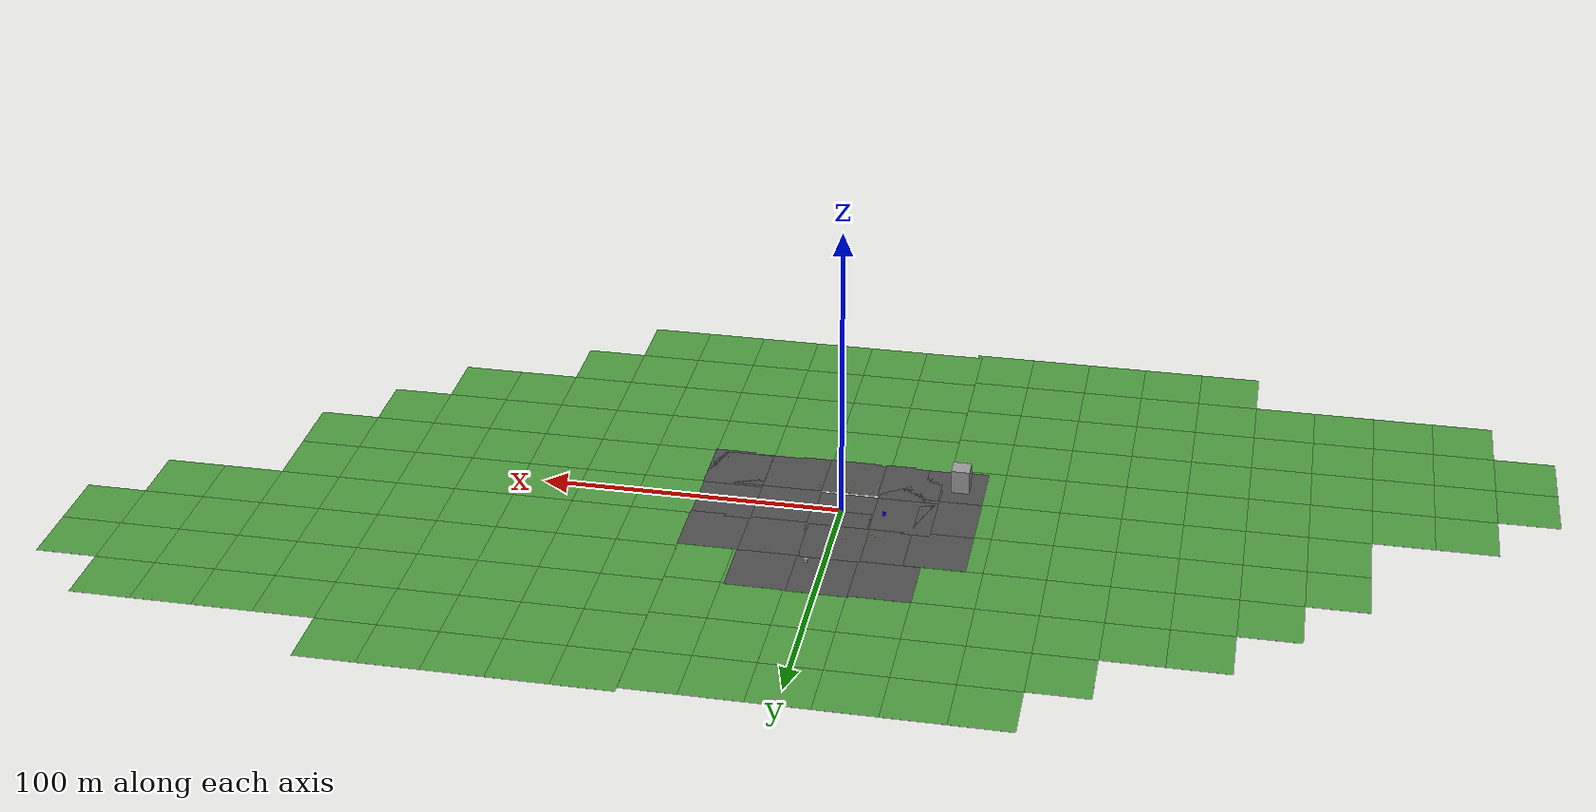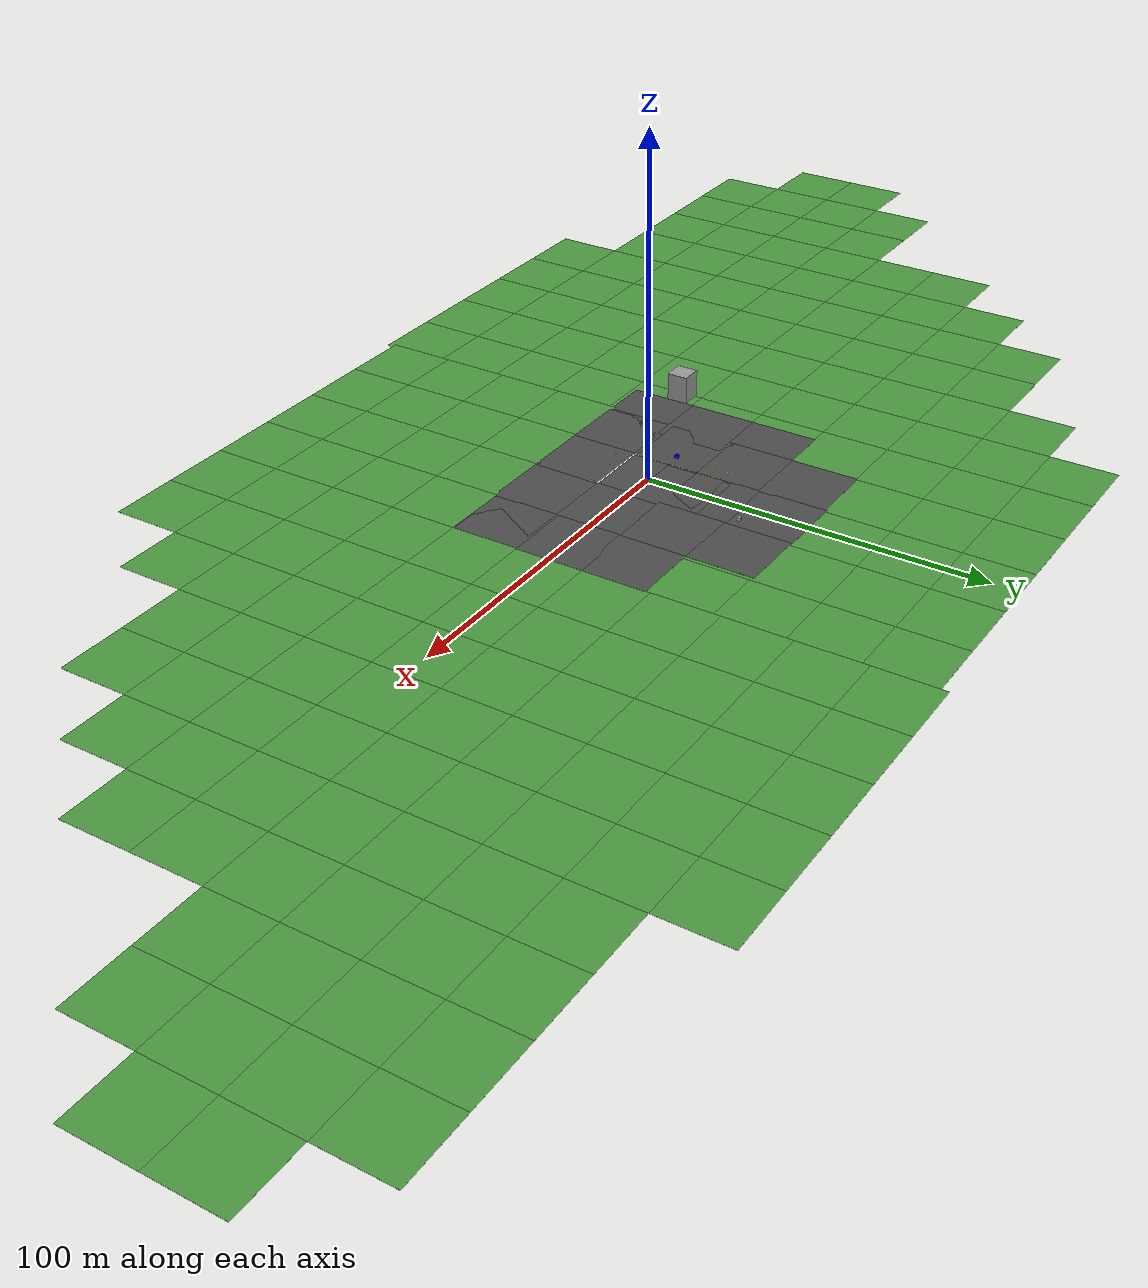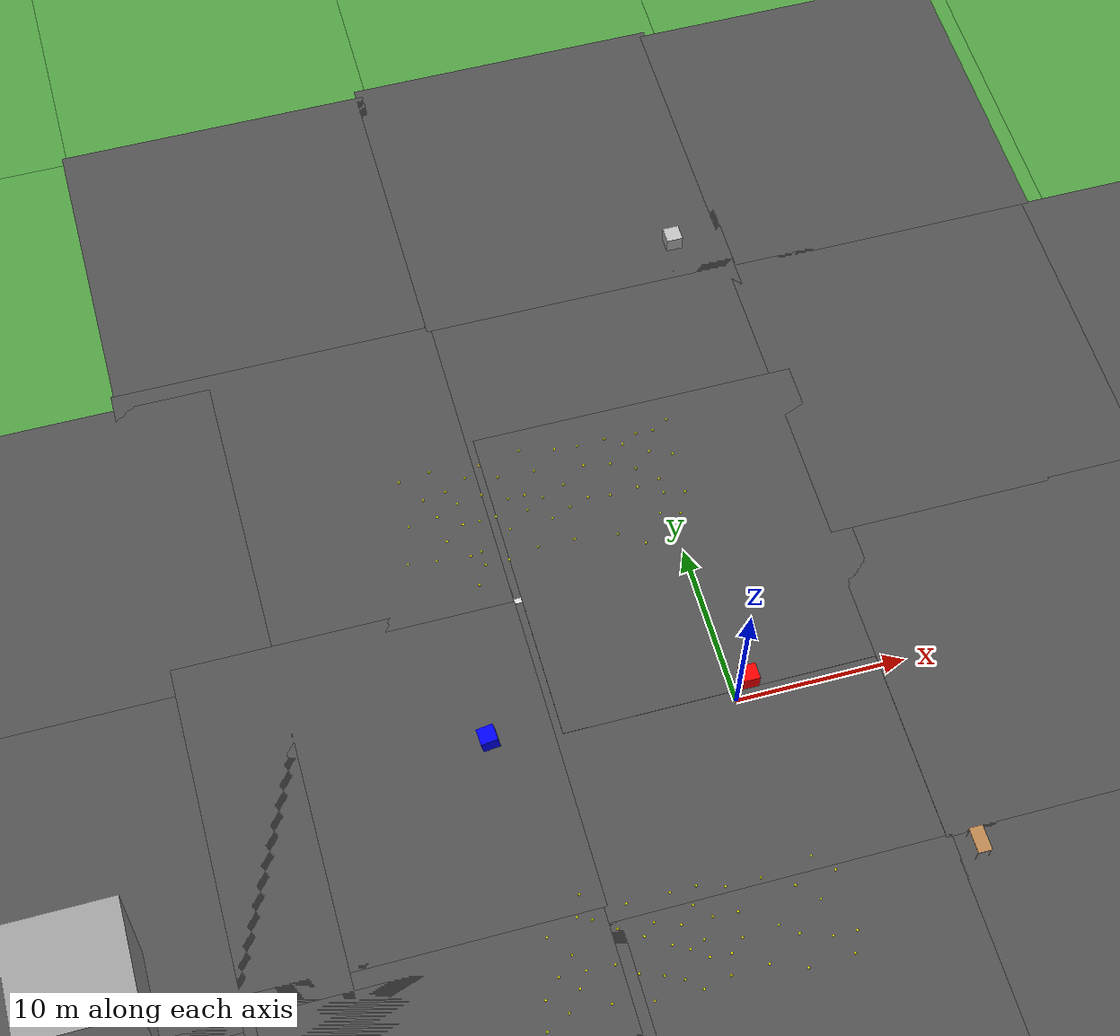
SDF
<sdf version="1.6">
 <world name="default">
  <light name="sun" type="directional">
   <pose>0 0 10 0 -0 0</pose>
   <diffuse>0.8 0.8 0.8 1</diffuse>
   <specular>0.2 0.2 0.2 1</specular>
   <attenuation>
    <range>1000</range>
    <constant>0.9</constant>
    <linear>0.01</linear>
    <quadratic>0.001</quadratic>
   </attenuation>
   <direction>-0.5 0.1 -0.9</direction>
  </light>
  <gravity>0 0 -9.8</gravity>
  <magnetic_field>6e-06 2.3e-05 -4.2e-05</magnetic_field>
  <atmosphere type="adiabatic"/>
  <physics name="default_physics" default="0" type="ode">
   <max_step_size>0.001</max_step_size>
   <real_time_factor>1</real_time_factor>
   <real_time_update_rate>1000</real_time_update_rate>
  </physics>
  <scene><ambient>0.4 0.4 0.4 1</ambient><background>0.7 0.7 0.7 1</background><shadows>1</shadows></scene>
  <spherical_coordinates>
   <surface_model>EARTH_WGS84</surface_model>
   <latitude_deg>0</latitude_deg>
   <longitude_deg>0</longitude_deg>
   <elevation>0</elevation>
   <heading_deg>0</heading_deg>
  </spherical_coordinates>
  <model name="labrob_ground">
   <static>1</static>
   <link name="link">
    <collision name="collision">
     <geometry><plane><normal>0 0 1</normal><size>20 20</size></plane></geometry>
     <surface><friction><ode><mu>100</mu><mu2>50</mu2></ode></friction></surface>
    </collision>
    <visual name="visual">
     <cast_shadows>0</cast_shadows>
     <geometry><plane><normal>0 0 1</normal><size>20 20</size></plane></geometry>
     <material>
      <script>
       <uri>model://labrob_ground/materials/scripts/</uri>
       <uri>model://labrob_ground/materials/textures/</uri>
       <name>Labrob/AsphaltGround</name>
      </script>
     </material>
    </visual>
   </link>
   <pose>-1.13682 -0.729135 0 0 -0 0</pose>
  </model>
  <model name="labrob_ground_0">
   <static>1</static>
   <link name="link">
    <collision name="collision">
     <geometry><plane><normal>0 0 1</normal><size>20 20</size></plane></geometry>
     <surface><friction><ode><mu>100</mu><mu2>50</mu2></ode></friction></surface>
    </collision>
    <visual name="visual">
     <cast_shadows>0</cast_shadows>
     <geometry><plane><normal>0 0 1</normal><size>20 20</size></plane></geometry>
     <material>
      <script>
       <uri>model://labrob_ground/materials/scripts/</uri>
       <uri>model://labrob_ground/materials/textures/</uri>
       <name>Labrob/AsphaltGround</name>
      </script>
     </material>
    </visual>
   </link>
   <pose>18.5231 -0.837953 0 0 -0 0</pose>
  </model>
  <model name="labrob_ground_1">
   <static>1</static>
   <link name="link">
    <collision name="collision">
     <geometry><plane><normal>0 0 1</normal><size>20 20</size></plane></geometry>
     <surface><friction><ode><mu>100</mu><mu2>50</mu2></ode></friction></surface>
    </collision>
    <visual name="visual">
     <cast_shadows>0</cast_shadows>
     <geometry><plane><normal>0 0 1</normal><size>20 20</size></plane></geometry>
     <material>
      <script>
       <uri>model://labrob_ground/materials/scripts/</uri>
       <uri>model://labrob_ground/materials/textures/</uri>
       <name>Labrob/AsphaltGround</name>
      </script>
     </material>
    </visual>
   </link>
   <pose>-1.15349 -20.7136 0 0 -0 0</pose>
  </model>
  <model name="labrob_ground_2">
   <static>1</static>
   <link name="link">
    <collision name="collision">
     <geometry><plane><normal>0 0 1</normal><size>20 20</size></plane></geometry>
     <surface><friction><ode><mu>100</mu><mu2>50</mu2></ode></friction></surface>
    </collision>
    <visual name="visual">
     <cast_shadows>0</cast_shadows>
     <geometry><plane><normal>0 0 1</normal><size>20 20</size></plane></geometry>
     <material>
      <script>
       <uri>model://labrob_ground/materials/scripts/</uri>
       <uri>model://labrob_ground/materials/textures/</uri>
       <name>Labrob/AsphaltGround</name>
      </script>
     </material>
    </visual>
   </link>
   <pose>18.777 -20.6695 0 0 -0 0</pose>
  </model>
  <model name="labrob_ground_3">
   <static>1</static>
   <link name="link">
    <collision name="collision">
     <geometry><plane><normal>0 0 1</normal><size>20 20</size></plane></geometry>
     <surface><friction><ode><mu>100</mu><mu2>50</mu2></ode></friction></surface>
    </collision>
    <visual name="visual">
     <cast_shadows>0</cast_shadows>
     <geometry><plane><normal>0 0 1</normal><size>20 20</size></plane></geometry>
     <material>
      <script>
       <uri>model://labrob_ground/materials/scripts/</uri>
       <uri>model://labrob_ground/materials/textures/</uri>
       <name>Labrob/AsphaltGround</name>
      </script>
     </material>
    </visual>
   </link>
   <pose>-20.4019 0.227461 0 0 -0 0</pose>
  </model>
  <model name="labrob_ground_4">
   <static>1</static>
   <link name="link">
    <collision name="collision">
     <geometry><plane><normal>0 0 1</normal><size>20 20</size></plane></geometry>
     <surface><friction><ode><mu>100</mu><mu2>50</mu2></ode></friction></surface>
    </collision>
    <visual name="visual">
     <cast_shadows>0</cast_shadows>
     <geometry><plane><normal>0 0 1</normal><size>20 20</size></plane></geometry>
     <material>
      <script>
       <uri>model://labrob_ground/materials/scripts/</uri>
       <uri>model://labrob_ground/materials/textures/</uri>
       <name>Labrob/AsphaltGround</name>
      </script>
     </material>
    </visual>
   </link>
   <pose>-20.6052 -19.5078 0 0 -0 0</pose>
  </model>
  <model name="labrob_ground_5">
   <static>1</static>
   <link name="link">
    <collision name="collision">
     <geometry><plane><normal>0 0 1</normal><size>20 20</size></plane></geometry>
     <surface><friction><ode><mu>100</mu><mu2>50</mu2></ode></friction></surface>
    </collision>
    <visual name="visual">
     <cast_shadows>0</cast_shadows>
     <geometry><plane><normal>0 0 1</normal><size>20 20</size></plane></geometry>
     <material>
      <script>
       <uri>model://labrob_ground/materials/scripts/</uri>
       <uri>model://labrob_ground/materials/textures/</uri>
       <name>Labrob/AsphaltGround</name>
      </script>
     </material>
    </visual>
   </link>
   <pose>-20.4308 19.4095 0 0 -0 0</pose>
  </model>
  <model name="labrob_ground_6">
   <static>1</static>
   <link name="link">
    <collision name="collision">
     <geometry><plane><normal>0 0 1</normal><size>20 20</size></plane></geometry>
     <surface><friction><ode><mu>100</mu><mu2>50</mu2></ode></friction></surface>
    </collision>
    <visual name="visual">
     <cast_shadows>0</cast_shadows>
     <geometry><plane><normal>0 0 1</normal><size>20 20</size></plane></geometry>
     <material>
      <script>
       <uri>model://labrob_ground/materials/scripts/</uri>
       <uri>model://labrob_ground/materials/textures/</uri>
       <name>Labrob/AsphaltGround</name>
      </script>
     </material>
    </visual>
   </link>
   <pose>-0.764551 19.5561 0 0 -0 0</pose>
  </model>
  <model name="labrob_ground_7">
   <static>1</static>
   <link name="link">
    <collision name="collision">
     <geometry><plane><normal>0 0 1</normal><size>20 20</size></plane></geometry>
     <surface><friction><ode><mu>100</mu><mu2>50</mu2></ode></friction></surface>
    </collision>
    <visual name="visual">
     <cast_shadows>0</cast_shadows>
     <geometry><plane><normal>0 0 1</normal><size>20 20</size></plane></geometry>
     <material>
      <script>
       <uri>model://labrob_ground/materials/scripts/</uri>
       <uri>model://labrob_ground/materials/textures/</uri>
       <name>Labrob/AsphaltGround</name>
      </script>
     </material>
    </visual>
   </link>
   <pose>18.7361 18.9694 0 0 -0 0</pose>
  </model>
  <model name="labrob_ground_8">
   <static>1</static>
   <link name="link">
    <collision name="collision">
     <geometry><plane><normal>0 0 1</normal><size>20 20</size></plane></geometry>
     <surface><friction><ode><mu>100</mu><mu2>50</mu2></ode></friction></surface>
    </collision>
    <visual name="visual">
     <cast_shadows>0</cast_shadows>
     <geometry><plane><normal>0 0 1</normal><size>20 20</size></plane></geometry>
     <material>
      <script>
       <uri>model://labrob_ground/materials/scripts/</uri>
       <uri>model://labrob_ground/materials/textures/</uri>
       <name>Labrob/AsphaltGround</name>
      </script>
     </material>
    </visual>
   </link>
   <pose>-20.2712 38.534 0 0 -0 0</pose>
  </model>
  <model name="labrob_ground_9">
   <static>1</static>
   <link name="link">
    <collision name="collision">
     <geometry><plane><normal>0 0 1</normal><size>20 20</size></plane></geometry>
     <surface><friction><ode><mu>100</mu><mu2>50</mu2></ode></friction></surface>
    </collision>
    <visual name="visual">
     <cast_shadows>0</cast_shadows>
     <geometry><plane><normal>0 0 1</normal><size>20 20</size></plane></geometry>
     <material>
      <script>
       <uri>model://labrob_ground/materials/scripts/</uri>
       <uri>model://labrob_ground/materials/textures/</uri>
       <name>Labrob/AsphaltGround</name>
      </script>
     </material>
    </visual>
   </link>
   <pose>-0.706199 39.0779 0 0 -0 0</pose>
  </model>
  <model name="labrob_ground_10">
   <static>1</static>
   <link name="link">
    <collision name="collision">
     <geometry><plane><normal>0 0 1</normal><size>20 20</size></plane></geometry>
     <surface><friction><ode><mu>100</mu><mu2>50</mu2></ode></friction></surface>
    </collision>
    <visual name="visual">
     <cast_shadows>0</cast_shadows>
     <geometry><plane><normal>0 0 1</normal><size>20 20</size></plane></geometry>
     <material>
      <script>
       <uri>model://labrob_ground/materials/scripts/</uri>
       <uri>model://labrob_ground/materials/textures/</uri>
       <name>Labrob/AsphaltGround</name>
      </script>
     </material>
    </visual>
   </link>
   <pose>18.9313 38.763 0 0 -0 0</pose>
  </model>
  <model name="labrob_ground_11">
   <static>1</static>
   <link name="link">
    <collision name="collision">
     <geometry><plane><normal>0 0 1</normal><size>20 20</size></plane></geometry>
     <surface><friction><ode><mu>100</mu><mu2>50</mu2></ode></friction></surface>
    </collision>
    <visual name="visual">
     <cast_shadows>0</cast_shadows>
     <geometry><plane><normal>0 0 1</normal><size>20 20</size></plane></geometry>
     <material>
      <script>
       <uri>model://labrob_ground/materials/scripts/</uri>
       <uri>model://labrob_ground/materials/textures/</uri>
       <name>Labrob/AsphaltGround</name>
      </script>
     </material>
    </visual>
   </link>
   <pose>38.4891 18.8271 0 0 -0 0</pose>
  </model>
  <model name="labrob_ground_12">
   <static>1</static>
   <link name="link">
    <collision name="collision">
     <geometry><plane><normal>0 0 1</normal><size>20 20</size></plane></geometry>
     <surface><friction><ode><mu>100</mu><mu2>50</mu2></ode></friction></surface>
    </collision>
    <visual name="visual">
     <cast_shadows>0</cast_shadows>
     <geometry><plane><normal>0 0 1</normal><size>20 20</size></plane></geometry>
     <material>
      <script>
       <uri>model://labrob_ground/materials/scripts/</uri>
       <uri>model://labrob_ground/materials/textures/</uri>
       <name>Labrob/AsphaltGround</name>
      </script>
     </material>
    </visual>
   </link>
   <pose>38.5118 0.043136 0 0 -0 0</pose>
  </model>
  <model name="labrob_ground_13">
   <static>1</static>
   <link name="link">
    <collision name="collision">
     <geometry><plane><normal>0 0 1</normal><size>20 20</size></plane></geometry>
     <surface><friction><ode><mu>100</mu><mu2>50</mu2></ode></friction></surface>
    </collision>
    <visual name="visual">
     <cast_shadows>0</cast_shadows>
     <geometry><plane><normal>0 0 1</normal><size>20 20</size></plane></geometry>
     <material>
      <script>
       <uri>model://labrob_ground/materials/scripts/</uri>
       <uri>model://labrob_ground/materials/textures/</uri>
       <name>Labrob/AsphaltGround</name>
      </script>
     </material>
    </visual>
   </link>
   <pose>38.4883 -19.6209 0 0 -0 0</pose>
  </model>
  <model name="labrob_ground_14">
   <static>1</static>
   <link name="link">
    <collision name="collision">
     <geometry><plane><normal>0 0 1</normal><size>20 20</size></plane></geometry>
     <surface><friction><ode><mu>100</mu><mu2>50</mu2></ode></friction></surface>
    </collision>
    <visual name="visual">
     <cast_shadows>0</cast_shadows>
     <geometry><plane><normal>0 0 1</normal><size>20 20</size></plane></geometry>
     <material>
      <script>
       <uri>model://labrob_ground/materials/scripts/</uri>
       <uri>model://labrob_ground/materials/textures/</uri>
       <name>Labrob/AsphaltGround</name>
      </script>
     </material>
    </visual>
   </link>
   <pose>-19.9414 -20.7737 0 0 -0 0</pose>
  </model>
  <model name="labrob_ground_15">
   <static>1</static>
   <link name="link">
    <collision name="collision">
     <geometry><plane><normal>0 0 1</normal><size>20 20</size></plane></geometry>
     <surface><friction><ode><mu>100</mu><mu2>50</mu2></ode></friction></surface>
    </collision>
    <visual name="visual">
     <cast_shadows>0</cast_shadows>
     <geometry><plane><normal>0 0 1</normal><size>20 20</size></plane></geometry>
     <material>
      <script>
       <uri>model://labrob_ground/materials/scripts/</uri>
       <uri>model://labrob_ground/materials/textures/</uri>
       <name>Labrob/AsphaltGround</name>
      </script>
     </material>
    </visual>
   </link>
   <pose>-34.5431 -20.6915 0 0 -0 0</pose>
  </model>
  <model name="labrob_ground_16">
   <static>1</static>
   <link name="link">
    <collision name="collision">
     <geometry><plane><normal>0 0 1</normal><size>20 20</size></plane></geometry>
     <surface><friction><ode><mu>100</mu><mu2>50</mu2></ode></friction></surface>
    </collision>
    <visual name="visual">
     <cast_shadows>0</cast_shadows>
     <geometry><plane><normal>0 0 1</normal><size>20 20</size></plane></geometry>
     <material>
      <script>
       <uri>model://labrob_ground/materials/scripts/</uri>
       <uri>model://labrob_ground/materials/textures/</uri>
       <name>Labrob/AsphaltGround</name>
      </script>
     </material>
    </visual>
   </link>
   <pose>-34.5552 -1.44397 0 0 -0 0</pose>
  </model>
  <model name="labrob_ground_17">
   <static>1</static>
   <link name="link">
    <collision name="collision">
     <geometry><plane><normal>0 0 1</normal><size>20 20</size></plane></geometry>
     <surface><friction><ode><mu>100</mu><mu2>50</mu2></ode></friction></surface>
    </collision>
    <visual name="visual">
     <cast_shadows>0</cast_shadows>
     <geometry><plane><normal>0 0 1</normal><size>20 20</size></plane></geometry>
     <material>
      <script>
       <uri>model://labrob_ground/materials/scripts/</uri>
       <uri>model://labrob_ground/materials/textures/</uri>
       <name>Labrob/AsphaltGround</name>
      </script>
     </material>
    </visual>
   </link>
   <pose>-34.5316 18.4059 0 0 -0 0</pose>
  </model>
  <model name="labrob_ground_18">
   <static>1</static>
   <link name="link">
    <collision name="collision">
     <geometry><plane><normal>0 0 1</normal><size>20 20</size></plane></geometry>
     <surface><friction><ode><mu>100</mu><mu2>50</mu2></ode></friction></surface>
    </collision>
    <visual name="visual">
     <cast_shadows>0</cast_shadows>
     <geometry><plane><normal>0 0 1</normal><size>20 20</size></plane></geometry>
     <material>
      <script>
       <uri>model://labrob_ground/materials/scripts/</uri>
       <uri>model://labrob_ground/materials/textures/</uri>
       <name>Labrob/AsphaltGround</name>
      </script>
     </material>
    </visual>
   </link>
   <pose>38.422 -20.7287 0 0 -0 0</pose>
  </model>
  <model name="grass_plane">
   <static>1</static>
   <link name="link">
    <collision name="collision">
     <geometry><plane><normal>0 0 1</normal><size>500 500</size></plane></geometry>
     <surface><friction><ode><mu>0.5</mu><mu2>0.5</mu2></ode></friction></surface>
    </collision>
    <visual name="visual_0">
     <pose>-40 -40 0 0 -0 0</pose>
     <cast_shadows>0</cast_shadows>
     <geometry><plane><normal>0 0 1</normal><size>20 20</size></plane></geometry>
     <material>
      <script>
       <uri>model://grass_plane/materials/scripts</uri>
       <uri>model://grass_plane/materials/textures</uri>
       <name>vrc/grass</name>
      </script>
     </material>
    </visual>
    <visual name="visual_1">
     <pose>-20 -40 0 0 -0 0</pose>
     <cast_shadows>0</cast_shadows>
     <geometry><plane><normal>0 0 1</normal><size>20 20</size></plane></geometry>
     <material>
      <script>
       <uri>model://grass_plane/materials/scripts</uri>
       <uri>model://grass_plane/materials/textures</uri>
       <name>vrc/grass</name>
      </script>
     </material>
    </visual>
    <visual name="visual_2">
     <pose>0 -40 0 0 -0 0</pose>
     <cast_shadows>0</cast_shadows>
     <geometry><plane><normal>0 0 1</normal><size>20 20</size></plane></geometry>
     <material>
      <script>
       <uri>model://grass_plane/materials/scripts</uri>
       <uri>model://grass_plane/materials/textures</uri>
       <name>vrc/grass</name>
      </script>
     </material>
    </visual>
    <visual name="visual_3">
     <pose>20 -40 0 0 -0 0</pose>
     <cast_shadows>0</cast_shadows>
     <geometry><plane><normal>0 0 1</normal><size>20 20</size></plane></geometry>
     <material>
      <script>
       <uri>model://grass_plane/materials/scripts</uri>
       <uri>model://grass_plane/materials/textures</uri>
       <name>vrc/grass</name>
      </script>
     </material>
    </visual>
    <visual name="visual_4">
     <pose>40 -40 0 0 -0 0</pose>
     <cast_shadows>0</cast_shadows>
     <geometry><plane><normal>0 0 1</normal><size>20 20</size></plane></geometry>
     <material>
      <script>
       <uri>model://grass_plane/materials/scripts</uri>
       <uri>model://grass_plane/materials/textures</uri>
       <name>vrc/grass</name>
      </script>
     </material>
    </visual>
    <visual name="visual_5">
     <pose>60 -40 0 0 -0 0</pose>
     <cast_shadows>0</cast_shadows>
     <geometry><plane><normal>0 0 1</normal><size>20 20</size></plane></geometry>
     <material>
      <script>
       <uri>model://grass_plane/materials/scripts</uri>
       <uri>model://grass_plane/materials/textures</uri>
       <name>vrc/grass</name>
      </script>
     </material>
    </visual>
    <visual name="visual_6">
     <pose>-40 -20 0 0 -0 0</pose>
     <cast_shadows>0</cast_shadows>
     <geometry><plane><normal>0 0 1</normal><size>20 20</size></plane></geometry>
     <material>
      <script>
       <uri>model://grass_plane/materials/scripts</uri>
       <uri>model://grass_plane/materials/textures</uri>
       <name>vrc/grass</name>
      </script>
     </material>
    </visual>
    <visual name="visual_7">
     <pose>-20 -20 0 0 -0 0</pose>
     <cast_shadows>0</cast_shadows>
     <geometry><plane><normal>0 0 1</normal><size>20 20</size></plane></geometry>
     <material>
      <script>
       <uri>model://grass_plane/materials/scripts</uri>
       <uri>model://grass_plane/materials/textures</uri>
       <name>vrc/grass</name>
      </script>
     </material>
    </visual>
    <visual name="visual_8">
     <pose>0 -20 0 0 -0 0</pose>
     <cast_shadows>0</cast_shadows>
     <geometry><plane><normal>0 0 1</normal><size>20 20</size></plane></geometry>
     <material>
      <script>
       <uri>model://grass_plane/materials/scripts</uri>
       <uri>model://grass_plane/materials/textures</uri>
       <name>vrc/grass</name>
      </script>
     </material>
    </visual>
    <visual name="visual_9">
     <pose>20 -20 0 0 -0 0</pose>
     <cast_shadows>0</cast_shadows>
     <geometry><plane><normal>0 0 1</normal><size>20 20</size></plane></geometry>
     <material>
      <script>
       <uri>model://grass_plane/materials/scripts</uri>
       <uri>model://grass_plane/materials/textures</uri>
       <name>vrc/grass</name>
      </script>
     </material>
    </visual>
    <visual name="visual_10">
     <pose>40 -20 0 0 -0 0</pose>
     <cast_shadows>0</cast_shadows>
     <geometry><plane><normal>0 0 1</normal><size>20 20</size></plane></geometry>
     <material>
      <script>
       <uri>model://grass_plane/materials/scripts</uri>
       <uri>model://grass_plane/materials/textures</uri>
       <name>vrc/grass</name>
      </script>
     </material>
    </visual>
    <visual name="visual_11">
     <pose>60 -20 0 0 -0 0</pose>
     <cast_shadows>0</cast_shadows>
     <geometry><plane><normal>0 0 1</normal><size>20 20</size></plane></geometry>
     <material>
      <script>
       <uri>model://grass_plane/materials/scripts</uri>
       <uri>model://grass_plane/materials/textures</uri>
       <name>vrc/grass</name>
      </script>
     </material>
    </visual>
    <visual name="visual_12">
     <pose>80 -20 0 0 -0 0</pose>
     <cast_shadows>0</cast_shadows>
     <geometry><plane><normal>0 0 1</normal><size>20 20</size></plane></geometry>
     <material>
      <script>
       <uri>model://grass_plane/materials/scripts</uri>
       <uri>model://grass_plane/materials/textures</uri>
       <name>vrc/grass</name>
      </script>
     </material>
    </visual>
    <visual name="visual_13">
     <pose>-40 0 0 0 -0 0</pose>
     <cast_shadows>0</cast_shadows>
     <geometry><plane><normal>0 0 1</normal><size>20 20</size></plane></geometry>
     <material>
      <script>
       <uri>model://grass_plane/materials/scripts</uri>
       <uri>model://grass_plane/materials/textures</uri>
       <name>vrc/grass</name>
      </script>
     </material>
    </visual>
    <visual name="visual_14">
     <pose>-20 0 0 0 -0 0</pose>
     <cast_shadows>0</cast_shadows>
     <geometry><plane><normal>0 0 1</normal><size>20 20</size></plane></geometry>
     <material>
      <script>
       <uri>model://grass_plane/materials/scripts</uri>
       <uri>model://grass_plane/materials/textures</uri>
       <name>vrc/grass</name>
      </script>
     </material>
    </visual>
    <visual name="visual_15">
     <cast_shadows>0</cast_shadows>
     <geometry><plane><normal>0 0 1</normal><size>20 20</size></plane></geometry>
     <material>
      <script>
       <uri>model://grass_plane/materials/scripts</uri>
       <uri>model://grass_plane/materials/textures</uri>
       <name>vrc/grass</name>
      </script>
     </material>
    </visual>
    <visual name="visual_16">
     <pose>20 0 0 0 -0 0</pose>
     <cast_shadows>0</cast_shadows>
     <geometry><plane><normal>0 0 1</normal><size>20 20</size></plane></geometry>
     <material>
      <script>
       <uri>model://grass_plane/materials/scripts</uri>
       <uri>model://grass_plane/materials/textures</uri>
       <name>vrc/grass</name>
      </script>
     </material>
    </visual>
    <visual name="visual_17">
     <pose>40 0 0 0 -0 0</pose>
     <cast_shadows>0</cast_shadows>
     <geometry><plane><normal>0 0 1</normal><size>20 20</size></plane></geometry>
     <material>
      <script>
       <uri>model://grass_plane/materials/scripts</uri>
       <uri>model://grass_plane/materials/textures</uri>
       <name>vrc/grass</name>
      </script>
     </material>
    </visual>
    <visual name="visual_18">
     <pose>60 0 0 0 -0 0</pose>
     <cast_shadows>0</cast_shadows>
     <geometry><plane><normal>0 0 1</normal><size>20 20</size></plane></geometry>
     <material>
      <script>
       <uri>model://grass_plane/materials/scripts</uri>
       <uri>model://grass_plane/materials/textures</uri>
       <name>vrc/grass</name>
      </script>
     </material>
    </visual>
    <visual name="visual_19">
     <pose>80 0 0 0 -0 0</pose>
     <cast_shadows>0</cast_shadows>
     <geometry><plane><normal>0 0 1</normal><size>20 20</size></plane></geometry>
     <material>
      <script>
       <uri>model://grass_plane/materials/scripts</uri>
       <uri>model://grass_plane/materials/textures</uri>
       <name>vrc/grass</name>
      </script>
     </material>
    </visual>
    <visual name="visual_20">
     <pose>100 0 0 0 -0 0</pose>
     <cast_shadows>0</cast_shadows>
     <geometry><plane><normal>0 0 1</normal><size>20 20</size></plane></geometry>
     <material>
      <script>
       <uri>model://grass_plane/materials/scripts</uri>
       <uri>model://grass_plane/materials/textures</uri>
       <name>vrc/grass</name>
      </script>
     </material>
    </visual>
    <visual name="visual_21">
     <pose>120 0 0 0 -0 0</pose>
     <cast_shadows>0</cast_shadows>
     <geometry><plane><normal>0 0 1</normal><size>20 20</size></plane></geometry>
     <material>
      <script>
       <uri>model://grass_plane/materials/scripts</uri>
       <uri>model://grass_plane/materials/textures</uri>
       <name>vrc/grass</name>
      </script>
     </material>
    </visual>
    <visual name="visual_22">
     <pose>-40 20 0 0 -0 0</pose>
     <cast_shadows>0</cast_shadows>
     <geometry><plane><normal>0 0 1</normal><size>20 20</size></plane></geometry>
     <material>
      <script>
       <uri>model://grass_plane/materials/scripts</uri>
       <uri>model://grass_plane/materials/textures</uri>
       <name>vrc/grass</name>
      </script>
     </material>
    </visual>
    <visual name="visual_23">
     <pose>-20 20 0 0 -0 0</pose>
     <cast_shadows>0</cast_shadows>
     <geometry><plane><normal>0 0 1</normal><size>20 20</size></plane></geometry>
     <material>
      <script>
       <uri>model://grass_plane/materials/scripts</uri>
       <uri>model://grass_plane/materials/textures</uri>
       <name>vrc/grass</name>
      </script>
     </material>
    </visual>
    <visual name="visual_24">
     <pose>0 20 0 0 -0 0</pose>
     <cast_shadows>0</cast_shadows>
     <geometry><plane><normal>0 0 1</normal><size>20 20</size></plane></geometry>
     <material>
      <script>
       <uri>model://grass_plane/materials/scripts</uri>
       <uri>model://grass_plane/materials/textures</uri>
       <name>vrc/grass</name>
      </script>
     </material>
    </visual>
    <visual name="visual_25">
     <pose>20 20 0 0 -0 0</pose>
     <cast_shadows>0</cast_shadows>
     <geometry><plane><normal>0 0 1</normal><size>20 20</size></plane></geometry>
     <material>
      <script>
       <uri>model://grass_plane/materials/scripts</uri>
       <uri>model://grass_plane/materials/textures</uri>
       <name>vrc/grass</name>
      </script>
     </material>
    </visual>
    <visual name="visual_26">
     <pose>40 20 0 0 -0 0</pose>
     <cast_shadows>0</cast_shadows>
     <geometry><plane><normal>0 0 1</normal><size>20 20</size></plane></geometry>
     <material>
      <script>
       <uri>model://grass_plane/materials/scripts</uri>
       <uri>model://grass_plane/materials/textures</uri>
       <name>vrc/grass</name>
      </script>
     </material>
    </visual>
    <visual name="visual_27">
     <pose>60 20 0 0 -0 0</pose>
     <cast_shadows>0</cast_shadows>
     <geometry><plane><normal>0 0 1</normal><size>20 20</size></plane></geometry>
     <material>
      <script>
       <uri>model://grass_plane/materials/scripts</uri>
       <uri>model://grass_plane/materials/textures</uri>
       <name>vrc/grass</name>
      </script>
     </material>
    </visual>
    <visual name="visual_28">
     <pose>80 20 0 0 -0 0</pose>
     <cast_shadows>0</cast_shadows>
     <geometry><plane><normal>0 0 1</normal><size>20 20</size></plane></geometry>
     <material>
      <script>
       <uri>model://grass_plane/materials/scripts</uri>
       <uri>model://grass_plane/materials/textures</uri>
       <name>vrc/grass</name>
      </script>
     </material>
    </visual>
    <visual name="visual_29">
     <pose>100 20 0 0 -0 0</pose>
     <cast_shadows>0</cast_shadows>
     <geometry><plane><normal>0 0 1</normal><size>20 20</size></plane></geometry>
     <material>
      <script>
       <uri>model://grass_plane/materials/scripts</uri>
       <uri>model://grass_plane/materials/textures</uri>
       <name>vrc/grass</name>
      </script>
     </material>
    </visual>
    <visual name="visual_30">
     <pose>120 20 0 0 -0 0</pose>
     <cast_shadows>0</cast_shadows>
     <geometry><plane><normal>0 0 1</normal><size>20 20</size></plane></geometry>
     <material>
      <script>
       <uri>model://grass_plane/materials/scripts</uri>
       <uri>model://grass_plane/materials/textures</uri>
       <name>vrc/grass</name>
      </script>
     </material>
    </visual>
    <visual name="visual_31">
     <pose>140 20 0 0 -0 0</pose>
     <cast_shadows>0</cast_shadows>
     <geometry><plane><normal>0 0 1</normal><size>20 20</size></plane></geometry>
     <material>
      <script>
       <uri>model://grass_plane/materials/scripts</uri>
       <uri>model://grass_plane/materials/textures</uri>
       <name>vrc/grass</name>
      </script>
     </material>
    </visual>
    <visual name="visual_32">
     <pose>40 40 0 0 -0 0</pose>
     <cast_shadows>0</cast_shadows>
     <geometry><plane><normal>0 0 1</normal><size>20 20</size></plane></geometry>
     <material>
      <script>
       <uri>model://grass_plane/materials/scripts</uri>
       <uri>model://grass_plane/materials/textures</uri>
       <name>vrc/grass</name>
      </script>
     </material>
    </visual>
    <visual name="visual_33">
     <pose>60 40 0 0 -0 0</pose>
     <cast_shadows>0</cast_shadows>
     <geometry><plane><normal>0 0 1</normal><size>20 20</size></plane></geometry>
     <material>
      <script>
       <uri>model://grass_plane/materials/scripts</uri>
       <uri>model://grass_plane/materials/textures</uri>
       <name>vrc/grass</name>
      </script>
     </material>
    </visual>
    <visual name="visual_34">
     <pose>80 40 0 0 -0 0</pose>
     <cast_shadows>0</cast_shadows>
     <geometry><plane><normal>0 0 1</normal><size>20 20</size></plane></geometry>
     <material>
      <script>
       <uri>model://grass_plane/materials/scripts</uri>
       <uri>model://grass_plane/materials/textures</uri>
       <name>vrc/grass</name>
      </script>
     </material>
    </visual>
    <visual name="visual_35">
     <pose>100 40 0 0 -0 0</pose>
     <cast_shadows>0</cast_shadows>
     <geometry><plane><normal>0 0 1</normal><size>20 20</size></plane></geometry>
     <material>
      <script>
       <uri>model://grass_plane/materials/scripts</uri>
       <uri>model://grass_plane/materials/textures</uri>
       <name>vrc/grass</name>
      </script>
     </material>
    </visual>
    <visual name="visual_36">
     <pose>120 40 0 0 -0 0</pose>
     <cast_shadows>0</cast_shadows>
     <geometry><plane><normal>0 0 1</normal><size>20 20</size></plane></geometry>
     <material>
      <script>
       <uri>model://grass_plane/materials/scripts</uri>
       <uri>model://grass_plane/materials/textures</uri>
       <name>vrc/grass</name>
      </script>
     </material>
    </visual>
    <visual name="visual_37">
     <pose>140 40 0 0 -0 0</pose>
     <cast_shadows>0</cast_shadows>
     <geometry><plane><normal>0 0 1</normal><size>20 20</size></plane></geometry>
     <material>
      <script>
       <uri>model://grass_plane/materials/scripts</uri>
       <uri>model://grass_plane/materials/textures</uri>
       <name>vrc/grass</name>
      </script>
     </material>
    </visual>
    <visual name="visual_38">
     <pose>160 40 0 0 -0 0</pose>
     <cast_shadows>0</cast_shadows>
     <geometry><plane><normal>0 0 1</normal><size>20 20</size></plane></geometry>
     <material>
      <script>
       <uri>model://grass_plane/materials/scripts</uri>
       <uri>model://grass_plane/materials/textures</uri>
       <name>vrc/grass</name>
      </script>
     </material>
    </visual>
    <visual name="visual_39">
     <pose>40 60 0 0 -0 0</pose>
     <cast_shadows>0</cast_shadows>
     <geometry><plane><normal>0 0 1</normal><size>20 20</size></plane></geometry>
     <material>
      <script>
       <uri>model://grass_plane/materials/scripts</uri>
       <uri>model://grass_plane/materials/textures</uri>
       <name>vrc/grass</name>
      </script>
     </material>
    </visual>
    <visual name="visual_40">
     <pose>60 60 0 0 -0 0</pose>
     <cast_shadows>0</cast_shadows>
     <geometry><plane><normal>0 0 1</normal><size>20 20</size></plane></geometry>
     <material>
      <script>
       <uri>model://grass_plane/materials/scripts</uri>
       <uri>model://grass_plane/materials/textures</uri>
       <name>vrc/grass</name>
      </script>
     </material>
    </visual>
    <visual name="visual_41">
     <pose>80 60 0 0 -0 0</pose>
     <cast_shadows>0</cast_shadows>
     <geometry><plane><normal>0 0 1</normal><size>20 20</size></plane></geometry>
     <material>
      <script>
       <uri>model://grass_plane/materials/scripts</uri>
       <uri>model://grass_plane/materials/textures</uri>
       <name>vrc/grass</name>
      </script>
     </material>
    </visual>
    <visual name="visual_42">
     <pose>100 60 0 0 -0 0</pose>
     <cast_shadows>0</cast_shadows>
     <geometry><plane><normal>0 0 1</normal><size>20 20</size></plane></geometry>
     <material>
      <script>
       <uri>model://grass_plane/materials/scripts</uri>
       <uri>model://grass_plane/materials/textures</uri>
       <name>vrc/grass</name>
      </script>
     </material>
    </visual>
    <visual name="visual_43">
     <pose>120 60 0 0 -0 0</pose>
     <cast_shadows>0</cast_shadows>
     <geometry><plane><normal>0 0 1</normal><size>20 20</size></plane></geometry>
     <material>
      <script>
       <uri>model://grass_plane/materials/scripts</uri>
       <uri>model://grass_plane/materials/textures</uri>
       <name>vrc/grass</name>
      </script>
     </material>
    </visual>
    <visual name="visual_44">
     <pose>140 60 0 0 -0 0</pose>
     <cast_shadows>0</cast_shadows>
     <geometry><plane><normal>0 0 1</normal><size>20 20</size></plane></geometry>
     <material>
      <script>
       <uri>model://grass_plane/materials/scripts</uri>
       <uri>model://grass_plane/materials/textures</uri>
       <name>vrc/grass</name>
      </script>
     </material>
    </visual>
    <visual name="visual_45">
     <pose>160 60 0 0 -0 0</pose>
     <cast_shadows>0</cast_shadows>
     <geometry><plane><normal>0 0 1</normal><size>20 20</size></plane></geometry>
     <material>
      <script>
       <uri>model://grass_plane/materials/scripts</uri>
       <uri>model://grass_plane/materials/textures</uri>
       <name>vrc/grass</name>
      </script>
     </material>
    </visual>
    <visual name="visual_46">
     <pose>40 80 0 0 -0 0</pose>
     <cast_shadows>0</cast_shadows>
     <geometry><plane><normal>0 0 1</normal><size>20 20</size></plane></geometry>
     <material>
      <script>
       <uri>model://grass_plane/materials/scripts</uri>
       <uri>model://grass_plane/materials/textures</uri>
       <name>vrc/grass</name>
      </script>
     </material>
    </visual>
    <visual name="visual_47">
     <pose>60 80 0 0 -0 0</pose>
     <cast_shadows>0</cast_shadows>
     <geometry><plane><normal>0 0 1</normal><size>20 20</size></plane></geometry>
     <material>
      <script>
       <uri>model://grass_plane/materials/scripts</uri>
       <uri>model://grass_plane/materials/textures</uri>
       <name>vrc/grass</name>
      </script>
     </material>
    </visual>
    <visual name="visual_48">
     <pose>80 80 0 0 -0 0</pose>
     <cast_shadows>0</cast_shadows>
     <geometry><plane><normal>0 0 1</normal><size>20 20</size></plane></geometry>
     <material>
      <script>
       <uri>model://grass_plane/materials/scripts</uri>
       <uri>model://grass_plane/materials/textures</uri>
       <name>vrc/grass</name>
      </script>
     </material>
    </visual>
    <visual name="visual_49">
     <pose>100 80 0 0 -0 0</pose>
     <cast_shadows>0</cast_shadows>
     <geometry><plane><normal>0 0 1</normal><size>20 20</size></plane></geometry>
     <material>
      <script>
       <uri>model://grass_plane/materials/scripts</uri>
       <uri>model://grass_plane/materials/textures</uri>
       <name>vrc/grass</name>
      </script>
     </material>
    </visual>
    <visual name="visual_50">
     <pose>120 80 0 0 -0 0</pose>
     <cast_shadows>0</cast_shadows>
     <geometry><plane><normal>0 0 1</normal><size>20 20</size></plane></geometry>
     <material>
      <script>
       <uri>model://grass_plane/materials/scripts</uri>
       <uri>model://grass_plane/materials/textures</uri>
       <name>vrc/grass</name>
      </script>
     </material>
    </visual>
    <visual name="visual_51">
     <pose>140 80 0 0 -0 0</pose>
     <cast_shadows>0</cast_shadows>
     <geometry><plane><normal>0 0 1</normal><size>20 20</size></plane></geometry>
     <material>
      <script>
       <uri>model://grass_plane/materials/scripts</uri>
       <uri>model://grass_plane/materials/textures</uri>
       <name>vrc/grass</name>
      </script>
     </material>
    </visual>
    <visual name="visual_52">
     <pose>160 80 0 0 -0 0</pose>
     <cast_shadows>0</cast_shadows>
     <geometry><plane><normal>0 0 1</normal><size>20 20</size></plane></geometry>
     <material>
      <script>
       <uri>model://grass_plane/materials/scripts</uri>
       <uri>model://grass_plane/materials/textures</uri>
       <name>vrc/grass</name>
      </script>
     </material>
    </visual>
    <visual name="visual_53">
     <pose>180 80 0 0 -0 0</pose>
     <cast_shadows>0</cast_shadows>
     <geometry><plane><normal>0 0 1</normal><size>20 20</size></plane></geometry>
     <material>
      <script>
       <uri>model://grass_plane/materials/scripts</uri>
       <uri>model://grass_plane/materials/textures</uri>
       <name>vrc/grass</name>
      </script>
     </material>
    </visual>
    <visual name="visual_54">
     <pose>200 80 0 0 -0 0</pose>
     <cast_shadows>0</cast_shadows>
     <geometry><plane><normal>0 0 1</normal><size>20 20</size></plane></geometry>
     <material>
      <script>
       <uri>model://grass_plane/materials/scripts</uri>
       <uri>model://grass_plane/materials/textures</uri>
       <name>vrc/grass</name>
      </script>
     </material>
    </visual>
    <visual name="visual_55">
     <pose>40 100 0 0 -0 0</pose>
     <cast_shadows>0</cast_shadows>
     <geometry><plane><normal>0 0 1</normal><size>20 20</size></plane></geometry>
     <material>
      <script>
       <uri>model://grass_plane/materials/scripts</uri>
       <uri>model://grass_plane/materials/textures</uri>
       <name>vrc/grass</name>
      </script>
     </material>
    </visual>
    <visual name="visual_56">
     <pose>60 100 0 0 -0 0</pose>
     <cast_shadows>0</cast_shadows>
     <geometry><plane><normal>0 0 1</normal><size>20 20</size></plane></geometry>
     <material>
      <script>
       <uri>model://grass_plane/materials/scripts</uri>
       <uri>model://grass_plane/materials/textures</uri>
       <name>vrc/grass</name>
      </script>
     </material>
    </visual>
    <visual name="visual_57">
     <pose>80 100 0 0 -0 0</pose>
     <cast_shadows>0</cast_shadows>
     <geometry><plane><normal>0 0 1</normal><size>20 20</size></plane></geometry>
     <material>
      <script>
       <uri>model://grass_plane/materials/scripts</uri>
       <uri>model://grass_plane/materials/textures</uri>
       <name>vrc/grass</name>
      </script>
     </material>
    </visual>
    <visual name="visual_58">
     <pose>100 100 0 0 -0 0</pose>
     <cast_shadows>0</cast_shadows>
     <geometry><plane><normal>0 0 1</normal><size>20 20</size></plane></geometry>
     <material>
      <script>
       <uri>model://grass_plane/materials/scripts</uri>
       <uri>model://grass_plane/materials/textures</uri>
       <name>vrc/grass</name>
      </script>
     </material>
    </visual>
    <visual name="visual_59">
     <pose>120 100 0 0 -0 0</pose>
     <cast_shadows>0</cast_shadows>
     <geometry><plane><normal>0 0 1</normal><size>20 20</size></plane></geometry>
     <material>
      <script>
       <uri>model://grass_plane/materials/scripts</uri>
       <uri>model://grass_plane/materials/textures</uri>
       <name>vrc/grass</name>
      </script>
     </material>
    </visual>
    <visual name="visual_60">
     <pose>140 100 0 0 -0 0</pose>
     <cast_shadows>0</cast_shadows>
     <geometry><plane><normal>0 0 1</normal><size>20 20</size></plane></geometry>
     <material>
      <script>
       <uri>model://grass_plane/materials/scripts</uri>
       <uri>model://grass_plane/materials/textures</uri>
       <name>vrc/grass</name>
      </script>
     </material>
    </visual>
    <visual name="visual_61">
     <pose>160 100 0 0 -0 0</pose>
     <cast_shadows>0</cast_shadows>
     <geometry><plane><normal>0 0 1</normal><size>20 20</size></plane></geometry>
     <material>
      <script>
       <uri>model://grass_plane/materials/scripts</uri>
       <uri>model://grass_plane/materials/textures</uri>
       <name>vrc/grass</name>
      </script>
     </material>
    </visual>
    <visual name="visual_62">
     <pose>180 100 0 0 -0 0</pose>
     <cast_shadows>0</cast_shadows>
     <geometry><plane><normal>0 0 1</normal><size>20 20</size></plane></geometry>
     <material>
      <script>
       <uri>model://grass_plane/materials/scripts</uri>
       <uri>model://grass_plane/materials/textures</uri>
       <name>vrc/grass</name>
      </script>
     </material>
    </visual>
    <visual name="visual_63">
     <pose>200 100 0 0 -0 0</pose>
     <cast_shadows>0</cast_shadows>
     <geometry><plane><normal>0 0 1</normal><size>20 20</size></plane></geometry>
     <material>
      <script>
       <uri>model://grass_plane/materials/scripts</uri>
       <uri>model://grass_plane/materials/textures</uri>
       <name>vrc/grass</name>
      </script>
     </material>
    </visual>
    <visual name="visual_63a">
     <pose>220 100 0 0 -0 0</pose>
     <cast_shadows>0</cast_shadows>
     <geometry><plane><normal>0 0 1</normal><size>20 20</size></plane></geometry>
     <material>
      <script>
       <uri>model://grass_plane/materials/scripts</uri>
       <uri>model://grass_plane/materials/textures</uri>
       <name>vrc/grass</name>
      </script>
     </material>
    </visual>
    <visual name="visual_64">
     <pose>40 120 0 0 -0 0</pose>
     <cast_shadows>0</cast_shadows>
     <geometry><plane><normal>0 0 1</normal><size>20 20</size></plane></geometry>
     <material>
      <script>
       <uri>model://grass_plane/materials/scripts</uri>
       <uri>model://grass_plane/materials/textures</uri>
       <name>vrc/grass</name>
      </script>
     </material>
    </visual>
    <visual name="visual_65">
     <pose>60 120 0 0 -0 0</pose>
     <cast_shadows>0</cast_shadows>
     <geometry><plane><normal>0 0 1</normal><size>20 20</size></plane></geometry>
     <material>
      <script>
       <uri>model://grass_plane/materials/scripts</uri>
       <uri>model://grass_plane/materials/textures</uri>
       <name>vrc/grass</name>
      </script>
     </material>
    </visual>
    <visual name="visual_66">
     <pose>80 120 0 0 -0 0</pose>
     <cast_shadows>0</cast_shadows>
     <geometry><plane><normal>0 0 1</normal><size>20 20</size></plane></geometry>
     <material>
      <script>
       <uri>model://grass_plane/materials/scripts</uri>
       <uri>model://grass_plane/materials/textures</uri>
       <name>vrc/grass</name>
      </script>
     </material>
    </visual>
    <visual name="visual_67">
     <pose>100 120 0 0 -0 0</pose>
     <cast_shadows>0</cast_shadows>
     <geometry><plane><normal>0 0 1</normal><size>20 20</size></plane></geometry>
     <material>
      <script>
       <uri>model://grass_plane/materials/scripts</uri>
       <uri>model://grass_plane/materials/textures</uri>
       <name>vrc/grass</name>
      </script>
     </material>
    </visual>
    <visual name="visual_68">
     <pose>120 120 0 0 -0 0</pose>
     <cast_shadows>0</cast_shadows>
     <geometry><plane><normal>0 0 1</normal><size>20 20</size></plane></geometry>
     <material>
      <script>
       <uri>model://grass_plane/materials/scripts</uri>
       <uri>model://grass_plane/materials/textures</uri>
       <name>vrc/grass</name>
      </script>
     </material>
    </visual>
    <visual name="visual_69">
     <pose>140 120 0 0 -0 0</pose>
     <cast_shadows>0</cast_shadows>
     <geometry><plane><normal>0 0 1</normal><size>20 20</size></plane></geometry>
     <material>
      <script>
       <uri>model://grass_plane/materials/scripts</uri>
       <uri>model://grass_plane/materials/textures</uri>
       <name>vrc/grass</name>
      </script>
     </material>
    </visual>
    <visual name="visual_70">
     <pose>160 120 0 0 -0 0</pose>
     <cast_shadows>0</cast_shadows>
     <geometry><plane><normal>0 0 1</normal><size>20 20</size></plane></geometry>
     <material>
      <script>
       <uri>model://grass_plane/materials/scripts</uri>
       <uri>model://grass_plane/materials/textures</uri>
       <name>vrc/grass</name>
      </script>
     </material>
    </visual>
    <visual name="visual_71">
     <pose>180 120 0 0 -0 0</pose>
     <cast_shadows>0</cast_shadows>
     <geometry><plane><normal>0 0 1</normal><size>20 20</size></plane></geometry>
     <material>
      <script>
       <uri>model://grass_plane/materials/scripts</uri>
       <uri>model://grass_plane/materials/textures</uri>
       <name>vrc/grass</name>
      </script>
     </material>
    </visual>
    <visual name="visual_72">
     <pose>200 120 0 0 -0 0</pose>
     <cast_shadows>0</cast_shadows>
     <geometry><plane><normal>0 0 1</normal><size>20 20</size></plane></geometry>
     <material>
      <script>
       <uri>model://grass_plane/materials/scripts</uri>
       <uri>model://grass_plane/materials/textures</uri>
       <name>vrc/grass</name>
      </script>
     </material>
    </visual>
    <visual name="visual_72a">
     <pose>220 120 0 0 -0 0</pose>
     <cast_shadows>0</cast_shadows>
     <geometry><plane><normal>0 0 1</normal><size>20 20</size></plane></geometry>
     <material>
      <script>
       <uri>model://grass_plane/materials/scripts</uri>
       <uri>model://grass_plane/materials/textures</uri>
       <name>vrc/grass</name>
      </script>
     </material>
    </visual>
    <visual name="visual_73">
     <pose>40 140 0 0 -0 0</pose>
     <cast_shadows>0</cast_shadows>
     <geometry><plane><normal>0 0 1</normal><size>20 20</size></plane></geometry>
     <material>
      <script>
       <uri>model://grass_plane/materials/scripts</uri>
       <uri>model://grass_plane/materials/textures</uri>
       <name>vrc/grass</name>
      </script>
     </material>
    </visual>
    <visual name="visual_74">
     <pose>60 140 0 0 -0 0</pose>
     <cast_shadows>0</cast_shadows>
     <geometry><plane><normal>0 0 1</normal><size>20 20</size></plane></geometry>
     <material>
      <script>
       <uri>model://grass_plane/materials/scripts</uri>
       <uri>model://grass_plane/materials/textures</uri>
       <name>vrc/grass</name>
      </script>
     </material>
    </visual>
    <visual name="visual_75">
     <pose>80 140 0 0 -0 0</pose>
     <cast_shadows>0</cast_shadows>
     <geometry><plane><normal>0 0 1</normal><size>20 20</size></plane></geometry>
     <material>
      <script>
       <uri>model://grass_plane/materials/scripts</uri>
       <uri>model://grass_plane/materials/textures</uri>
       <name>vrc/grass</name>
      </script>
     </material>
    </visual>
    <visual name="visual_76">
     <pose>100 140 0 0 -0 0</pose>
     <cast_shadows>0</cast_shadows>
     <geometry><plane><normal>0 0 1</normal><size>20 20</size></plane></geometry>
     <material>
      <script>
       <uri>model://grass_plane/materials/scripts</uri>
       <uri>model://grass_plane/materials/textures</uri>
       <name>vrc/grass</name>
      </script>
     </material>
    </visual>
    <visual name="visual_77">
     <pose>120 140 0 0 -0 0</pose>
     <cast_shadows>0</cast_shadows>
     <geometry><plane><normal>0 0 1</normal><size>20 20</size></plane></geometry>
     <material>
      <script>
       <uri>model://grass_plane/materials/scripts</uri>
       <uri>model://grass_plane/materials/textures</uri>
       <name>vrc/grass</name>
      </script>
     </material>
    </visual>
    <visual name="visual_78">
     <pose>140 140 0 0 -0 0</pose>
     <cast_shadows>0</cast_shadows>
     <geometry><plane><normal>0 0 1</normal><size>20 20</size></plane></geometry>
     <material>
      <script>
       <uri>model://grass_plane/materials/scripts</uri>
       <uri>model://grass_plane/materials/textures</uri>
       <name>vrc/grass</name>
      </script>
     </material>
    </visual>
    <visual name="visual_79">
     <pose>160 140 0 0 -0 0</pose>
     <cast_shadows>0</cast_shadows>
     <geometry><plane><normal>0 0 1</normal><size>20 20</size></plane></geometry>
     <material>
      <script>
       <uri>model://grass_plane/materials/scripts</uri>
       <uri>model://grass_plane/materials/textures</uri>
       <name>vrc/grass</name>
      </script>
     </material>
    </visual>
    <visual name="visual_80">
     <pose>180 140 0 0 -0 0</pose>
     <cast_shadows>0</cast_shadows>
     <geometry><plane><normal>0 0 1</normal><size>20 20</size></plane></geometry>
     <material>
      <script>
       <uri>model://grass_plane/materials/scripts</uri>
       <uri>model://grass_plane/materials/textures</uri>
       <name>vrc/grass</name>
      </script>
     </material>
    </visual>
    <visual name="visual_81">
     <pose>200 140 0 0 -0 0</pose>
     <cast_shadows>0</cast_shadows>
     <geometry><plane><normal>0 0 1</normal><size>20 20</size></plane></geometry>
     <material>
      <script>
       <uri>model://grass_plane/materials/scripts</uri>
       <uri>model://grass_plane/materials/textures</uri>
       <name>vrc/grass</name>
      </script>
     </material>
    </visual>
    <visual name="visual_82">
     <pose>40 160 0 0 -0 0</pose>
     <cast_shadows>0</cast_shadows>
     <geometry><plane><normal>0 0 1</normal><size>20 20</size></plane></geometry>
     <material>
      <script>
       <uri>model://grass_plane/materials/scripts</uri>
       <uri>model://grass_plane/materials/textures</uri>
       <name>vrc/grass</name>
      </script>
     </material>
    </visual>
    <visual name="visual_83">
     <pose>60 160 0 0 -0 0</pose>
     <cast_shadows>0</cast_shadows>
     <geometry><plane><normal>0 0 1</normal><size>20 20</size></plane></geometry>
     <material>
      <script>
       <uri>model://grass_plane/materials/scripts</uri>
       <uri>model://grass_plane/materials/textures</uri>
       <name>vrc/grass</name>
      </script>
     </material>
    </visual>
    <visual name="visual_84">
     <pose>80 160 0 0 -0 0</pose>
     <cast_shadows>0</cast_shadows>
     <geometry><plane><normal>0 0 1</normal><size>20 20</size></plane></geometry>
     <material>
      <script>
       <uri>model://grass_plane/materials/scripts</uri>
       <uri>model://grass_plane/materials/textures</uri>
       <name>vrc/grass</name>
      </script>
     </material>
    </visual>
    <visual name="visual_85">
     <pose>100 160 0 0 -0 0</pose>
     <cast_shadows>0</cast_shadows>
     <geometry><plane><normal>0 0 1</normal><size>20 20</size></plane></geometry>
     <material>
      <script>
       <uri>model://grass_plane/materials/scripts</uri>
       <uri>model://grass_plane/materials/textures</uri>
       <name>vrc/grass</name>
      </script>
     </material>
    </visual>
    <visual name="visual_86">
     <pose>120 160 0 0 -0 0</pose>
     <cast_shadows>0</cast_shadows>
     <geometry><plane><normal>0 0 1</normal><size>20 20</size></plane></geometry>
     <material>
      <script>
       <uri>model://grass_plane/materials/scripts</uri>
       <uri>model://grass_plane/materials/textures</uri>
       <name>vrc/grass</name>
      </script>
     </material>
    </visual>
   </link>
   <pose>18.2162 -59.964 0 0 -0 0</pose>
  </model>
  <model name="grass_plane_0">
   <static>1</static>
   <link name="link">
    <collision name="collision">
     <geometry><plane><normal>0 0 1</normal><size>500 500</size></plane></geometry>
     <surface><friction><ode><mu>0.5</mu><mu2>0.5</mu2></ode></friction></surface>
    </collision>
    <visual name="visual_0">
     <pose>-40 -40 0 0 -0 0</pose>
     <cast_shadows>0</cast_shadows>
     <geometry><plane><normal>0 0 1</normal><size>20 20</size></plane></geometry>
     <material>
      <script>
       <uri>model://grass_plane/materials/scripts</uri>
       <uri>model://grass_plane/materials/textures</uri>
       <name>vrc/grass</name>
      </script>
     </material>
    </visual>
    <visual name="visual_1">
     <pose>-20 -40 0 0 -0 0</pose>
     <cast_shadows>0</cast_shadows>
     <geometry><plane><normal>0 0 1</normal><size>20 20</size></plane></geometry>
     <material>
      <script>
       <uri>model://grass_plane/materials/scripts</uri>
       <uri>model://grass_plane/materials/textures</uri>
       <name>vrc/grass</name>
      </script>
     </material>
    </visual>
    <visual name="visual_2">
     <pose>0 -40 0 0 -0 0</pose>
     <cast_shadows>0</cast_shadows>
     <geometry><plane><normal>0 0 1</normal><size>20 20</size></plane></geometry>
     <material>
      <script>
       <uri>model://grass_plane/materials/scripts</uri>
       <uri>model://grass_plane/materials/textures</uri>
       <name>vrc/grass</name>
      </script>
     </material>
    </visual>
    <visual name="visual_3">
     <pose>20 -40 0 0 -0 0</pose>
     <cast_shadows>0</cast_shadows>
     <geometry><plane><normal>0 0 1</normal><size>20 20</size></plane></geometry>
     <material>
      <script>
       <uri>model://grass_plane/materials/scripts</uri>
       <uri>model://grass_plane/materials/textures</uri>
       <name>vrc/grass</name>
      </script>
     </material>
    </visual>
    <visual name="visual_4">
     <pose>40 -40 0 0 -0 0</pose>
     <cast_shadows>0</cast_shadows>
     <geometry><plane><normal>0 0 1</normal><size>20 20</size></plane></geometry>
     <material>
      <script>
       <uri>model://grass_plane/materials/scripts</uri>
       <uri>model://grass_plane/materials/textures</uri>
       <name>vrc/grass</name>
      </script>
     </material>
    </visual>
    <visual name="visual_5">
     <pose>60 -40 0 0 -0 0</pose>
     <cast_shadows>0</cast_shadows>
     <geometry><plane><normal>0 0 1</normal><size>20 20</size></plane></geometry>
     <material>
      <script>
       <uri>model://grass_plane/materials/scripts</uri>
       <uri>model://grass_plane/materials/textures</uri>
       <name>vrc/grass</name>
      </script>
     </material>
    </visual>
    <visual name="visual_6">
     <pose>-40 -20 0 0 -0 0</pose>
     <cast_shadows>0</cast_shadows>
     <geometry><plane><normal>0 0 1</normal><size>20 20</size></plane></geometry>
     <material>
      <script>
       <uri>model://grass_plane/materials/scripts</uri>
       <uri>model://grass_plane/materials/textures</uri>
       <name>vrc/grass</name>
      </script>
     </material>
    </visual>
    <visual name="visual_7">
     <pose>-20 -20 0 0 -0 0</pose>
     <cast_shadows>0</cast_shadows>
     <geometry><plane><normal>0 0 1</normal><size>20 20</size></plane></geometry>
     <material>
      <script>
       <uri>model://grass_plane/materials/scripts</uri>
       <uri>model://grass_plane/materials/textures</uri>
       <name>vrc/grass</name>
      </script>
     </material>
    </visual>
    <visual name="visual_8">
     <pose>0 -20 0 0 -0 0</pose>
     <cast_shadows>0</cast_shadows>
     <geometry><plane><normal>0 0 1</normal><size>20 20</size></plane></geometry>
     <material>
      <script>
       <uri>model://grass_plane/materials/scripts</uri>
       <uri>model://grass_plane/materials/textures</uri>
       <name>vrc/grass</name>
      </script>
     </material>
    </visual>
    <visual name="visual_9">
     <pose>20 -20 0 0 -0 0</pose>
     <cast_shadows>0</cast_shadows>
     <geometry><plane><normal>0 0 1</normal><size>20 20</size></plane></geometry>
     <material>
      <script>
       <uri>model://grass_plane/materials/scripts</uri>
       <uri>model://grass_plane/materials/textures</uri>
       <name>vrc/grass</name>
      </script>
     </material>
    </visual>
    <visual name="visual_10">
     <pose>40 -20 0 0 -0 0</pose>
     <cast_shadows>0</cast_shadows>
     <geometry><plane><normal>0 0 1</normal><size>20 20</size></plane></geometry>
     <material>
      <script>
       <uri>model://grass_plane/materials/scripts</uri>
       <uri>model://grass_plane/materials/textures</uri>
       <name>vrc/grass</name>
      </script>
     </material>
    </visual>
    <visual name="visual_11">
     <pose>60 -20 0 0 -0 0</pose>
     <cast_shadows>0</cast_shadows>
     <geometry><plane><normal>0 0 1</normal><size>20 20</size></plane></geometry>
     <material>
      <script>
       <uri>model://grass_plane/materials/scripts</uri>
       <uri>model://grass_plane/materials/textures</uri>
       <name>vrc/grass</name>
      </script>
     </material>
    </visual>
    <visual name="visual_12">
     <pose>80 -20 0 0 -0 0</pose>
     <cast_shadows>0</cast_shadows>
     <geometry><plane><normal>0 0 1</normal><size>20 20</size></plane></geometry>
     <material>
      <script>
       <uri>model://grass_plane/materials/scripts</uri>
       <uri>model://grass_plane/materials/textures</uri>
       <name>vrc/grass</name>
      </script>
     </material>
    </visual>
    <visual name="visual_13">
     <pose>-40 0 0 0 -0 0</pose>
     <cast_shadows>0</cast_shadows>
     <geometry><plane><normal>0 0 1</normal><size>20 20</size></plane></geometry>
     <material>
      <script>
       <uri>model://grass_plane/materials/scripts</uri>
       <uri>model://grass_plane/materials/textures</uri>
       <name>vrc/grass</name>
      </script>
     </material>
    </visual>
    <visual name="visual_14">
     <pose>-20 0 0 0 -0 0</pose>
     <cast_shadows>0</cast_shadows>
     <geometry><plane><normal>0 0 1</normal><size>20 20</size></plane></geometry>
     <material>
      <script>
       <uri>model://grass_plane/materials/scripts</uri>
       <uri>model://grass_plane/materials/textures</uri>
       <name>vrc/grass</name>
      </script>
     </material>
    </visual>
    <visual name="visual_15">
     <cast_shadows>0</cast_shadows>
     <geometry><plane><normal>0 0 1</normal><size>20 20</size></plane></geometry>
     <material>
      <script>
       <uri>model://grass_plane/materials/scripts</uri>
       <uri>model://grass_plane/materials/textures</uri>
       <name>vrc/grass</name>
      </script>
     </material>
    </visual>
    <visual name="visual_16">
     <pose>20 0 0 0 -0 0</pose>
     <cast_shadows>0</cast_shadows>
     <geometry><plane><normal>0 0 1</normal><size>20 20</size></plane></geometry>
     <material>
      <script>
       <uri>model://grass_plane/materials/scripts</uri>
       <uri>model://grass_plane/materials/textures</uri>
       <name>vrc/grass</name>
      </script>
     </material>
    </visual>
    <visual name="visual_17">
     <pose>40 0 0 0 -0 0</pose>
     <cast_shadows>0</cast_shadows>
     <geometry><plane><normal>0 0 1</normal><size>20 20</size></plane></geometry>
     <material>
      <script>
       <uri>model://grass_plane/materials/scripts</uri>
       <uri>model://grass_plane/materials/textures</uri>
       <name>vrc/grass</name>
      </script>
     </material>
    </visual>
    <visual name="visual_18">
     <pose>60 0 0 0 -0 0</pose>
     <cast_shadows>0</cast_shadows>
     <geometry><plane><normal>0 0 1</normal><size>20 20</size></plane></geometry>
     <material>
      <script>
       <uri>model://grass_plane/materials/scripts</uri>
       <uri>model://grass_plane/materials/textures</uri>
       <name>vrc/grass</name>
      </script>
     </material>
    </visual>
    <visual name="visual_19">
     <pose>80 0 0 0 -0 0</pose>
     <cast_shadows>0</cast_shadows>
     <geometry><plane><normal>0 0 1</normal><size>20 20</size></plane></geometry>
     <material>
      <script>
       <uri>model://grass_plane/materials/scripts</uri>
       <uri>model://grass_plane/materials/textures</uri>
       <name>vrc/grass</name>
      </script>
     </material>
    </visual>
    <visual name="visual_20">
     <pose>100 0 0 0 -0 0</pose>
     <cast_shadows>0</cast_shadows>
     <geometry><plane><normal>0 0 1</normal><size>20 20</size></plane></geometry>
     <material>
      <script>
       <uri>model://grass_plane/materials/scripts</uri>
       <uri>model://grass_plane/materials/textures</uri>
       <name>vrc/grass</name>
      </script>
     </material>
    </visual>
    <visual name="visual_21">
     <pose>120 0 0 0 -0 0</pose>
     <cast_shadows>0</cast_shadows>
     <geometry><plane><normal>0 0 1</normal><size>20 20</size></plane></geometry>
     <material>
      <script>
       <uri>model://grass_plane/materials/scripts</uri>
       <uri>model://grass_plane/materials/textures</uri>
       <name>vrc/grass</name>
      </script>
     </material>
    </visual>
    <visual name="visual_22">
     <pose>-40 20 0 0 -0 0</pose>
     <cast_shadows>0</cast_shadows>
     <geometry><plane><normal>0 0 1</normal><size>20 20</size></plane></geometry>
     <material>
      <script>
       <uri>model://grass_plane/materials/scripts</uri>
       <uri>model://grass_plane/materials/textures</uri>
       <name>vrc/grass</name>
      </script>
     </material>
    </visual>
    <visual name="visual_23">
     <pose>-20 20 0 0 -0 0</pose>
     <cast_shadows>0</cast_shadows>
     <geometry><plane><normal>0 0 1</normal><size>20 20</size></plane></geometry>
     <material>
      <script>
       <uri>model://grass_plane/materials/scripts</uri>
       <uri>model://grass_plane/materials/textures</uri>
       <name>vrc/grass</name>
      </script>
     </material>
    </visual>
    <visual name="visual_24">
     <pose>0 20 0 0 -0 0</pose>
     <cast_shadows>0</cast_shadows>
     <geometry><plane><normal>0 0 1</normal><size>20 20</size></plane></geometry>
     <material>
      <script>
       <uri>model://grass_plane/materials/scripts</uri>
       <uri>model://grass_plane/materials/textures</uri>
       <name>vrc/grass</name>
      </script>
     </material>
    </visual>
    <visual name="visual_25">
     <pose>20 20 0 0 -0 0</pose>
     <cast_shadows>0</cast_shadows>
     <geometry><plane><normal>0 0 1</normal><size>20 20</size></plane></geometry>
     <material>
      <script>
       <uri>model://grass_plane/materials/scripts</uri>
       <uri>model://grass_plane/materials/textures</uri>
       <name>vrc/grass</name>
      </script>
     </material>
    </visual>
    <visual name="visual_26">
     <pose>40 20 0 0 -0 0</pose>
     <cast_shadows>0</cast_shadows>
     <geometry><plane><normal>0 0 1</normal><size>20 20</size></plane></geometry>
     <material>
      <script>
       <uri>model://grass_plane/materials/scripts</uri>
       <uri>model://grass_plane/materials/textures</uri>
       <name>vrc/grass</name>
      </script>
     </material>
    </visual>
    <visual name="visual_27">
     <pose>60 20 0 0 -0 0</pose>
     <cast_shadows>0</cast_shadows>
     <geometry><plane><normal>0 0 1</normal><size>20 20</size></plane></geometry>
     <material>
      <script>
       <uri>model://grass_plane/materials/scripts</uri>
       <uri>model://grass_plane/materials/textures</uri>
       <name>vrc/grass</name>
      </script>
     </material>
    </visual>
    <visual name="visual_28">
     <pose>80 20 0 0 -0 0</pose>
     <cast_shadows>0</cast_shadows>
     <geometry><plane><normal>0 0 1</normal><size>20 20</size></plane></geometry>
     <material>
      <script>
       <uri>model://grass_plane/materials/scripts</uri>
       <uri>model://grass_plane/materials/textures</uri>
       <name>vrc/grass</name>
      </script>
     </material>
    </visual>
    <visual name="visual_29">
     <pose>100 20 0 0 -0 0</pose>
     <cast_shadows>0</cast_shadows>
     <geometry><plane><normal>0 0 1</normal><size>20 20</size></plane></geometry>
     <material>
      <script>
       <uri>model://grass_plane/materials/scripts</uri>
       <uri>model://grass_plane/materials/textures</uri>
       <name>vrc/grass</name>
      </script>
     </material>
    </visual>
    <visual name="visual_30">
     <pose>120 20 0 0 -0 0</pose>
     <cast_shadows>0</cast_shadows>
     <geometry><plane><normal>0 0 1</normal><size>20 20</size></plane></geometry>
     <material>
      <script>
       <uri>model://grass_plane/materials/scripts</uri>
       <uri>model://grass_plane/materials/textures</uri>
       <name>vrc/grass</name>
      </script>
     </material>
    </visual>
    <visual name="visual_31">
     <pose>140 20 0 0 -0 0</pose>
     <cast_shadows>0</cast_shadows>
     <geometry><plane><normal>0 0 1</normal><size>20 20</size></plane></geometry>
     <material>
      <script>
       <uri>model://grass_plane/materials/scripts</uri>
       <uri>model://grass_plane/materials/textures</uri>
       <name>vrc/grass</name>
      </script>
     </material>
    </visual>
    <visual name="visual_32">
     <pose>40 40 0 0 -0 0</pose>
     <cast_shadows>0</cast_shadows>
     <geometry><plane><normal>0 0 1</normal><size>20 20</size></plane></geometry>
     <material>
      <script>
       <uri>model://grass_plane/materials/scripts</uri>
       <uri>model://grass_plane/materials/textures</uri>
       <name>vrc/grass</name>
      </script>
     </material>
    </visual>
    <visual name="visual_33">
     <pose>60 40 0 0 -0 0</pose>
     <cast_shadows>0</cast_shadows>
     <geometry><plane><normal>0 0 1</normal><size>20 20</size></plane></geometry>
     <material>
      <script>
       <uri>model://grass_plane/materials/scripts</uri>
       <uri>model://grass_plane/materials/textures</uri>
       <name>vrc/grass</name>
      </script>
     </material>
    </visual>
    <visual name="visual_34">
     <pose>80 40 0 0 -0 0</pose>
     <cast_shadows>0</cast_shadows>
     <geometry><plane><normal>0 0 1</normal><size>20 20</size></plane></geometry>
     <material>
      <script>
       <uri>model://grass_plane/materials/scripts</uri>
       <uri>model://grass_plane/materials/textures</uri>
       <name>vrc/grass</name>
      </script>
     </material>
    </visual>
    <visual name="visual_35">
     <pose>100 40 0 0 -0 0</pose>
     <cast_shadows>0</cast_shadows>
     <geometry><plane><normal>0 0 1</normal><size>20 20</size></plane></geometry>
     <material>
      <script>
       <uri>model://grass_plane/materials/scripts</uri>
       <uri>model://grass_plane/materials/textures</uri>
       <name>vrc/grass</name>
      </script>
     </material>
    </visual>
    <visual name="visual_36">
     <pose>120 40 0 0 -0 0</pose>
     <cast_shadows>0</cast_shadows>
     <geometry><plane><normal>0 0 1</normal><size>20 20</size></plane></geometry>
     <material>
      <script>
       <uri>model://grass_plane/materials/scripts</uri>
       <uri>model://grass_plane/materials/textures</uri>
       <name>vrc/grass</name>
      </script>
     </material>
    </visual>
    <visual name="visual_37">
     <pose>140 40 0 0 -0 0</pose>
     <cast_shadows>0</cast_shadows>
     <geometry><plane><normal>0 0 1</normal><size>20 20</size></plane></geometry>
     <material>
      <script>
       <uri>model://grass_plane/materials/scripts</uri>
       <uri>model://grass_plane/materials/textures</uri>
       <name>vrc/grass</name>
      </script>
     </material>
    </visual>
    <visual name="visual_38">
     <pose>160 40 0 0 -0 0</pose>
     <cast_shadows>0</cast_shadows>
     <geometry><plane><normal>0 0 1</normal><size>20 20</size></plane></geometry>
     <material>
      <script>
       <uri>model://grass_plane/materials/scripts</uri>
       <uri>model://grass_plane/materials/textures</uri>
       <name>vrc/grass</name>
      </script>
     </material>
    </visual>
    <visual name="visual_39">
     <pose>40 60 0 0 -0 0</pose>
     <cast_shadows>0</cast_shadows>
     <geometry><plane><normal>0 0 1</normal><size>20 20</size></plane></geometry>
     <material>
      <script>
       <uri>model://grass_plane/materials/scripts</uri>
       <uri>model://grass_plane/materials/textures</uri>
       <name>vrc/grass</name>
      </script>
     </material>
    </visual>
    <visual name="visual_40">
     <pose>60 60 0 0 -0 0</pose>
     <cast_shadows>0</cast_shadows>
     <geometry><plane><normal>0 0 1</normal><size>20 20</size></plane></geometry>
     <material>
      <script>
       <uri>model://grass_plane/materials/scripts</uri>
       <uri>model://grass_plane/materials/textures</uri>
       <name>vrc/grass</name>
      </script>
     </material>
    </visual>
    <visual name="visual_41">
     <pose>80 60 0 0 -0 0</pose>
     <cast_shadows>0</cast_shadows>
     <geometry><plane><normal>0 0 1</normal><size>20 20</size></plane></geometry>
     <material>
      <script>
       <uri>model://grass_plane/materials/scripts</uri>
       <uri>model://grass_plane/materials/textures</uri>
       <name>vrc/grass</name>
      </script>
     </material>
    </visual>
    <visual name="visual_42">
     <pose>100 60 0 0 -0 0</pose>
     <cast_shadows>0</cast_shadows>
     <geometry><plane><normal>0 0 1</normal><size>20 20</size></plane></geometry>
     <material>
      <script>
       <uri>model://grass_plane/materials/scripts</uri>
       <uri>model://grass_plane/materials/textures</uri>
       <name>vrc/grass</name>
      </script>
     </material>
    </visual>
    <visual name="visual_43">
     <pose>120 60 0 0 -0 0</pose>
     <cast_shadows>0</cast_shadows>
     <geometry><plane><normal>0 0 1</normal><size>20 20</size></plane></geometry>
     <material>
      <script>
       <uri>model://grass_plane/materials/scripts</uri>
       <uri>model://grass_plane/materials/textures</uri>
       <name>vrc/grass</name>
      </script>
     </material>
    </visual>
    <visual name="visual_44">
     <pose>140 60 0 0 -0 0</pose>
     <cast_shadows>0</cast_shadows>
     <geometry><plane><normal>0 0 1</normal><size>20 20</size></plane></geometry>
     <material>
      <script>
       <uri>model://grass_plane/materials/scripts</uri>
       <uri>model://grass_plane/materials/textures</uri>
       <name>vrc/grass</name>
      </script>
     </material>
    </visual>
    <visual name="visual_45">
     <pose>160 60 0 0 -0 0</pose>
     <cast_shadows>0</cast_shadows>
     <geometry><plane><normal>0 0 1</normal><size>20 20</size></plane></geometry>
     <material>
      <script>
       <uri>model://grass_plane/materials/scripts</uri>
       <uri>model://grass_plane/materials/textures</uri>
       <name>vrc/grass</name>
      </script>
     </material>
    </visual>
    <visual name="visual_46">
     <pose>40 80 0 0 -0 0</pose>
     <cast_shadows>0</cast_shadows>
     <geometry><plane><normal>0 0 1</normal><size>20 20</size></plane></geometry>
     <material>
      <script>
       <uri>model://grass_plane/materials/scripts</uri>
       <uri>model://grass_plane/materials/textures</uri>
       <name>vrc/grass</name>
      </script>
     </material>
    </visual>
    <visual name="visual_47">
     <pose>60 80 0 0 -0 0</pose>
     <cast_shadows>0</cast_shadows>
     <geometry><plane><normal>0 0 1</normal><size>20 20</size></plane></geometry>
     <material>
      <script>
       <uri>model://grass_plane/materials/scripts</uri>
       <uri>model://grass_plane/materials/textures</uri>
       <name>vrc/grass</name>
      </script>
     </material>
    </visual>
    <visual name="visual_48">
     <pose>80 80 0 0 -0 0</pose>
     <cast_shadows>0</cast_shadows>
     <geometry><plane><normal>0 0 1</normal><size>20 20</size></plane></geometry>
     <material>
      <script>
       <uri>model://grass_plane/materials/scripts</uri>
       <uri>model://grass_plane/materials/textures</uri>
       <name>vrc/grass</name>
      </script>
     </material>
    </visual>
    <visual name="visual_49">
     <pose>100 80 0 0 -0 0</pose>
     <cast_shadows>0</cast_shadows>
     <geometry><plane><normal>0 0 1</normal><size>20 20</size></plane></geometry>
     <material>
      <script>
       <uri>model://grass_plane/materials/scripts</uri>
       <uri>model://grass_plane/materials/textures</uri>
       <name>vrc/grass</name>
      </script>
     </material>
    </visual>
    <visual name="visual_50">
     <pose>120 80 0 0 -0 0</pose>
     <cast_shadows>0</cast_shadows>
     <geometry><plane><normal>0 0 1</normal><size>20 20</size></plane></geometry>
     <material>
      <script>
       <uri>model://grass_plane/materials/scripts</uri>
       <uri>model://grass_plane/materials/textures</uri>
       <name>vrc/grass</name>
      </script>
     </material>
    </visual>
    <visual name="visual_51">
     <pose>140 80 0 0 -0 0</pose>
     <cast_shadows>0</cast_shadows>
     <geometry><plane><normal>0 0 1</normal><size>20 20</size></plane></geometry>
     <material>
      <script>
       <uri>model://grass_plane/materials/scripts</uri>
       <uri>model://grass_plane/materials/textures</uri>
       <name>vrc/grass</name>
      </script>
     </material>
    </visual>
    <visual name="visual_52">
     <pose>160 80 0 0 -0 0</pose>
     <cast_shadows>0</cast_shadows>
     <geometry><plane><normal>0 0 1</normal><size>20 20</size></plane></geometry>
     <material>
      <script>
       <uri>model://grass_plane/materials/scripts</uri>
       <uri>model://grass_plane/materials/textures</uri>
       <name>vrc/grass</name>
      </script>
     </material>
    </visual>
    <visual name="visual_53">
     <pose>180 80 0 0 -0 0</pose>
     <cast_shadows>0</cast_shadows>
     <geometry><plane><normal>0 0 1</normal><size>20 20</size></plane></geometry>
     <material>
      <script>
       <uri>model://grass_plane/materials/scripts</uri>
       <uri>model://grass_plane/materials/textures</uri>
       <name>vrc/grass</name>
      </script>
     </material>
    </visual>
    <visual name="visual_54">
     <pose>200 80 0 0 -0 0</pose>
     <cast_shadows>0</cast_shadows>
     <geometry><plane><normal>0 0 1</normal><size>20 20</size></plane></geometry>
     <material>
      <script>
       <uri>model://grass_plane/materials/scripts</uri>
       <uri>model://grass_plane/materials/textures</uri>
       <name>vrc/grass</name>
      </script>
     </material>
    </visual>
    <visual name="visual_55">
     <pose>40 100 0 0 -0 0</pose>
     <cast_shadows>0</cast_shadows>
     <geometry><plane><normal>0 0 1</normal><size>20 20</size></plane></geometry>
     <material>
      <script>
       <uri>model://grass_plane/materials/scripts</uri>
       <uri>model://grass_plane/materials/textures</uri>
       <name>vrc/grass</name>
      </script>
     </material>
    </visual>
    <visual name="visual_56">
     <pose>60 100 0 0 -0 0</pose>
     <cast_shadows>0</cast_shadows>
     <geometry><plane><normal>0 0 1</normal><size>20 20</size></plane></geometry>
     <material>
      <script>
       <uri>model://grass_plane/materials/scripts</uri>
       <uri>model://grass_plane/materials/textures</uri>
       <name>vrc/grass</name>
      </script>
     </material>
    </visual>
    <visual name="visual_57">
     <pose>80 100 0 0 -0 0</pose>
     <cast_shadows>0</cast_shadows>
     <geometry><plane><normal>0 0 1</normal><size>20 20</size></plane></geometry>
     <material>
      <script>
       <uri>model://grass_plane/materials/scripts</uri>
       <uri>model://grass_plane/materials/textures</uri>
       <name>vrc/grass</name>
      </script>
     </material>
    </visual>
    <visual name="visual_58">
     <pose>100 100 0 0 -0 0</pose>
     <cast_shadows>0</cast_shadows>
     <geometry><plane><normal>0 0 1</normal><size>20 20</size></plane></geometry>
     <material>
      <script>
       <uri>model://grass_plane/materials/scripts</uri>
       <uri>model://grass_plane/materials/textures</uri>
       <name>vrc/grass</name>
      </script>
     </material>
    </visual>
    <visual name="visual_59">
     <pose>120 100 0 0 -0 0</pose>
     <cast_shadows>0</cast_shadows>
     <geometry><plane><normal>0 0 1</normal><size>20 20</size></plane></geometry>
     <material>
      <script>
       <uri>model://grass_plane/materials/scripts</uri>
       <uri>model://grass_plane/materials/textures</uri>
       <name>vrc/grass</name>
      </script>
     </material>
    </visual>
    <visual name="visual_60">
     <pose>140 100 0 0 -0 0</pose>
     <cast_shadows>0</cast_shadows>
     <geometry><plane><normal>0 0 1</normal><size>20 20</size></plane></geometry>
     <material>
      <script>
       <uri>model://grass_plane/materials/scripts</uri>
       <uri>model://grass_plane/materials/textures</uri>
       <name>vrc/grass</name>
      </script>
     </material>
    </visual>
    <visual name="visual_61">
     <pose>160 100 0 0 -0 0</pose>
     <cast_shadows>0</cast_shadows>
     <geometry><plane><normal>0 0 1</normal><size>20 20</size></plane></geometry>
     <material>
      <script>
       <uri>model://grass_plane/materials/scripts</uri>
       <uri>model://grass_plane/materials/textures</uri>
       <name>vrc/grass</name>
      </script>
     </material>
    </visual>
    <visual name="visual_62">
     <pose>180 100 0 0 -0 0</pose>
     <cast_shadows>0</cast_shadows>
     <geometry><plane><normal>0 0 1</normal><size>20 20</size></plane></geometry>
     <material>
      <script>
       <uri>model://grass_plane/materials/scripts</uri>
       <uri>model://grass_plane/materials/textures</uri>
       <name>vrc/grass</name>
      </script>
     </material>
    </visual>
    <visual name="visual_63">
     <pose>200 100 0 0 -0 0</pose>
     <cast_shadows>0</cast_shadows>
     <geometry><plane><normal>0 0 1</normal><size>20 20</size></plane></geometry>
     <material>
      <script>
       <uri>model://grass_plane/materials/scripts</uri>
       <uri>model://grass_plane/materials/textures</uri>
       <name>vrc/grass</name>
      </script>
     </material>
    </visual>
    <visual name="visual_63a">
     <pose>220 100 0 0 -0 0</pose>
     <cast_shadows>0</cast_shadows>
     <geometry><plane><normal>0 0 1</normal><size>20 20</size></plane></geometry>
     <material>
      <script>
       <uri>model://grass_plane/materials/scripts</uri>
       <uri>model://grass_plane/materials/textures</uri>
       <name>vrc/grass</name>
      </script>
     </material>
    </visual>
    <visual name="visual_64">
     <pose>40 120 0 0 -0 0</pose>
     <cast_shadows>0</cast_shadows>
     <geometry><plane><normal>0 0 1</normal><size>20 20</size></plane></geometry>
     <material>
      <script>
       <uri>model://grass_plane/materials/scripts</uri>
       <uri>model://grass_plane/materials/textures</uri>
       <name>vrc/grass</name>
      </script>
     </material>
    </visual>
    <visual name="visual_65">
     <pose>60 120 0 0 -0 0</pose>
     <cast_shadows>0</cast_shadows>
     <geometry><plane><normal>0 0 1</normal><size>20 20</size></plane></geometry>
     <material>
      <script>
       <uri>model://grass_plane/materials/scripts</uri>
       <uri>model://grass_plane/materials/textures</uri>
       <name>vrc/grass</name>
      </script>
     </material>
    </visual>
    <visual name="visual_66">
     <pose>80 120 0 0 -0 0</pose>
     <cast_shadows>0</cast_shadows>
     <geometry><plane><normal>0 0 1</normal><size>20 20</size></plane></geometry>
     <material>
      <script>
       <uri>model://grass_plane/materials/scripts</uri>
       <uri>model://grass_plane/materials/textures</uri>
       <name>vrc/grass</name>
      </script>
     </material>
    </visual>
    <visual name="visual_67">
     <pose>100 120 0 0 -0 0</pose>
     <cast_shadows>0</cast_shadows>
     <geometry><plane><normal>0 0 1</normal><size>20 20</size></plane></geometry>
     <material>
      <script>
       <uri>model://grass_plane/materials/scripts</uri>
       <uri>model://grass_plane/materials/textures</uri>
       <name>vrc/grass</name>
      </script>
     </material>
    </visual>
    <visual name="visual_68">
     <pose>120 120 0 0 -0 0</pose>
     <cast_shadows>0</cast_shadows>
     <geometry><plane><normal>0 0 1</normal><size>20 20</size></plane></geometry>
     <material>
      <script>
       <uri>model://grass_plane/materials/scripts</uri>
       <uri>model://grass_plane/materials/textures</uri>
       <name>vrc/grass</name>
      </script>
     </material>
    </visual>
    <visual name="visual_69">
     <pose>140 120 0 0 -0 0</pose>
     <cast_shadows>0</cast_shadows>
     <geometry><plane><normal>0 0 1</normal><size>20 20</size></plane></geometry>
     <material>
      <script>
       <uri>model://grass_plane/materials/scripts</uri>
       <uri>model://grass_plane/materials/textures</uri>
       <name>vrc/grass</name>
      </script>
     </material>
    </visual>
    <visual name="visual_70">
     <pose>160 120 0 0 -0 0</pose>
     <cast_shadows>0</cast_shadows>
     <geometry><plane><normal>0 0 1</normal><size>20 20</size></plane></geometry>
     <material>
      <script>
       <uri>model://grass_plane/materials/scripts</uri>
       <uri>model://grass_plane/materials/textures</uri>
       <name>vrc/grass</name>
      </script>
     </material>
    </visual>
    <visual name="visual_71">
     <pose>180 120 0 0 -0 0</pose>
     <cast_shadows>0</cast_shadows>
     <geometry><plane><normal>0 0 1</normal><size>20 20</size></plane></geometry>
     <material>
      <script>
       <uri>model://grass_plane/materials/scripts</uri>
       <uri>model://grass_plane/materials/textures</uri>
       <name>vrc/grass</name>
      </script>
     </material>
    </visual>
    <visual name="visual_72">
     <pose>200 120 0 0 -0 0</pose>
     <cast_shadows>0</cast_shadows>
     <geometry><plane><normal>0 0 1</normal><size>20 20</size></plane></geometry>
     <material>
      <script>
       <uri>model://grass_plane/materials/scripts</uri>
       <uri>model://grass_plane/materials/textures</uri>
       <name>vrc/grass</name>
      </script>
     </material>
    </visual>
    <visual name="visual_72a">
     <pose>220 120 0 0 -0 0</pose>
     <cast_shadows>0</cast_shadows>
     <geometry><plane><normal>0 0 1</normal><size>20 20</size></plane></geometry>
     <material>
      <script>
       <uri>model://grass_plane/materials/scripts</uri>
       <uri>model://grass_plane/materials/textures</uri>
       <name>vrc/grass</name>
      </script>
     </material>
    </visual>
    <visual name="visual_73">
     <pose>40 140 0 0 -0 0</pose>
     <cast_shadows>0</cast_shadows>
     <geometry><plane><normal>0 0 1</normal><size>20 20</size></plane></geometry>
     <material>
      <script>
       <uri>model://grass_plane/materials/scripts</uri>
       <uri>model://grass_plane/materials/textures</uri>
       <name>vrc/grass</name>
      </script>
     </material>
    </visual>
    <visual name="visual_74">
     <pose>60 140 0 0 -0 0</pose>
     <cast_shadows>0</cast_shadows>
     <geometry><plane><normal>0 0 1</normal><size>20 20</size></plane></geometry>
     <material>
      <script>
       <uri>model://grass_plane/materials/scripts</uri>
       <uri>model://grass_plane/materials/textures</uri>
       <name>vrc/grass</name>
      </script>
     </material>
    </visual>
    <visual name="visual_75">
     <pose>80 140 0 0 -0 0</pose>
     <cast_shadows>0</cast_shadows>
     <geometry><plane><normal>0 0 1</normal><size>20 20</size></plane></geometry>
     <material>
      <script>
       <uri>model://grass_plane/materials/scripts</uri>
       <uri>model://grass_plane/materials/textures</uri>
       <name>vrc/grass</name>
      </script>
     </material>
    </visual>
    <visual name="visual_76">
     <pose>100 140 0 0 -0 0</pose>
     <cast_shadows>0</cast_shadows>
     <geometry><plane><normal>0 0 1</normal><size>20 20</size></plane></geometry>
     <material>
      <script>
       <uri>model://grass_plane/materials/scripts</uri>
       <uri>model://grass_plane/materials/textures</uri>
       <name>vrc/grass</name>
      </script>
     </material>
    </visual>
    <visual name="visual_77">
     <pose>120 140 0 0 -0 0</pose>
     <cast_shadows>0</cast_shadows>
     <geometry><plane><normal>0 0 1</normal><size>20 20</size></plane></geometry>
     <material>
      <script>
       <uri>model://grass_plane/materials/scripts</uri>
       <uri>model://grass_plane/materials/textures</uri>
       <name>vrc/grass</name>
      </script>
     </material>
    </visual>
    <visual name="visual_78">
     <pose>140 140 0 0 -0 0</pose>
     <cast_shadows>0</cast_shadows>
     <geometry><plane><normal>0 0 1</normal><size>20 20</size></plane></geometry>
     <material>
      <script>
       <uri>model://grass_plane/materials/scripts</uri>
       <uri>model://grass_plane/materials/textures</uri>
       <name>vrc/grass</name>
      </script>
     </material>
    </visual>
    <visual name="visual_79">
     <pose>160 140 0 0 -0 0</pose>
     <cast_shadows>0</cast_shadows>
     <geometry><plane><normal>0 0 1</normal><size>20 20</size></plane></geometry>
     <material>
      <script>
       <uri>model://grass_plane/materials/scripts</uri>
       <uri>model://grass_plane/materials/textures</uri>
       <name>vrc/grass</name>
      </script>
     </material>
    </visual>
    <visual name="visual_80">
     <pose>180 140 0 0 -0 0</pose>
     <cast_shadows>0</cast_shadows>
     <geometry><plane><normal>0 0 1</normal><size>20 20</size></plane></geometry>
     <material>
      <script>
       <uri>model://grass_plane/materials/scripts</uri>
       <uri>model://grass_plane/materials/textures</uri>
       <name>vrc/grass</name>
      </script>
     </material>
    </visual>
    <visual name="visual_81">
     <pose>200 140 0 0 -0 0</pose>
     <cast_shadows>0</cast_shadows>
     <geometry><plane><normal>0 0 1</normal><size>20 20</size></plane></geometry>
     <material>
      <script>
       <uri>model://grass_plane/materials/scripts</uri>
       <uri>model://grass_plane/materials/textures</uri>
       <name>vrc/grass</name>
      </script>
     </material>
    </visual>
    <visual name="visual_82">
     <pose>40 160 0 0 -0 0</pose>
     <cast_shadows>0</cast_shadows>
     <geometry><plane><normal>0 0 1</normal><size>20 20</size></plane></geometry>
     <material>
      <script>
       <uri>model://grass_plane/materials/scripts</uri>
       <uri>model://grass_plane/materials/textures</uri>
       <name>vrc/grass</name>
      </script>
     </material>
    </visual>
    <visual name="visual_83">
     <pose>60 160 0 0 -0 0</pose>
     <cast_shadows>0</cast_shadows>
     <geometry><plane><normal>0 0 1</normal><size>20 20</size></plane></geometry>
     <material>
      <script>
       <uri>model://grass_plane/materials/scripts</uri>
       <uri>model://grass_plane/materials/textures</uri>
       <name>vrc/grass</name>
      </script>
     </material>
    </visual>
    <visual name="visual_84">
     <pose>80 160 0 0 -0 0</pose>
     <cast_shadows>0</cast_shadows>
     <geometry><plane><normal>0 0 1</normal><size>20 20</size></plane></geometry>
     <material>
      <script>
       <uri>model://grass_plane/materials/scripts</uri>
       <uri>model://grass_plane/materials/textures</uri>
       <name>vrc/grass</name>
      </script>
     </material>
    </visual>
    <visual name="visual_85">
     <pose>100 160 0 0 -0 0</pose>
     <cast_shadows>0</cast_shadows>
     <geometry><plane><normal>0 0 1</normal><size>20 20</size></plane></geometry>
     <material>
      <script>
       <uri>model://grass_plane/materials/scripts</uri>
       <uri>model://grass_plane/materials/textures</uri>
       <name>vrc/grass</name>
      </script>
     </material>
    </visual>
    <visual name="visual_86">
     <pose>120 160 0 0 -0 0</pose>
     <cast_shadows>0</cast_shadows>
     <geometry><plane><normal>0 0 1</normal><size>20 20</size></plane></geometry>
     <material>
      <script>
       <uri>model://grass_plane/materials/scripts</uri>
       <uri>model://grass_plane/materials/textures</uri>
       <name>vrc/grass</name>
      </script>
     </material>
    </visual>
   </link>
   <pose>0 58 -0.1 0 -0 3.14</pose>
  </model>
  <model name="labrob_ground_19">
   <static>1</static>
   <link name="link">
    <collision name="collision">
     <geometry><plane><normal>0 0 1</normal><size>20 20</size></plane></geometry>
     <surface><friction><ode><mu>100</mu><mu2>50</mu2></ode></friction></surface>
    </collision>
    <visual name="visual">
     <cast_shadows>0</cast_shadows>
     <geometry><plane><normal>0 0 1</normal><size>20 20</size></plane></geometry>
     <material>
      <script>
       <uri>model://labrob_ground/materials/scripts/</uri>
       <uri>model://labrob_ground/materials/textures/</uri>
       <name>Labrob/AsphaltGround</name>
      </script>
     </material>
    </visual>
   </link>
   <pose>0.037941 10.6125 0 0 -0 0</pose>
  </model>
  <model name="Untitled_0">
   <link name="link_2">
    <inertial>
     <mass>1</mass>
     <inertia>
      <ixx>0.166667</ixx>
      <ixy>0</ixy>
      <ixz>0</ixz>
      <iyy>0.166667</iyy>
      <iyz>0</iyz>
      <izz>0.166667</izz>
     </inertia>
    </inertial>
    <pose>1e-06 -0 0 0 -0 0</pose>
    <visual name="visual">
     <geometry><box><size>6 6 8</size></box></geometry>
     <material>
      <lighting>1</lighting>
      <script><uri>file://media/materials/scripts/gazebo.material</uri><name>Gazebo/Grey</name></script>
      <shader type="pixel"><normal_map>__default__</normal_map></shader>
      <ambient>0.3 0.3 0.3 1</ambient>
      <diffuse>0.7 0.7 0.7 1</diffuse>
      <specular>0.01 0.01 0.01 1</specular>
      <emissive>0 0 0 1</emissive>
     </material>
    </visual>
    <collision name="collision">
     <geometry><box><size>1 1 1</size></box></geometry>
     <surface>
      <friction>
       <ode><mu>1</mu><mu2>1</mu2><fdir1>0 0 0</fdir1><slip1>0</slip1><slip2>0</slip2></ode>
       <torsional>
        <coefficient>1</coefficient>
        <patch_radius>0</patch_radius>
        <surface_radius>0</surface_radius>
        <use_patch_radius>1</use_patch_radius>
        <ode><slip>0</slip></ode>
       </torsional>
      </friction>
      <bounce><restitution_coefficient>0</restitution_coefficient><threshold>1e+06</threshold></bounce>
      <contact>
       <collide_without_contact>0</collide_without_contact>
       <collide_without_contact_bitmask>1</collide_without_contact_bitmask>
       <collide_bitmask>1</collide_bitmask>
       <ode>
        <soft_cfm>0</soft_cfm>
        <soft_erp>0.2</soft_erp>
        <kp>1e+13</kp>
        <kd>1</kd>
        <max_vel>0.01</max_vel>
        <min_depth>0</min_depth>
       </ode>
       <bullet>
        <split_impulse>1</split_impulse>
        <split_impulse_penetration_threshold>-0.01</split_impulse_penetration_threshold>
        <soft_cfm>0</soft_cfm>
        <soft_erp>0.2</soft_erp>
        <kp>1e+13</kp>
        <kd>1</kd>
       </bullet>
      </contact>
     </surface>
    </collision>
   </link>
   <static>0</static>
   <pose>-37.4644 -11.1231 9.95794 0 2.1e-05 0.002719</pose>
  </model>
  <model name="box_1">
   <pose>5.92949 31.654 0.499993 0 -2e-06 -0.000531</pose>
   <link name="link">
    <collision name="collision"><geometry><box><size>1 1 1</size></box></geometry></collision>
    <visual name="visual"><geometry><box><size>1 1 1</size></box></geometry></visual>
    <inertial>
     <inertia><ixx>1</ixx><ixy>0</ixy><ixz>0</ixz><iyy>1</iyy><iyz>0</iyz><izz>1</izz></inertia>
     <mass>1</mass>
    </inertial>
   </link>
   <plugin name="drone_plugin" filename="libdrone_plugin.so"/>
  </model>
  <model name="table">
   <static>1</static>
   <link name="link">
    <collision name="surface">
     <pose>0 0 1 0 -0 0</pose>
     <geometry><box><size>1.5 0.8 0.03</size></box></geometry>
     <surface><friction><ode><mu>0.6</mu><mu2>0.6</mu2></ode></friction></surface>
    </collision>
    <visual name="visual1">
     <pose>0 0 1 0 -0 0</pose>
     <geometry><box><size>1.5 0.8 0.03</size></box></geometry>
     <material>
      <script><uri>file://media/materials/scripts/gazebo.material</uri><name>Gazebo/Wood</name></script>
     </material>
    </visual>
    <collision name="front_left_leg">
     <pose>0.68 0.38 0.5 0 -0 0</pose>
     <geometry><cylinder><radius>0.02</radius><length>1</length></cylinder></geometry>
    </collision>
    <visual name="front_left_leg">
     <pose>0.68 0.38 0.5 0 -0 0</pose>
     <geometry><cylinder><radius>0.02</radius><length>1</length></cylinder></geometry>
     <material>
      <script><uri>file://media/materials/scripts/gazebo.material</uri><name>Gazebo/Grey</name></script>
     </material>
    </visual>
    <collision name="front_right_leg">
     <pose>0.68 -0.38 0.5 0 -0 0</pose>
     <geometry><cylinder><radius>0.02</radius><length>1</length></cylinder></geometry>
    </collision>
    <visual name="front_right_leg">
     <pose>0.68 -0.38 0.5 0 -0 0</pose>
     <geometry><cylinder><radius>0.02</radius><length>1</length></cylinder></geometry>
     <material>
      <script><uri>file://media/materials/scripts/gazebo.material</uri><name>Gazebo/Grey</name></script>
     </material>
    </visual>
    <collision name="back_right_leg">
     <pose>-0.68 -0.38 0.5 0 -0 0</pose>
     <geometry><cylinder><radius>0.02</radius><length>1</length></cylinder></geometry>
    </collision>
    <visual name="back_right_leg">
     <pose>-0.68 -0.38 0.5 0 -0 0</pose>
     <geometry><cylinder><radius>0.02</radius><length>1</length></cylinder></geometry>
     <material>
      <script><uri>file://media/materials/scripts/gazebo.material</uri><name>Gazebo/Grey</name></script>
     </material>
    </visual>
    <collision name="back_left_leg">
     <pose>-0.68 0.38 0.5 0 -0 0</pose>
     <geometry><cylinder><radius>0.02</radius><length>1</length></cylinder></geometry>
    </collision>
    <visual name="back_left_leg">
     <pose>-0.68 0.38 0.5 0 -0 0</pose>
     <geometry><cylinder><radius>0.02</radius><length>1</length></cylinder></geometry>
     <material>
      <script><uri>file://media/materials/scripts/gazebo.material</uri><name>Gazebo/Grey</name></script>
     </material>
    </visual>
   </link>
   <pose>9.95927 -11.7427 0 0 0 -1.57</pose>
  </model>
  <model name="sphere_green_14">
   <link name="chassis">
    <pose>0 0 0.25 0 -0 0</pose>
    <inertial>
     <mass>1</mass>
     <inertia><ixx>1</ixx><ixy>0</ixy><ixz>0</ixz><iyy>1</iyy><iyz>0</iyz><izz>1</izz></inertia>
    </inertial>
    <visual name="visual">
     <geometry><sphere><radius>0.07</radius></sphere></geometry>
     <material>
      <ambient>1 1 0 1</ambient>
      <diffuse>1 1 0 1</diffuse>
      <specular>0.1 0.1 0.1 1</specular>
      <emissive>1 1 0 1</emissive>
      <shader type="pixel"><normal_map>__default__</normal_map></shader>
      <script><name>ModelPreview_1::chassis::visual_MATERIAL_</name><uri>__default__</uri></script>
     </material>
    </visual>
    <collision name="collision">
     <geometry><sphere><radius>0.07</radius></sphere></geometry>
     <surface>
      <friction>
       <ode><mu>1</mu><mu2>1</mu2><fdir1>0 0 0</fdir1><slip1>0</slip1><slip2>0</slip2></ode>
       <torsional>
        <coefficient>1</coefficient>
        <patch_radius>0</patch_radius>
        <surface_radius>0</surface_radius>
        <use_patch_radius>1</use_patch_radius>
        <ode><slip>0</slip></ode>
       </torsional>
      </friction>
      <bounce><restitution_coefficient>0</restitution_coefficient><threshold>1e+06</threshold></bounce>
      <contact>
       <collide_without_contact>0</collide_without_contact>
       <collide_without_contact_bitmask>1</collide_without_contact_bitmask>
       <collide_bitmask>1</collide_bitmask>
       <ode>
        <soft_cfm>0</soft_cfm>
        <soft_erp>0.2</soft_erp>
        <kp>1e+13</kp>
        <kd>1</kd>
        <max_vel>0.01</max_vel>
        <min_depth>0</min_depth>
       </ode>
       <bullet>
        <split_impulse>1</split_impulse>
        <split_impulse_penetration_threshold>-0.01</split_impulse_penetration_threshold>
        <soft_cfm>0</soft_cfm>
        <soft_erp>0.2</soft_erp>
        <kp>1e+13</kp>
        <kd>1</kd>
       </bullet>
      </contact>
     </surface>
    </collision>
   </link>
   <static>1</static>
   <pose>-14.0193 -10.7056 0 0 -0 0</pose>
  </model>
  <model name="sphere_green_14_clone">
   <link name="chassis">
    <pose>0 0 0.25 0 -0 0</pose>
    <inertial>
     <mass>1</mass>
     <inertia><ixx>1</ixx><ixy>0</ixy><ixz>0</ixz><iyy>1</iyy><iyz>0</iyz><izz>1</izz></inertia>
    </inertial>
    <visual name="visual">
     <geometry><sphere><radius>0.07</radius></sphere></geometry>
     <material>
      <ambient>1 1 0 1</ambient>
      <diffuse>1 1 0 1</diffuse>
      <specular>0.1 0.1 0.1 1</specular>
      <emissive>1 1 0 1</emissive>
      <shader type="pixel"><normal_map>__default__</normal_map></shader>
      <script><name>ModelPreview_1::chassis::visual_MATERIAL_</name><uri>__default__</uri></script>
     </material>
    </visual>
    <collision name="collision">
     <geometry><sphere><radius>0.07</radius></sphere></geometry>
     <surface>
      <friction>
       <ode><mu>1</mu><mu2>1</mu2><fdir1>0 0 0</fdir1><slip1>0</slip1><slip2>0</slip2></ode>
       <torsional>
        <coefficient>1</coefficient>
        <patch_radius>0</patch_radius>
        <surface_radius>0</surface_radius>
        <use_patch_radius>1</use_patch_radius>
        <ode><slip>0</slip></ode>
       </torsional>
      </friction>
      <bounce><restitution_coefficient>0</restitution_coefficient><threshold>1e+06</threshold></bounce>
      <contact>
       <collide_without_contact>0</collide_without_contact>
       <collide_without_contact_bitmask>1</collide_without_contact_bitmask>
       <collide_bitmask>1</collide_bitmask>
       <ode>
        <soft_cfm>0</soft_cfm>
        <soft_erp>0.2</soft_erp>
        <kp>1e+13</kp>
        <kd>1</kd>
        <max_vel>0.01</max_vel>
        <min_depth>0</min_depth>
       </ode>
       <bullet>
        <split_impulse>1</split_impulse>
        <split_impulse_penetration_threshold>-0.01</split_impulse_penetration_threshold>
        <soft_cfm>0</soft_cfm>
        <soft_erp>0.2</soft_erp>
        <kp>1e+13</kp>
        <kd>1</kd>
       </bullet>
      </contact>
     </surface>
    </collision>
   </link>
   <static>1</static>
   <pose>-13.0919 -13.87 0 0 -0 0</pose>
  </model>
  <model name="sphere_green_14_clone_0">
   <link name="chassis">
    <pose>0 0 0.25 0 -0 0</pose>
    <inertial>
     <mass>1</mass>
     <inertia><ixx>1</ixx><ixy>0</ixy><ixz>0</ixz><iyy>1</iyy><iyz>0</iyz><izz>1</izz></inertia>
    </inertial>
    <visual name="visual">
     <geometry><sphere><radius>0.07</radius></sphere></geometry>
     <material>
      <ambient>1 1 0 1</ambient>
      <diffuse>1 1 0 1</diffuse>
      <specular>0.1 0.1 0.1 1</specular>
      <emissive>1 1 0 1</emissive>
      <shader type="pixel"><normal_map>__default__</normal_map></shader>
      <script><name>ModelPreview_1::chassis::visual_MATERIAL_</name><uri>__default__</uri></script>
     </material>
    </visual>
    <collision name="collision">
     <geometry><sphere><radius>0.07</radius></sphere></geometry>
     <surface>
      <friction>
       <ode><mu>1</mu><mu2>1</mu2><fdir1>0 0 0</fdir1><slip1>0</slip1><slip2>0</slip2></ode>
       <torsional>
        <coefficient>1</coefficient>
        <patch_radius>0</patch_radius>
        <surface_radius>0</surface_radius>
        <use_patch_radius>1</use_patch_radius>
        <ode><slip>0</slip></ode>
       </torsional>
      </friction>
      <bounce><restitution_coefficient>0</restitution_coefficient><threshold>1e+06</threshold></bounce>
      <contact>
       <collide_without_contact>0</collide_without_contact>
       <collide_without_contact_bitmask>1</collide_without_contact_bitmask>
       <collide_bitmask>1</collide_bitmask>
       <ode>
        <soft_cfm>0</soft_cfm>
        <soft_erp>0.2</soft_erp>
        <kp>1e+13</kp>
        <kd>1</kd>
        <max_vel>0.01</max_vel>
        <min_depth>0</min_depth>
       </ode>
       <bullet>
        <split_impulse>1</split_impulse>
        <split_impulse_penetration_threshold>-0.01</split_impulse_penetration_threshold>
        <soft_cfm>0</soft_cfm>
        <soft_erp>0.2</soft_erp>
        <kp>1e+13</kp>
        <kd>1</kd>
       </bullet>
      </contact>
     </surface>
    </collision>
   </link>
   <static>1</static>
   <pose>-12.5218 -13 0 0 -0 0</pose>
  </model>
  <model name="sphere_green_14_clone_1">
   <link name="chassis">
    <pose>0 0 0.25 0 -0 0</pose>
    <inertial>
     <mass>1</mass>
     <inertia><ixx>1</ixx><ixy>0</ixy><ixz>0</ixz><iyy>1</iyy><iyz>0</iyz><izz>1</izz></inertia>
    </inertial>
    <visual name="visual">
     <geometry><sphere><radius>0.07</radius></sphere></geometry>
     <material>
      <ambient>1 1 0 1</ambient>
      <diffuse>1 1 0 1</diffuse>
      <specular>0.1 0.1 0.1 1</specular>
      <emissive>1 1 0 1</emissive>
      <shader type="pixel"><normal_map>__default__</normal_map></shader>
      <script><name>ModelPreview_1::chassis::visual_MATERIAL_</name><uri>__default__</uri></script>
     </material>
    </visual>
    <collision name="collision">
     <geometry><sphere><radius>0.07</radius></sphere></geometry>
     <surface>
      <friction>
       <ode><mu>1</mu><mu2>1</mu2><fdir1>0 0 0</fdir1><slip1>0</slip1><slip2>0</slip2></ode>
       <torsional>
        <coefficient>1</coefficient>
        <patch_radius>0</patch_radius>
        <surface_radius>0</surface_radius>
        <use_patch_radius>1</use_patch_radius>
        <ode><slip>0</slip></ode>
       </torsional>
      </friction>
      <bounce><restitution_coefficient>0</restitution_coefficient><threshold>1e+06</threshold></bounce>
      <contact>
       <collide_without_contact>0</collide_without_contact>
       <collide_without_contact_bitmask>1</collide_without_contact_bitmask>
       <collide_bitmask>1</collide_bitmask>
       <ode>
        <soft_cfm>0</soft_cfm>
        <soft_erp>0.2</soft_erp>
        <kp>1e+13</kp>
        <kd>1</kd>
        <max_vel>0.01</max_vel>
        <min_depth>0</min_depth>
       </ode>
       <bullet>
        <split_impulse>1</split_impulse>
        <split_impulse_penetration_threshold>-0.01</split_impulse_penetration_threshold>
        <soft_cfm>0</soft_cfm>
        <soft_erp>0.2</soft_erp>
        <kp>1e+13</kp>
        <kd>1</kd>
       </bullet>
      </contact>
     </surface>
    </collision>
   </link>
   <static>1</static>
   <pose>-10.928 -13.0896 0 0 -0 0</pose>
  </model>
  <model name="sphere_green_14_clone_2">
   <link name="chassis">
    <pose>0 0 0.25 0 -0 0</pose>
    <inertial>
     <mass>1</mass>
     <inertia><ixx>1</ixx><ixy>0</ixy><ixz>0</ixz><iyy>1</iyy><iyz>0</iyz><izz>1</izz></inertia>
    </inertial>
    <visual name="visual">
     <geometry><sphere><radius>0.07</radius></sphere></geometry>
     <material>
      <ambient>1 1 0 1</ambient>
      <diffuse>1 1 0 1</diffuse>
      <specular>0.1 0.1 0.1 1</specular>
      <emissive>1 1 0 1</emissive>
      <shader type="pixel"><normal_map>__default__</normal_map></shader>
      <script><name>ModelPreview_1::chassis::visual_MATERIAL_</name><uri>__default__</uri></script>
     </material>
    </visual>
    <collision name="collision">
     <geometry><sphere><radius>0.07</radius></sphere></geometry>
     <surface>
      <friction>
       <ode><mu>1</mu><mu2>1</mu2><fdir1>0 0 0</fdir1><slip1>0</slip1><slip2>0</slip2></ode>
       <torsional>
        <coefficient>1</coefficient>
        <patch_radius>0</patch_radius>
        <surface_radius>0</surface_radius>
        <use_patch_radius>1</use_patch_radius>
        <ode><slip>0</slip></ode>
       </torsional>
      </friction>
      <bounce><restitution_coefficient>0</restitution_coefficient><threshold>1e+06</threshold></bounce>
      <contact>
       <collide_without_contact>0</collide_without_contact>
       <collide_without_contact_bitmask>1</collide_without_contact_bitmask>
       <collide_bitmask>1</collide_bitmask>
       <ode>
        <soft_cfm>0</soft_cfm>
        <soft_erp>0.2</soft_erp>
        <kp>1e+13</kp>
        <kd>1</kd>
        <max_vel>0.01</max_vel>
        <min_depth>0</min_depth>
       </ode>
       <bullet>
        <split_impulse>1</split_impulse>
        <split_impulse_penetration_threshold>-0.01</split_impulse_penetration_threshold>
        <soft_cfm>0</soft_cfm>
        <soft_erp>0.2</soft_erp>
        <kp>1e+13</kp>
        <kd>1</kd>
       </bullet>
      </contact>
     </surface>
    </collision>
   </link>
   <static>1</static>
   <pose>-8.60946 -14.3599 0 0 -0 0</pose>
  </model>
  <model name="sphere_green_14_clone_3">
   <link name="chassis">
    <pose>0 0 0.25 0 -0 0</pose>
    <inertial>
     <mass>1</mass>
     <inertia><ixx>1</ixx><ixy>0</ixy><ixz>0</ixz><iyy>1</iyy><iyz>0</iyz><izz>1</izz></inertia>
    </inertial>
    <visual name="visual">
     <geometry><sphere><radius>0.07</radius></sphere></geometry>
     <material>
      <ambient>1 1 0 1</ambient>
      <diffuse>1 1 0 1</diffuse>
      <specular>0.1 0.1 0.1 1</specular>
      <emissive>1 1 0 1</emissive>
      <shader type="pixel"><normal_map>__default__</normal_map></shader>
      <script><name>ModelPreview_1::chassis::visual_MATERIAL_</name><uri>__default__</uri></script>
     </material>
    </visual>
    <collision name="collision">
     <geometry><sphere><radius>0.07</radius></sphere></geometry>
     <surface>
      <friction>
       <ode><mu>1</mu><mu2>1</mu2><fdir1>0 0 0</fdir1><slip1>0</slip1><slip2>0</slip2></ode>
       <torsional>
        <coefficient>1</coefficient>
        <patch_radius>0</patch_radius>
        <surface_radius>0</surface_radius>
        <use_patch_radius>1</use_patch_radius>
        <ode><slip>0</slip></ode>
       </torsional>
      </friction>
      <bounce><restitution_coefficient>0</restitution_coefficient><threshold>1e+06</threshold></bounce>
      <contact>
       <collide_without_contact>0</collide_without_contact>
       <collide_without_contact_bitmask>1</collide_without_contact_bitmask>
       <collide_bitmask>1</collide_bitmask>
       <ode>
        <soft_cfm>0</soft_cfm>
        <soft_erp>0.2</soft_erp>
        <kp>1e+13</kp>
        <kd>1</kd>
        <max_vel>0.01</max_vel>
        <min_depth>0</min_depth>
       </ode>
       <bullet>
        <split_impulse>1</split_impulse>
        <split_impulse_penetration_threshold>-0.01</split_impulse_penetration_threshold>
        <soft_cfm>0</soft_cfm>
        <soft_erp>0.2</soft_erp>
        <kp>1e+13</kp>
        <kd>1</kd>
       </bullet>
      </contact>
     </surface>
    </collision>
   </link>
   <static>1</static>
   <pose>-6.86648 -13.3136 0 0 -0 0</pose>
  </model>
  <model name="sphere_green_14_clone_4">
   <link name="chassis">
    <pose>0 0 0.25 0 -0 0</pose>
    <inertial>
     <mass>1</mass>
     <inertia><ixx>1</ixx><ixy>0</ixy><ixz>0</ixz><iyy>1</iyy><iyz>0</iyz><izz>1</izz></inertia>
    </inertial>
    <visual name="visual">
     <geometry><sphere><radius>0.07</radius></sphere></geometry>
     <material>
      <ambient>1 1 0 1</ambient>
      <diffuse>1 1 0 1</diffuse>
      <specular>0.1 0.1 0.1 1</specular>
      <emissive>1 1 0 1</emissive>
      <shader type="pixel"><normal_map>__default__</normal_map></shader>
      <script><name>ModelPreview_1::chassis::visual_MATERIAL_</name><uri>__default__</uri></script>
     </material>
    </visual>
    <collision name="collision">
     <geometry><sphere><radius>0.07</radius></sphere></geometry>
     <surface>
      <friction>
       <ode><mu>1</mu><mu2>1</mu2><fdir1>0 0 0</fdir1><slip1>0</slip1><slip2>0</slip2></ode>
       <torsional>
        <coefficient>1</coefficient>
        <patch_radius>0</patch_radius>
        <surface_radius>0</surface_radius>
        <use_patch_radius>1</use_patch_radius>
        <ode><slip>0</slip></ode>
       </torsional>
      </friction>
      <bounce><restitution_coefficient>0</restitution_coefficient><threshold>1e+06</threshold></bounce>
      <contact>
       <collide_without_contact>0</collide_without_contact>
       <collide_without_contact_bitmask>1</collide_without_contact_bitmask>
       <collide_bitmask>1</collide_bitmask>
       <ode>
        <soft_cfm>0</soft_cfm>
        <soft_erp>0.2</soft_erp>
        <kp>1e+13</kp>
        <kd>1</kd>
        <max_vel>0.01</max_vel>
        <min_depth>0</min_depth>
       </ode>
       <bullet>
        <split_impulse>1</split_impulse>
        <split_impulse_penetration_threshold>-0.01</split_impulse_penetration_threshold>
        <soft_cfm>0</soft_cfm>
        <soft_erp>0.2</soft_erp>
        <kp>1e+13</kp>
        <kd>1</kd>
       </bullet>
      </contact>
     </surface>
    </collision>
   </link>
   <static>1</static>
   <pose>-9 -12 0 0 -0 0</pose>
  </model>
  <model name="sphere_green_14_clone_5">
   <link name="chassis">
    <pose>0 0 0.25 0 -0 0</pose>
    <inertial>
     <mass>1</mass>
     <inertia><ixx>1</ixx><ixy>0</ixy><ixz>0</ixz><iyy>1</iyy><iyz>0</iyz><izz>1</izz></inertia>
    </inertial>
    <visual name="visual">
     <geometry><sphere><radius>0.07</radius></sphere></geometry>
     <material>
      <ambient>1 1 0 1</ambient>
      <diffuse>1 1 0 1</diffuse>
      <specular>0.1 0.1 0.1 1</specular>
      <emissive>1 1 0 1</emissive>
      <shader type="pixel"><normal_map>__default__</normal_map></shader>
      <script><name>ModelPreview_1::chassis::visual_MATERIAL_</name><uri>__default__</uri></script>
     </material>
    </visual>
    <collision name="collision">
     <geometry><sphere><radius>0.07</radius></sphere></geometry>
     <surface>
      <friction>
       <ode><mu>1</mu><mu2>1</mu2><fdir1>0 0 0</fdir1><slip1>0</slip1><slip2>0</slip2></ode>
       <torsional>
        <coefficient>1</coefficient>
        <patch_radius>0</patch_radius>
        <surface_radius>0</surface_radius>
        <use_patch_radius>1</use_patch_radius>
        <ode><slip>0</slip></ode>
       </torsional>
      </friction>
      <bounce><restitution_coefficient>0</restitution_coefficient><threshold>1e+06</threshold></bounce>
      <contact>
       <collide_without_contact>0</collide_without_contact>
       <collide_without_contact_bitmask>1</collide_without_contact_bitmask>
       <collide_bitmask>1</collide_bitmask>
       <ode>
        <soft_cfm>0</soft_cfm>
        <soft_erp>0.2</soft_erp>
        <kp>1e+13</kp>
        <kd>1</kd>
        <max_vel>0.01</max_vel>
        <min_depth>0</min_depth>
       </ode>
       <bullet>
        <split_impulse>1</split_impulse>
        <split_impulse_penetration_threshold>-0.01</split_impulse_penetration_threshold>
        <soft_cfm>0</soft_cfm>
        <soft_erp>0.2</soft_erp>
        <kp>1e+13</kp>
        <kd>1</kd>
       </bullet>
      </contact>
     </surface>
    </collision>
   </link>
   <static>1</static>
   <pose>-9.42259 -10 0 0 -0 0</pose>
  </model>
  <model name="sphere_green_14_clone_6">
   <link name="chassis">
    <pose>0 0 0.25 0 -0 0</pose>
    <inertial>
     <mass>1</mass>
     <inertia><ixx>1</ixx><ixy>0</ixy><ixz>0</ixz><iyy>1</iyy><iyz>0</iyz><izz>1</izz></inertia>
    </inertial>
    <visual name="visual">
     <geometry><sphere><radius>0.07</radius></sphere></geometry>
     <material>
      <ambient>1 1 0 1</ambient>
      <diffuse>1 1 0 1</diffuse>
      <specular>0.1 0.1 0.1 1</specular>
      <emissive>1 1 0 1</emissive>
      <shader type="pixel"><normal_map>__default__</normal_map></shader>
      <script><name>ModelPreview_1::chassis::visual_MATERIAL_</name><uri>__default__</uri></script>
     </material>
    </visual>
    <collision name="collision">
     <geometry><sphere><radius>0.07</radius></sphere></geometry>
     <surface>
      <friction>
       <ode><mu>1</mu><mu2>1</mu2><fdir1>0 0 0</fdir1><slip1>0</slip1><slip2>0</slip2></ode>
       <torsional>
        <coefficient>1</coefficient>
        <patch_radius>0</patch_radius>
        <surface_radius>0</surface_radius>
        <use_patch_radius>1</use_patch_radius>
        <ode><slip>0</slip></ode>
       </torsional>
      </friction>
      <bounce><restitution_coefficient>0</restitution_coefficient><threshold>1e+06</threshold></bounce>
      <contact>
       <collide_without_contact>0</collide_without_contact>
       <collide_without_contact_bitmask>1</collide_without_contact_bitmask>
       <collide_bitmask>1</collide_bitmask>
       <ode>
        <soft_cfm>0</soft_cfm>
        <soft_erp>0.2</soft_erp>
        <kp>1e+13</kp>
        <kd>1</kd>
        <max_vel>0.01</max_vel>
        <min_depth>0</min_depth>
       </ode>
       <bullet>
        <split_impulse>1</split_impulse>
        <split_impulse_penetration_threshold>-0.01</split_impulse_penetration_threshold>
        <soft_cfm>0</soft_cfm>
        <soft_erp>0.2</soft_erp>
        <kp>1e+13</kp>
        <kd>1</kd>
       </bullet>
      </contact>
     </surface>
    </collision>
   </link>
   <static>1</static>
   <pose>-5.51504 -10 0 0 -0 0</pose>
  </model>
  <model name="sphere_green_14_clone_7">
   <link name="chassis">
    <pose>0 0 0.25 0 -0 0</pose>
    <inertial>
     <mass>1</mass>
     <inertia><ixx>1</ixx><ixy>0</ixy><ixz>0</ixz><iyy>1</iyy><iyz>0</iyz><izz>1</izz></inertia>
    </inertial>
    <visual name="visual">
     <geometry><sphere><radius>0.07</radius></sphere></geometry>
     <material>
      <ambient>1 1 0 1</ambient>
      <diffuse>1 1 0 1</diffuse>
      <specular>0.1 0.1 0.1 1</specular>
      <emissive>1 1 0 1</emissive>
      <shader type="pixel"><normal_map>__default__</normal_map></shader>
      <script><name>ModelPreview_1::chassis::visual_MATERIAL_</name><uri>__default__</uri></script>
     </material>
    </visual>
    <collision name="collision">
     <geometry><sphere><radius>0.07</radius></sphere></geometry>
     <surface>
      <friction>
       <ode><mu>1</mu><mu2>1</mu2><fdir1>0 0 0</fdir1><slip1>0</slip1><slip2>0</slip2></ode>
       <torsional>
        <coefficient>1</coefficient>
        <patch_radius>0</patch_radius>
        <surface_radius>0</surface_radius>
        <use_patch_radius>1</use_patch_radius>
        <ode><slip>0</slip></ode>
       </torsional>
      </friction>
      <bounce><restitution_coefficient>0</restitution_coefficient><threshold>1e+06</threshold></bounce>
      <contact>
       <collide_without_contact>0</collide_without_contact>
       <collide_without_contact_bitmask>1</collide_without_contact_bitmask>
       <collide_bitmask>1</collide_bitmask>
       <ode>
        <soft_cfm>0</soft_cfm>
        <soft_erp>0.2</soft_erp>
        <kp>1e+13</kp>
        <kd>1</kd>
        <max_vel>0.01</max_vel>
        <min_depth>0</min_depth>
       </ode>
       <bullet>
        <split_impulse>1</split_impulse>
        <split_impulse_penetration_threshold>-0.01</split_impulse_penetration_threshold>
        <soft_cfm>0</soft_cfm>
        <soft_erp>0.2</soft_erp>
        <kp>1e+13</kp>
        <kd>1</kd>
       </bullet>
      </contact>
     </surface>
    </collision>
   </link>
   <static>1</static>
   <pose>-6 -13 0 0 -0 0</pose>
  </model>
  <model name="sphere_green_14_clone_8">
   <link name="chassis">
    <pose>0 0 0.25 0 -0 0</pose>
    <inertial>
     <mass>1</mass>
     <inertia><ixx>1</ixx><ixy>0</ixy><ixz>0</ixz><iyy>1</iyy><iyz>0</iyz><izz>1</izz></inertia>
    </inertial>
    <visual name="visual">
     <geometry><sphere><radius>0.07</radius></sphere></geometry>
     <material>
      <ambient>1 1 0 1</ambient>
      <diffuse>1 1 0 1</diffuse>
      <specular>0.1 0.1 0.1 1</specular>
      <emissive>1 1 0 1</emissive>
      <shader type="pixel"><normal_map>__default__</normal_map></shader>
      <script><name>ModelPreview_1::chassis::visual_MATERIAL_</name><uri>__default__</uri></script>
     </material>
    </visual>
    <collision name="collision">
     <geometry><sphere><radius>0.07</radius></sphere></geometry>
     <surface>
      <friction>
       <ode><mu>1</mu><mu2>1</mu2><fdir1>0 0 0</fdir1><slip1>0</slip1><slip2>0</slip2></ode>
       <torsional>
        <coefficient>1</coefficient>
        <patch_radius>0</patch_radius>
        <surface_radius>0</surface_radius>
        <use_patch_radius>1</use_patch_radius>
        <ode><slip>0</slip></ode>
       </torsional>
      </friction>
      <bounce><restitution_coefficient>0</restitution_coefficient><threshold>1e+06</threshold></bounce>
      <contact>
       <collide_without_contact>0</collide_without_contact>
       <collide_without_contact_bitmask>1</collide_without_contact_bitmask>
       <collide_bitmask>1</collide_bitmask>
       <ode>
        <soft_cfm>0</soft_cfm>
        <soft_erp>0.2</soft_erp>
        <kp>1e+13</kp>
        <kd>1</kd>
        <max_vel>0.01</max_vel>
        <min_depth>0</min_depth>
       </ode>
       <bullet>
        <split_impulse>1</split_impulse>
        <split_impulse_penetration_threshold>-0.01</split_impulse_penetration_threshold>
        <soft_cfm>0</soft_cfm>
        <soft_erp>0.2</soft_erp>
        <kp>1e+13</kp>
        <kd>1</kd>
       </bullet>
      </contact>
     </surface>
    </collision>
   </link>
   <static>1</static>
   <pose>-12.1759 -10.0368 0 0 -0 0</pose>
  </model>
  <model name="sphere_green_14_clone_9">
   <link name="chassis">
    <pose>0 0 0.25 0 -0 0</pose>
    <inertial>
     <mass>1</mass>
     <inertia><ixx>1</ixx><ixy>0</ixy><ixz>0</ixz><iyy>1</iyy><iyz>0</iyz><izz>1</izz></inertia>
    </inertial>
    <visual name="visual">
     <geometry><sphere><radius>0.07</radius></sphere></geometry>
     <material>
      <ambient>1 1 0 1</ambient>
      <diffuse>1 1 0 1</diffuse>
      <specular>0.1 0.1 0.1 1</specular>
      <emissive>1 1 0 1</emissive>
      <shader type="pixel"><normal_map>__default__</normal_map></shader>
      <script><name>ModelPreview_1::chassis::visual_MATERIAL_</name><uri>__default__</uri></script>
     </material>
    </visual>
    <collision name="collision">
     <geometry><sphere><radius>0.07</radius></sphere></geometry>
     <surface>
      <friction>
       <ode><mu>1</mu><mu2>1</mu2><fdir1>0 0 0</fdir1><slip1>0</slip1><slip2>0</slip2></ode>
       <torsional>
        <coefficient>1</coefficient>
        <patch_radius>0</patch_radius>
        <surface_radius>0</surface_radius>
        <use_patch_radius>1</use_patch_radius>
        <ode><slip>0</slip></ode>
       </torsional>
      </friction>
      <bounce><restitution_coefficient>0</restitution_coefficient><threshold>1e+06</threshold></bounce>
      <contact>
       <collide_without_contact>0</collide_without_contact>
       <collide_without_contact_bitmask>1</collide_without_contact_bitmask>
       <collide_bitmask>1</collide_bitmask>
       <ode>
        <soft_cfm>0</soft_cfm>
        <soft_erp>0.2</soft_erp>
        <kp>1e+13</kp>
        <kd>1</kd>
        <max_vel>0.01</max_vel>
        <min_depth>0</min_depth>
       </ode>
       <bullet>
        <split_impulse>1</split_impulse>
        <split_impulse_penetration_threshold>-0.01</split_impulse_penetration_threshold>
        <soft_cfm>0</soft_cfm>
        <soft_erp>0.2</soft_erp>
        <kp>1e+13</kp>
        <kd>1</kd>
       </bullet>
      </contact>
     </surface>
    </collision>
   </link>
   <static>1</static>
   <pose>-11.7072 -8.82865 0 0 -0 0</pose>
  </model>
  <model name="sphere_green_14_clone_10">
   <link name="chassis">
    <pose>0 0 0.25 0 -0 0</pose>
    <inertial>
     <mass>1</mass>
     <inertia><ixx>1</ixx><ixy>0</ixy><ixz>0</ixz><iyy>1</iyy><iyz>0</iyz><izz>1</izz></inertia>
    </inertial>
    <visual name="visual">
     <geometry><sphere><radius>0.07</radius></sphere></geometry>
     <material>
      <ambient>1 1 0 1</ambient>
      <diffuse>1 1 0 1</diffuse>
      <specular>0.1 0.1 0.1 1</specular>
      <emissive>1 1 0 1</emissive>
      <shader type="pixel"><normal_map>__default__</normal_map></shader>
      <script><name>ModelPreview_1::chassis::visual_MATERIAL_</name><uri>__default__</uri></script>
     </material>
    </visual>
    <collision name="collision">
     <geometry><sphere><radius>0.07</radius></sphere></geometry>
     <surface>
      <friction>
       <ode><mu>1</mu><mu2>1</mu2><fdir1>0 0 0</fdir1><slip1>0</slip1><slip2>0</slip2></ode>
       <torsional>
        <coefficient>1</coefficient>
        <patch_radius>0</patch_radius>
        <surface_radius>0</surface_radius>
        <use_patch_radius>1</use_patch_radius>
        <ode><slip>0</slip></ode>
       </torsional>
      </friction>
      <bounce><restitution_coefficient>0</restitution_coefficient><threshold>1e+06</threshold></bounce>
      <contact>
       <collide_without_contact>0</collide_without_contact>
       <collide_without_contact_bitmask>1</collide_without_contact_bitmask>
       <collide_bitmask>1</collide_bitmask>
       <ode>
        <soft_cfm>0</soft_cfm>
        <soft_erp>0.2</soft_erp>
        <kp>1e+13</kp>
        <kd>1</kd>
        <max_vel>0.01</max_vel>
        <min_depth>0</min_depth>
       </ode>
       <bullet>
        <split_impulse>1</split_impulse>
        <split_impulse_penetration_threshold>-0.01</split_impulse_penetration_threshold>
        <soft_cfm>0</soft_cfm>
        <soft_erp>0.2</soft_erp>
        <kp>1e+13</kp>
        <kd>1</kd>
       </bullet>
      </contact>
     </surface>
    </collision>
   </link>
   <static>1</static>
   <pose>-11.4206 -10.3926 0 0 -0 0</pose>
  </model>
  <model name="sphere_green_14_clone_11">
   <link name="chassis">
    <pose>0 0 0.25 0 -0 0</pose>
    <inertial>
     <mass>1</mass>
     <inertia><ixx>1</ixx><ixy>0</ixy><ixz>0</ixz><iyy>1</iyy><iyz>0</iyz><izz>1</izz></inertia>
    </inertial>
    <visual name="visual">
     <geometry><sphere><radius>0.07</radius></sphere></geometry>
     <material>
      <ambient>1 1 0 1</ambient>
      <diffuse>1 1 0 1</diffuse>
      <specular>0.1 0.1 0.1 1</specular>
      <emissive>1 1 0 1</emissive>
      <shader type="pixel"><normal_map>__default__</normal_map></shader>
      <script><name>ModelPreview_1::chassis::visual_MATERIAL_</name><uri>__default__</uri></script>
     </material>
    </visual>
    <collision name="collision">
     <geometry><sphere><radius>0.07</radius></sphere></geometry>
     <surface>
      <friction>
       <ode><mu>1</mu><mu2>1</mu2><fdir1>0 0 0</fdir1><slip1>0</slip1><slip2>0</slip2></ode>
       <torsional>
        <coefficient>1</coefficient>
        <patch_radius>0</patch_radius>
        <surface_radius>0</surface_radius>
        <use_patch_radius>1</use_patch_radius>
        <ode><slip>0</slip></ode>
       </torsional>
      </friction>
      <bounce><restitution_coefficient>0</restitution_coefficient><threshold>1e+06</threshold></bounce>
      <contact>
       <collide_without_contact>0</collide_without_contact>
       <collide_without_contact_bitmask>1</collide_without_contact_bitmask>
       <collide_bitmask>1</collide_bitmask>
       <ode>
        <soft_cfm>0</soft_cfm>
        <soft_erp>0.2</soft_erp>
        <kp>1e+13</kp>
        <kd>1</kd>
        <max_vel>0.01</max_vel>
        <min_depth>0</min_depth>
       </ode>
       <bullet>
        <split_impulse>1</split_impulse>
        <split_impulse_penetration_threshold>-0.01</split_impulse_penetration_threshold>
        <soft_cfm>0</soft_cfm>
        <soft_erp>0.2</soft_erp>
        <kp>1e+13</kp>
        <kd>1</kd>
       </bullet>
      </contact>
     </surface>
    </collision>
   </link>
   <static>1</static>
   <pose>-10.2675 -11.2286 0 0 -0 0</pose>
  </model>
  <model name="sphere_green_14_clone_12">
   <link name="chassis">
    <pose>0 0 0.25 0 -0 0</pose>
    <inertial>
     <mass>1</mass>
     <inertia><ixx>1</ixx><ixy>0</ixy><ixz>0</ixz><iyy>1</iyy><iyz>0</iyz><izz>1</izz></inertia>
    </inertial>
    <visual name="visual">
     <geometry><sphere><radius>0.07</radius></sphere></geometry>
     <material>
      <ambient>1 1 0 1</ambient>
      <diffuse>1 1 0 1</diffuse>
      <specular>0.1 0.1 0.1 1</specular>
      <emissive>1 1 0 1</emissive>
      <shader type="pixel"><normal_map>__default__</normal_map></shader>
      <script><name>ModelPreview_1::chassis::visual_MATERIAL_</name><uri>__default__</uri></script>
     </material>
    </visual>
    <collision name="collision">
     <geometry><sphere><radius>0.07</radius></sphere></geometry>
     <surface>
      <friction>
       <ode><mu>1</mu><mu2>1</mu2><fdir1>0 0 0</fdir1><slip1>0</slip1><slip2>0</slip2></ode>
       <torsional>
        <coefficient>1</coefficient>
        <patch_radius>0</patch_radius>
        <surface_radius>0</surface_radius>
        <use_patch_radius>1</use_patch_radius>
        <ode><slip>0</slip></ode>
       </torsional>
      </friction>
      <bounce><restitution_coefficient>0</restitution_coefficient><threshold>1e+06</threshold></bounce>
      <contact>
       <collide_without_contact>0</collide_without_contact>
       <collide_without_contact_bitmask>1</collide_without_contact_bitmask>
       <collide_bitmask>1</collide_bitmask>
       <ode>
        <soft_cfm>0</soft_cfm>
        <soft_erp>0.2</soft_erp>
        <kp>1e+13</kp>
        <kd>1</kd>
        <max_vel>0.01</max_vel>
        <min_depth>0</min_depth>
       </ode>
       <bullet>
        <split_impulse>1</split_impulse>
        <split_impulse_penetration_threshold>-0.01</split_impulse_penetration_threshold>
        <soft_cfm>0</soft_cfm>
        <soft_erp>0.2</soft_erp>
        <kp>1e+13</kp>
        <kd>1</kd>
       </bullet>
      </contact>
     </surface>
    </collision>
   </link>
   <static>1</static>
   <pose>-8.28751 -11.3939 0 0 -0 0</pose>
  </model>
  <model name="sphere_green_14_clone_13">
   <link name="chassis">
    <pose>0 0 0.25 0 -0 0</pose>
    <inertial>
     <mass>1</mass>
     <inertia><ixx>1</ixx><ixy>0</ixy><ixz>0</ixz><iyy>1</iyy><iyz>0</iyz><izz>1</izz></inertia>
    </inertial>
    <visual name="visual">
     <geometry><sphere><radius>0.07</radius></sphere></geometry>
     <material>
      <ambient>1 1 0 1</ambient>
      <diffuse>1 1 0 1</diffuse>
      <specular>0.1 0.1 0.1 1</specular>
      <emissive>1 1 0 1</emissive>
      <shader type="pixel"><normal_map>__default__</normal_map></shader>
      <script><name>ModelPreview_1::chassis::visual_MATERIAL_</name><uri>__default__</uri></script>
     </material>
    </visual>
    <collision name="collision">
     <geometry><sphere><radius>0.07</radius></sphere></geometry>
     <surface>
      <friction>
       <ode><mu>1</mu><mu2>1</mu2><fdir1>0 0 0</fdir1><slip1>0</slip1><slip2>0</slip2></ode>
       <torsional>
        <coefficient>1</coefficient>
        <patch_radius>0</patch_radius>
        <surface_radius>0</surface_radius>
        <use_patch_radius>1</use_patch_radius>
        <ode><slip>0</slip></ode>
       </torsional>
      </friction>
      <bounce><restitution_coefficient>0</restitution_coefficient><threshold>1e+06</threshold></bounce>
      <contact>
       <collide_without_contact>0</collide_without_contact>
       <collide_without_contact_bitmask>1</collide_without_contact_bitmask>
       <collide_bitmask>1</collide_bitmask>
       <ode>
        <soft_cfm>0</soft_cfm>
        <soft_erp>0.2</soft_erp>
        <kp>1e+13</kp>
        <kd>1</kd>
        <max_vel>0.01</max_vel>
        <min_depth>0</min_depth>
       </ode>
       <bullet>
        <split_impulse>1</split_impulse>
        <split_impulse_penetration_threshold>-0.01</split_impulse_penetration_threshold>
        <soft_cfm>0</soft_cfm>
        <soft_erp>0.2</soft_erp>
        <kp>1e+13</kp>
        <kd>1</kd>
       </bullet>
      </contact>
     </surface>
    </collision>
   </link>
   <static>1</static>
   <pose>-7.71507 -12.8392 0 0 -0 0</pose>
  </model>
  <model name="sphere_green_14_clone_14">
   <link name="chassis">
    <pose>0 0 0.25 0 -0 0</pose>
    <inertial>
     <mass>1</mass>
     <inertia><ixx>1</ixx><ixy>0</ixy><ixz>0</ixz><iyy>1</iyy><iyz>0</iyz><izz>1</izz></inertia>
    </inertial>
    <visual name="visual">
     <geometry><sphere><radius>0.07</radius></sphere></geometry>
     <material>
      <ambient>1 1 0 1</ambient>
      <diffuse>1 1 0 1</diffuse>
      <specular>0.1 0.1 0.1 1</specular>
      <emissive>1 1 0 1</emissive>
      <shader type="pixel"><normal_map>__default__</normal_map></shader>
      <script><name>ModelPreview_1::chassis::visual_MATERIAL_</name><uri>__default__</uri></script>
     </material>
    </visual>
    <collision name="collision">
     <geometry><sphere><radius>0.07</radius></sphere></geometry>
     <surface>
      <friction>
       <ode><mu>1</mu><mu2>1</mu2><fdir1>0 0 0</fdir1><slip1>0</slip1><slip2>0</slip2></ode>
       <torsional>
        <coefficient>1</coefficient>
        <patch_radius>0</patch_radius>
        <surface_radius>0</surface_radius>
        <use_patch_radius>1</use_patch_radius>
        <ode><slip>0</slip></ode>
       </torsional>
      </friction>
      <bounce><restitution_coefficient>0</restitution_coefficient><threshold>1e+06</threshold></bounce>
      <contact>
       <collide_without_contact>0</collide_without_contact>
       <collide_without_contact_bitmask>1</collide_without_contact_bitmask>
       <collide_bitmask>1</collide_bitmask>
       <ode>
        <soft_cfm>0</soft_cfm>
        <soft_erp>0.2</soft_erp>
        <kp>1e+13</kp>
        <kd>1</kd>
        <max_vel>0.01</max_vel>
        <min_depth>0</min_depth>
       </ode>
       <bullet>
        <split_impulse>1</split_impulse>
        <split_impulse_penetration_threshold>-0.01</split_impulse_penetration_threshold>
        <soft_cfm>0</soft_cfm>
        <soft_erp>0.2</soft_erp>
        <kp>1e+13</kp>
        <kd>1</kd>
       </bullet>
      </contact>
     </surface>
    </collision>
   </link>
   <static>1</static>
   <pose>-6.92697 -11.893 0 0 -0 0</pose>
  </model>
  <model name="sphere_green_14_clone_15">
   <link name="chassis">
    <pose>0 0 0.25 0 -0 0</pose>
    <inertial>
     <mass>1</mass>
     <inertia><ixx>1</ixx><ixy>0</ixy><ixz>0</ixz><iyy>1</iyy><iyz>0</iyz><izz>1</izz></inertia>
    </inertial>
    <visual name="visual">
     <geometry><sphere><radius>0.07</radius></sphere></geometry>
     <material>
      <ambient>1 1 0 1</ambient>
      <diffuse>1 1 0 1</diffuse>
      <specular>0.1 0.1 0.1 1</specular>
      <emissive>1 1 0 1</emissive>
      <shader type="pixel"><normal_map>__default__</normal_map></shader>
      <script><name>ModelPreview_1::chassis::visual_MATERIAL_</name><uri>__default__</uri></script>
     </material>
    </visual>
    <collision name="collision">
     <geometry><sphere><radius>0.07</radius></sphere></geometry>
     <surface>
      <friction>
       <ode><mu>1</mu><mu2>1</mu2><fdir1>0 0 0</fdir1><slip1>0</slip1><slip2>0</slip2></ode>
       <torsional>
        <coefficient>1</coefficient>
        <patch_radius>0</patch_radius>
        <surface_radius>0</surface_radius>
        <use_patch_radius>1</use_patch_radius>
        <ode><slip>0</slip></ode>
       </torsional>
      </friction>
      <bounce><restitution_coefficient>0</restitution_coefficient><threshold>1e+06</threshold></bounce>
      <contact>
       <collide_without_contact>0</collide_without_contact>
       <collide_without_contact_bitmask>1</collide_without_contact_bitmask>
       <collide_bitmask>1</collide_bitmask>
       <ode>
        <soft_cfm>0</soft_cfm>
        <soft_erp>0.2</soft_erp>
        <kp>1e+13</kp>
        <kd>1</kd>
        <max_vel>0.01</max_vel>
        <min_depth>0</min_depth>
       </ode>
       <bullet>
        <split_impulse>1</split_impulse>
        <split_impulse_penetration_threshold>-0.01</split_impulse_penetration_threshold>
        <soft_cfm>0</soft_cfm>
        <soft_erp>0.2</soft_erp>
        <kp>1e+13</kp>
        <kd>1</kd>
       </bullet>
      </contact>
     </surface>
    </collision>
   </link>
   <static>1</static>
   <pose>-7 -10 0 0 -0 0</pose>
  </model>
  <model name="sphere_green_14_clone_16">
   <link name="chassis">
    <pose>0 0 0.25 0 -0 0</pose>
    <inertial>
     <mass>1</mass>
     <inertia><ixx>1</ixx><ixy>0</ixy><ixz>0</ixz><iyy>1</iyy><iyz>0</iyz><izz>1</izz></inertia>
    </inertial>
    <visual name="visual">
     <geometry><sphere><radius>0.07</radius></sphere></geometry>
     <material>
      <ambient>1 1 0 1</ambient>
      <diffuse>1 1 0 1</diffuse>
      <specular>0.1 0.1 0.1 1</specular>
      <emissive>1 1 0 1</emissive>
      <shader type="pixel"><normal_map>__default__</normal_map></shader>
      <script><name>ModelPreview_1::chassis::visual_MATERIAL_</name><uri>__default__</uri></script>
     </material>
    </visual>
    <collision name="collision">
     <geometry><sphere><radius>0.07</radius></sphere></geometry>
     <surface>
      <friction>
       <ode><mu>1</mu><mu2>1</mu2><fdir1>0 0 0</fdir1><slip1>0</slip1><slip2>0</slip2></ode>
       <torsional>
        <coefficient>1</coefficient>
        <patch_radius>0</patch_radius>
        <surface_radius>0</surface_radius>
        <use_patch_radius>1</use_patch_radius>
        <ode><slip>0</slip></ode>
       </torsional>
      </friction>
      <bounce><restitution_coefficient>0</restitution_coefficient><threshold>1e+06</threshold></bounce>
      <contact>
       <collide_without_contact>0</collide_without_contact>
       <collide_without_contact_bitmask>1</collide_without_contact_bitmask>
       <collide_bitmask>1</collide_bitmask>
       <ode>
        <soft_cfm>0</soft_cfm>
        <soft_erp>0.2</soft_erp>
        <kp>1e+13</kp>
        <kd>1</kd>
        <max_vel>0.01</max_vel>
        <min_depth>0</min_depth>
       </ode>
       <bullet>
        <split_impulse>1</split_impulse>
        <split_impulse_penetration_threshold>-0.01</split_impulse_penetration_threshold>
        <soft_cfm>0</soft_cfm>
        <soft_erp>0.2</soft_erp>
        <kp>1e+13</kp>
        <kd>1</kd>
       </bullet>
      </contact>
     </surface>
    </collision>
   </link>
   <static>1</static>
   <pose>-3.07831 -15.1901 0 0 -0 0</pose>
  </model>
  <model name="sphere_green_14_clone_17">
   <link name="chassis">
    <pose>0 0 0.25 0 -0 0</pose>
    <inertial>
     <mass>1</mass>
     <inertia><ixx>1</ixx><ixy>0</ixy><ixz>0</ixz><iyy>1</iyy><iyz>0</iyz><izz>1</izz></inertia>
    </inertial>
    <visual name="visual">
     <geometry><sphere><radius>0.07</radius></sphere></geometry>
     <material>
      <ambient>1 1 0 1</ambient>
      <diffuse>1 1 0 1</diffuse>
      <specular>0.1 0.1 0.1 1</specular>
      <emissive>1 1 0 1</emissive>
      <shader type="pixel"><normal_map>__default__</normal_map></shader>
      <script><name>ModelPreview_1::chassis::visual_MATERIAL_</name><uri>__default__</uri></script>
     </material>
    </visual>
    <collision name="collision">
     <geometry><sphere><radius>0.07</radius></sphere></geometry>
     <surface>
      <friction>
       <ode><mu>1</mu><mu2>1</mu2><fdir1>0 0 0</fdir1><slip1>0</slip1><slip2>0</slip2></ode>
       <torsional>
        <coefficient>1</coefficient>
        <patch_radius>0</patch_radius>
        <surface_radius>0</surface_radius>
        <use_patch_radius>1</use_patch_radius>
        <ode><slip>0</slip></ode>
       </torsional>
      </friction>
      <bounce><restitution_coefficient>0</restitution_coefficient><threshold>1e+06</threshold></bounce>
      <contact>
       <collide_without_contact>0</collide_without_contact>
       <collide_without_contact_bitmask>1</collide_without_contact_bitmask>
       <collide_bitmask>1</collide_bitmask>
       <ode>
        <soft_cfm>0</soft_cfm>
        <soft_erp>0.2</soft_erp>
        <kp>1e+13</kp>
        <kd>1</kd>
        <max_vel>0.01</max_vel>
        <min_depth>0</min_depth>
       </ode>
       <bullet>
        <split_impulse>1</split_impulse>
        <split_impulse_penetration_threshold>-0.01</split_impulse_penetration_threshold>
        <soft_cfm>0</soft_cfm>
        <soft_erp>0.2</soft_erp>
        <kp>1e+13</kp>
        <kd>1</kd>
       </bullet>
      </contact>
     </surface>
    </collision>
   </link>
   <static>1</static>
   <pose>-6.82324 -15.5993 0 0 -0 0</pose>
  </model>
  <model name="sphere_green_14_clone_18">
   <link name="chassis">
    <pose>0 0 0.25 0 -0 0</pose>
    <inertial>
     <mass>1</mass>
     <inertia><ixx>1</ixx><ixy>0</ixy><ixz>0</ixz><iyy>1</iyy><iyz>0</iyz><izz>1</izz></inertia>
    </inertial>
    <visual name="visual">
     <geometry><sphere><radius>0.07</radius></sphere></geometry>
     <material>
      <ambient>1 1 0 1</ambient>
      <diffuse>1 1 0 1</diffuse>
      <specular>0.1 0.1 0.1 1</specular>
      <emissive>1 1 0 1</emissive>
      <shader type="pixel"><normal_map>__default__</normal_map></shader>
      <script><name>ModelPreview_1::chassis::visual_MATERIAL_</name><uri>__default__</uri></script>
     </material>
    </visual>
    <collision name="collision">
     <geometry><sphere><radius>0.07</radius></sphere></geometry>
     <surface>
      <friction>
       <ode><mu>1</mu><mu2>1</mu2><fdir1>0 0 0</fdir1><slip1>0</slip1><slip2>0</slip2></ode>
       <torsional>
        <coefficient>1</coefficient>
        <patch_radius>0</patch_radius>
        <surface_radius>0</surface_radius>
        <use_patch_radius>1</use_patch_radius>
        <ode><slip>0</slip></ode>
       </torsional>
      </friction>
      <bounce><restitution_coefficient>0</restitution_coefficient><threshold>1e+06</threshold></bounce>
      <contact>
       <collide_without_contact>0</collide_without_contact>
       <collide_without_contact_bitmask>1</collide_without_contact_bitmask>
       <collide_bitmask>1</collide_bitmask>
       <ode>
        <soft_cfm>0</soft_cfm>
        <soft_erp>0.2</soft_erp>
        <kp>1e+13</kp>
        <kd>1</kd>
        <max_vel>0.01</max_vel>
        <min_depth>0</min_depth>
       </ode>
       <bullet>
        <split_impulse>1</split_impulse>
        <split_impulse_penetration_threshold>-0.01</split_impulse_penetration_threshold>
        <soft_cfm>0</soft_cfm>
        <soft_erp>0.2</soft_erp>
        <kp>1e+13</kp>
        <kd>1</kd>
       </bullet>
      </contact>
     </surface>
    </collision>
   </link>
   <static>1</static>
   <pose>-11.7057 -15.0875 0 0 -0 0</pose>
  </model>
  <model name="sphere_green_14_clone_19">
   <link name="chassis">
    <pose>0 0 0.25 0 -0 0</pose>
    <inertial>
     <mass>1</mass>
     <inertia><ixx>1</ixx><ixy>0</ixy><ixz>0</ixz><iyy>1</iyy><iyz>0</iyz><izz>1</izz></inertia>
    </inertial>
    <visual name="visual">
     <geometry><sphere><radius>0.07</radius></sphere></geometry>
     <material>
      <ambient>1 1 0 1</ambient>
      <diffuse>1 1 0 1</diffuse>
      <specular>0.1 0.1 0.1 1</specular>
      <emissive>1 1 0 1</emissive>
      <shader type="pixel"><normal_map>__default__</normal_map></shader>
      <script><name>ModelPreview_1::chassis::visual_MATERIAL_</name><uri>__default__</uri></script>
     </material>
    </visual>
    <collision name="collision">
     <geometry><sphere><radius>0.07</radius></sphere></geometry>
     <surface>
      <friction>
       <ode><mu>1</mu><mu2>1</mu2><fdir1>0 0 0</fdir1><slip1>0</slip1><slip2>0</slip2></ode>
       <torsional>
        <coefficient>1</coefficient>
        <patch_radius>0</patch_radius>
        <surface_radius>0</surface_radius>
        <use_patch_radius>1</use_patch_radius>
        <ode><slip>0</slip></ode>
       </torsional>
      </friction>
      <bounce><restitution_coefficient>0</restitution_coefficient><threshold>1e+06</threshold></bounce>
      <contact>
       <collide_without_contact>0</collide_without_contact>
       <collide_without_contact_bitmask>1</collide_without_contact_bitmask>
       <collide_bitmask>1</collide_bitmask>
       <ode>
        <soft_cfm>0</soft_cfm>
        <soft_erp>0.2</soft_erp>
        <kp>1e+13</kp>
        <kd>1</kd>
        <max_vel>0.01</max_vel>
        <min_depth>0</min_depth>
       </ode>
       <bullet>
        <split_impulse>1</split_impulse>
        <split_impulse_penetration_threshold>-0.01</split_impulse_penetration_threshold>
        <soft_cfm>0</soft_cfm>
        <soft_erp>0.2</soft_erp>
        <kp>1e+13</kp>
        <kd>1</kd>
       </bullet>
      </contact>
     </surface>
    </collision>
   </link>
   <static>1</static>
   <pose>-9.86724 -13.9006 0 0 -0 0</pose>
  </model>
  <model name="sphere_green_14_clone_20">
   <link name="chassis">
    <pose>0 0 0.25 0 -0 0</pose>
    <inertial>
     <mass>1</mass>
     <inertia><ixx>1</ixx><ixy>0</ixy><ixz>0</ixz><iyy>1</iyy><iyz>0</iyz><izz>1</izz></inertia>
    </inertial>
    <visual name="visual">
     <geometry><sphere><radius>0.07</radius></sphere></geometry>
     <material>
      <ambient>1 1 0 1</ambient>
      <diffuse>1 1 0 1</diffuse>
      <specular>0.1 0.1 0.1 1</specular>
      <emissive>1 1 0 1</emissive>
      <shader type="pixel"><normal_map>__default__</normal_map></shader>
      <script><name>ModelPreview_1::chassis::visual_MATERIAL_</name><uri>__default__</uri></script>
     </material>
    </visual>
    <collision name="collision">
     <geometry><sphere><radius>0.07</radius></sphere></geometry>
     <surface>
      <friction>
       <ode><mu>1</mu><mu2>1</mu2><fdir1>0 0 0</fdir1><slip1>0</slip1><slip2>0</slip2></ode>
       <torsional>
        <coefficient>1</coefficient>
        <patch_radius>0</patch_radius>
        <surface_radius>0</surface_radius>
        <use_patch_radius>1</use_patch_radius>
        <ode><slip>0</slip></ode>
       </torsional>
      </friction>
      <bounce><restitution_coefficient>0</restitution_coefficient><threshold>1e+06</threshold></bounce>
      <contact>
       <collide_without_contact>0</collide_without_contact>
       <collide_without_contact_bitmask>1</collide_without_contact_bitmask>
       <collide_bitmask>1</collide_bitmask>
       <ode>
        <soft_cfm>0</soft_cfm>
        <soft_erp>0.2</soft_erp>
        <kp>1e+13</kp>
        <kd>1</kd>
        <max_vel>0.01</max_vel>
        <min_depth>0</min_depth>
       </ode>
       <bullet>
        <split_impulse>1</split_impulse>
        <split_impulse_penetration_threshold>-0.01</split_impulse_penetration_threshold>
        <soft_cfm>0</soft_cfm>
        <soft_erp>0.2</soft_erp>
        <kp>1e+13</kp>
        <kd>1</kd>
       </bullet>
      </contact>
     </surface>
    </collision>
   </link>
   <static>1</static>
   <pose>-9.50065 -15.533 0 0 -0 0</pose>
  </model>
  <model name="sphere_green_14_clone_21">
   <link name="chassis">
    <pose>0 0 0.25 0 -0 0</pose>
    <inertial>
     <mass>1</mass>
     <inertia><ixx>1</ixx><ixy>0</ixy><ixz>0</ixz><iyy>1</iyy><iyz>0</iyz><izz>1</izz></inertia>
    </inertial>
    <visual name="visual">
     <geometry><sphere><radius>0.07</radius></sphere></geometry>
     <material>
      <ambient>1 1 0 1</ambient>
      <diffuse>1 1 0 1</diffuse>
      <specular>0.1 0.1 0.1 1</specular>
      <emissive>1 1 0 1</emissive>
      <shader type="pixel"><normal_map>__default__</normal_map></shader>
      <script><name>ModelPreview_1::chassis::visual_MATERIAL_</name><uri>__default__</uri></script>
     </material>
    </visual>
    <collision name="collision">
     <geometry><sphere><radius>0.07</radius></sphere></geometry>
     <surface>
      <friction>
       <ode><mu>1</mu><mu2>1</mu2><fdir1>0 0 0</fdir1><slip1>0</slip1><slip2>0</slip2></ode>
       <torsional>
        <coefficient>1</coefficient>
        <patch_radius>0</patch_radius>
        <surface_radius>0</surface_radius>
        <use_patch_radius>1</use_patch_radius>
        <ode><slip>0</slip></ode>
       </torsional>
      </friction>
      <bounce><restitution_coefficient>0</restitution_coefficient><threshold>1e+06</threshold></bounce>
      <contact>
       <collide_without_contact>0</collide_without_contact>
       <collide_without_contact_bitmask>1</collide_without_contact_bitmask>
       <collide_bitmask>1</collide_bitmask>
       <ode>
        <soft_cfm>0</soft_cfm>
        <soft_erp>0.2</soft_erp>
        <kp>1e+13</kp>
        <kd>1</kd>
        <max_vel>0.01</max_vel>
        <min_depth>0</min_depth>
       </ode>
       <bullet>
        <split_impulse>1</split_impulse>
        <split_impulse_penetration_threshold>-0.01</split_impulse_penetration_threshold>
        <soft_cfm>0</soft_cfm>
        <soft_erp>0.2</soft_erp>
        <kp>1e+13</kp>
        <kd>1</kd>
       </bullet>
      </contact>
     </surface>
    </collision>
   </link>
   <static>1</static>
   <pose>-7.63257 -14.8352 0 0 -0 0</pose>
  </model>
  <model name="sphere_green_14_clone_22">
   <link name="chassis">
    <pose>0 0 0.25 0 -0 0</pose>
    <inertial>
     <mass>1</mass>
     <inertia><ixx>1</ixx><ixy>0</ixy><ixz>0</ixz><iyy>1</iyy><iyz>0</iyz><izz>1</izz></inertia>
    </inertial>
    <visual name="visual">
     <geometry><sphere><radius>0.07</radius></sphere></geometry>
     <material>
      <ambient>1 1 0 1</ambient>
      <diffuse>1 1 0 1</diffuse>
      <specular>0.1 0.1 0.1 1</specular>
      <emissive>1 1 0 1</emissive>
      <shader type="pixel"><normal_map>__default__</normal_map></shader>
      <script><name>ModelPreview_1::chassis::visual_MATERIAL_</name><uri>__default__</uri></script>
     </material>
    </visual>
    <collision name="collision">
     <geometry><sphere><radius>0.07</radius></sphere></geometry>
     <surface>
      <friction>
       <ode><mu>1</mu><mu2>1</mu2><fdir1>0 0 0</fdir1><slip1>0</slip1><slip2>0</slip2></ode>
       <torsional>
        <coefficient>1</coefficient>
        <patch_radius>0</patch_radius>
        <surface_radius>0</surface_radius>
        <use_patch_radius>1</use_patch_radius>
        <ode><slip>0</slip></ode>
       </torsional>
      </friction>
      <bounce><restitution_coefficient>0</restitution_coefficient><threshold>1e+06</threshold></bounce>
      <contact>
       <collide_without_contact>0</collide_without_contact>
       <collide_without_contact_bitmask>1</collide_without_contact_bitmask>
       <collide_bitmask>1</collide_bitmask>
       <ode>
        <soft_cfm>0</soft_cfm>
        <soft_erp>0.2</soft_erp>
        <kp>1e+13</kp>
        <kd>1</kd>
        <max_vel>0.01</max_vel>
        <min_depth>0</min_depth>
       </ode>
       <bullet>
        <split_impulse>1</split_impulse>
        <split_impulse_penetration_threshold>-0.01</split_impulse_penetration_threshold>
        <soft_cfm>0</soft_cfm>
        <soft_erp>0.2</soft_erp>
        <kp>1e+13</kp>
        <kd>1</kd>
       </bullet>
      </contact>
     </surface>
    </collision>
   </link>
   <static>1</static>
   <pose>-6 -14 0 0 -0 0</pose>
  </model>
  <model name="sphere_green_14_clone_23">
   <link name="chassis">
    <pose>0 0 0.25 0 -0 0</pose>
    <inertial>
     <mass>1</mass>
     <inertia><ixx>1</ixx><ixy>0</ixy><ixz>0</ixz><iyy>1</iyy><iyz>0</iyz><izz>1</izz></inertia>
    </inertial>
    <visual name="visual">
     <geometry><sphere><radius>0.07</radius></sphere></geometry>
     <material>
      <ambient>1 1 0 1</ambient>
      <diffuse>1 1 0 1</diffuse>
      <specular>0.1 0.1 0.1 1</specular>
      <emissive>1 1 0 1</emissive>
      <shader type="pixel"><normal_map>__default__</normal_map></shader>
      <script><name>ModelPreview_1::chassis::visual_MATERIAL_</name><uri>__default__</uri></script>
     </material>
    </visual>
    <collision name="collision">
     <geometry><sphere><radius>0.07</radius></sphere></geometry>
     <surface>
      <friction>
       <ode><mu>1</mu><mu2>1</mu2><fdir1>0 0 0</fdir1><slip1>0</slip1><slip2>0</slip2></ode>
       <torsional>
        <coefficient>1</coefficient>
        <patch_radius>0</patch_radius>
        <surface_radius>0</surface_radius>
        <use_patch_radius>1</use_patch_radius>
        <ode><slip>0</slip></ode>
       </torsional>
      </friction>
      <bounce><restitution_coefficient>0</restitution_coefficient><threshold>1e+06</threshold></bounce>
      <contact>
       <collide_without_contact>0</collide_without_contact>
       <collide_without_contact_bitmask>1</collide_without_contact_bitmask>
       <collide_bitmask>1</collide_bitmask>
       <ode>
        <soft_cfm>0</soft_cfm>
        <soft_erp>0.2</soft_erp>
        <kp>1e+13</kp>
        <kd>1</kd>
        <max_vel>0.01</max_vel>
        <min_depth>0</min_depth>
       </ode>
       <bullet>
        <split_impulse>1</split_impulse>
        <split_impulse_penetration_threshold>-0.01</split_impulse_penetration_threshold>
        <soft_cfm>0</soft_cfm>
        <soft_erp>0.2</soft_erp>
        <kp>1e+13</kp>
        <kd>1</kd>
       </bullet>
      </contact>
     </surface>
    </collision>
   </link>
   <static>1</static>
   <pose>-4 -13.4075 0 0 -0 0</pose>
  </model>
  <model name="sphere_green_14_clone_24">
   <link name="chassis">
    <pose>0 0 0.25 0 -0 0</pose>
    <inertial>
     <mass>1</mass>
     <inertia><ixx>1</ixx><ixy>0</ixy><ixz>0</ixz><iyy>1</iyy><iyz>0</iyz><izz>1</izz></inertia>
    </inertial>
    <visual name="visual">
     <geometry><sphere><radius>0.07</radius></sphere></geometry>
     <material>
      <ambient>1 1 0 1</ambient>
      <diffuse>1 1 0 1</diffuse>
      <specular>0.1 0.1 0.1 1</specular>
      <emissive>1 1 0 1</emissive>
      <shader type="pixel"><normal_map>__default__</normal_map></shader>
      <script><name>ModelPreview_1::chassis::visual_MATERIAL_</name><uri>__default__</uri></script>
     </material>
    </visual>
    <collision name="collision">
     <geometry><sphere><radius>0.07</radius></sphere></geometry>
     <surface>
      <friction>
       <ode><mu>1</mu><mu2>1</mu2><fdir1>0 0 0</fdir1><slip1>0</slip1><slip2>0</slip2></ode>
       <torsional>
        <coefficient>1</coefficient>
        <patch_radius>0</patch_radius>
        <surface_radius>0</surface_radius>
        <use_patch_radius>1</use_patch_radius>
        <ode><slip>0</slip></ode>
       </torsional>
      </friction>
      <bounce><restitution_coefficient>0</restitution_coefficient><threshold>1e+06</threshold></bounce>
      <contact>
       <collide_without_contact>0</collide_without_contact>
       <collide_without_contact_bitmask>1</collide_without_contact_bitmask>
       <collide_bitmask>1</collide_bitmask>
       <ode>
        <soft_cfm>0</soft_cfm>
        <soft_erp>0.2</soft_erp>
        <kp>1e+13</kp>
        <kd>1</kd>
        <max_vel>0.01</max_vel>
        <min_depth>0</min_depth>
       </ode>
       <bullet>
        <split_impulse>1</split_impulse>
        <split_impulse_penetration_threshold>-0.01</split_impulse_penetration_threshold>
        <soft_cfm>0</soft_cfm>
        <soft_erp>0.2</soft_erp>
        <kp>1e+13</kp>
        <kd>1</kd>
       </bullet>
      </contact>
     </surface>
    </collision>
   </link>
   <static>1</static>
   <pose>-5.16647 -11.898 0 0 -0 0</pose>
  </model>
  <model name="sphere_green_14_clone_25">
   <link name="chassis">
    <pose>0 0 0.25 0 -0 0</pose>
    <inertial>
     <mass>1</mass>
     <inertia><ixx>1</ixx><ixy>0</ixy><ixz>0</ixz><iyy>1</iyy><iyz>0</iyz><izz>1</izz></inertia>
    </inertial>
    <visual name="visual">
     <geometry><sphere><radius>0.07</radius></sphere></geometry>
     <material>
      <ambient>1 1 0 1</ambient>
      <diffuse>1 1 0 1</diffuse>
      <specular>0.1 0.1 0.1 1</specular>
      <emissive>1 1 0 1</emissive>
      <shader type="pixel"><normal_map>__default__</normal_map></shader>
      <script><name>ModelPreview_1::chassis::visual_MATERIAL_</name><uri>__default__</uri></script>
     </material>
    </visual>
    <collision name="collision">
     <geometry><sphere><radius>0.07</radius></sphere></geometry>
     <surface>
      <friction>
       <ode><mu>1</mu><mu2>1</mu2><fdir1>0 0 0</fdir1><slip1>0</slip1><slip2>0</slip2></ode>
       <torsional>
        <coefficient>1</coefficient>
        <patch_radius>0</patch_radius>
        <surface_radius>0</surface_radius>
        <use_patch_radius>1</use_patch_radius>
        <ode><slip>0</slip></ode>
       </torsional>
      </friction>
      <bounce><restitution_coefficient>0</restitution_coefficient><threshold>1e+06</threshold></bounce>
      <contact>
       <collide_without_contact>0</collide_without_contact>
       <collide_without_contact_bitmask>1</collide_without_contact_bitmask>
       <collide_bitmask>1</collide_bitmask>
       <ode>
        <soft_cfm>0</soft_cfm>
        <soft_erp>0.2</soft_erp>
        <kp>1e+13</kp>
        <kd>1</kd>
        <max_vel>0.01</max_vel>
        <min_depth>0</min_depth>
       </ode>
       <bullet>
        <split_impulse>1</split_impulse>
        <split_impulse_penetration_threshold>-0.01</split_impulse_penetration_threshold>
        <soft_cfm>0</soft_cfm>
        <soft_erp>0.2</soft_erp>
        <kp>1e+13</kp>
        <kd>1</kd>
       </bullet>
      </contact>
     </surface>
    </collision>
   </link>
   <static>1</static>
   <pose>-4 -10.4568 0 0 -0 0</pose>
  </model>
  <model name="sphere_green_14_clone_26">
   <link name="chassis">
    <pose>0 0 0.25 0 -0 0</pose>
    <inertial>
     <mass>1</mass>
     <inertia><ixx>1</ixx><ixy>0</ixy><ixz>0</ixz><iyy>1</iyy><iyz>0</iyz><izz>1</izz></inertia>
    </inertial>
    <visual name="visual">
     <geometry><sphere><radius>0.07</radius></sphere></geometry>
     <material>
      <ambient>1 1 0 1</ambient>
      <diffuse>1 1 0 1</diffuse>
      <specular>0.1 0.1 0.1 1</specular>
      <emissive>1 1 0 1</emissive>
      <shader type="pixel"><normal_map>__default__</normal_map></shader>
      <script><name>ModelPreview_1::chassis::visual_MATERIAL_</name><uri>__default__</uri></script>
     </material>
    </visual>
    <collision name="collision">
     <geometry><sphere><radius>0.07</radius></sphere></geometry>
     <surface>
      <friction>
       <ode><mu>1</mu><mu2>1</mu2><fdir1>0 0 0</fdir1><slip1>0</slip1><slip2>0</slip2></ode>
       <torsional>
        <coefficient>1</coefficient>
        <patch_radius>0</patch_radius>
        <surface_radius>0</surface_radius>
        <use_patch_radius>1</use_patch_radius>
        <ode><slip>0</slip></ode>
       </torsional>
      </friction>
      <bounce><restitution_coefficient>0</restitution_coefficient><threshold>1e+06</threshold></bounce>
      <contact>
       <collide_without_contact>0</collide_without_contact>
       <collide_without_contact_bitmask>1</collide_without_contact_bitmask>
       <collide_bitmask>1</collide_bitmask>
       <ode>
        <soft_cfm>0</soft_cfm>
        <soft_erp>0.2</soft_erp>
        <kp>1e+13</kp>
        <kd>1</kd>
        <max_vel>0.01</max_vel>
        <min_depth>0</min_depth>
       </ode>
       <bullet>
        <split_impulse>1</split_impulse>
        <split_impulse_penetration_threshold>-0.01</split_impulse_penetration_threshold>
        <soft_cfm>0</soft_cfm>
        <soft_erp>0.2</soft_erp>
        <kp>1e+13</kp>
        <kd>1</kd>
       </bullet>
      </contact>
     </surface>
    </collision>
   </link>
   <static>1</static>
   <pose>-3.78975 -11.9903 0 0 -0 0</pose>
  </model>
  <model name="sphere_green_14_clone_27">
   <link name="chassis">
    <pose>0 0 0.25 0 -0 0</pose>
    <inertial>
     <mass>1</mass>
     <inertia><ixx>1</ixx><ixy>0</ixy><ixz>0</ixz><iyy>1</iyy><iyz>0</iyz><izz>1</izz></inertia>
    </inertial>
    <visual name="visual">
     <geometry><sphere><radius>0.07</radius></sphere></geometry>
     <material>
      <ambient>1 1 0 1</ambient>
      <diffuse>1 1 0 1</diffuse>
      <specular>0.1 0.1 0.1 1</specular>
      <emissive>1 1 0 1</emissive>
      <shader type="pixel"><normal_map>__default__</normal_map></shader>
      <script><name>ModelPreview_1::chassis::visual_MATERIAL_</name><uri>__default__</uri></script>
     </material>
    </visual>
    <collision name="collision">
     <geometry><sphere><radius>0.07</radius></sphere></geometry>
     <surface>
      <friction>
       <ode><mu>1</mu><mu2>1</mu2><fdir1>0 0 0</fdir1><slip1>0</slip1><slip2>0</slip2></ode>
       <torsional>
        <coefficient>1</coefficient>
        <patch_radius>0</patch_radius>
        <surface_radius>0</surface_radius>
        <use_patch_radius>1</use_patch_radius>
        <ode><slip>0</slip></ode>
       </torsional>
      </friction>
      <bounce><restitution_coefficient>0</restitution_coefficient><threshold>1e+06</threshold></bounce>
      <contact>
       <collide_without_contact>0</collide_without_contact>
       <collide_without_contact_bitmask>1</collide_without_contact_bitmask>
       <collide_bitmask>1</collide_bitmask>
       <ode>
        <soft_cfm>0</soft_cfm>
        <soft_erp>0.2</soft_erp>
        <kp>1e+13</kp>
        <kd>1</kd>
        <max_vel>0.01</max_vel>
        <min_depth>0</min_depth>
       </ode>
       <bullet>
        <split_impulse>1</split_impulse>
        <split_impulse_penetration_threshold>-0.01</split_impulse_penetration_threshold>
        <soft_cfm>0</soft_cfm>
        <soft_erp>0.2</soft_erp>
        <kp>1e+13</kp>
        <kd>1</kd>
       </bullet>
      </contact>
     </surface>
    </collision>
   </link>
   <static>1</static>
   <pose>-5.20777 -15.2649 0 0 -0 0</pose>
  </model>
  <model name="sphere_green_14_clone_28">
   <link name="chassis">
    <pose>0 0 0.25 0 -0 0</pose>
    <inertial>
     <mass>1</mass>
     <inertia><ixx>1</ixx><ixy>0</ixy><ixz>0</ixz><iyy>1</iyy><iyz>0</iyz><izz>1</izz></inertia>
    </inertial>
    <visual name="visual">
     <geometry><sphere><radius>0.07</radius></sphere></geometry>
     <material>
      <ambient>1 1 0 1</ambient>
      <diffuse>1 1 0 1</diffuse>
      <specular>0.1 0.1 0.1 1</specular>
      <emissive>1 1 0 1</emissive>
      <shader type="pixel"><normal_map>__default__</normal_map></shader>
      <script><name>ModelPreview_1::chassis::visual_MATERIAL_</name><uri>__default__</uri></script>
     </material>
    </visual>
    <collision name="collision">
     <geometry><sphere><radius>0.07</radius></sphere></geometry>
     <surface>
      <friction>
       <ode><mu>1</mu><mu2>1</mu2><fdir1>0 0 0</fdir1><slip1>0</slip1><slip2>0</slip2></ode>
       <torsional>
        <coefficient>1</coefficient>
        <patch_radius>0</patch_radius>
        <surface_radius>0</surface_radius>
        <use_patch_radius>1</use_patch_radius>
        <ode><slip>0</slip></ode>
       </torsional>
      </friction>
      <bounce><restitution_coefficient>0</restitution_coefficient><threshold>1e+06</threshold></bounce>
      <contact>
       <collide_without_contact>0</collide_without_contact>
       <collide_without_contact_bitmask>1</collide_without_contact_bitmask>
       <collide_bitmask>1</collide_bitmask>
       <ode>
        <soft_cfm>0</soft_cfm>
        <soft_erp>0.2</soft_erp>
        <kp>1e+13</kp>
        <kd>1</kd>
        <max_vel>0.01</max_vel>
        <min_depth>0</min_depth>
       </ode>
       <bullet>
        <split_impulse>1</split_impulse>
        <split_impulse_penetration_threshold>-0.01</split_impulse_penetration_threshold>
        <soft_cfm>0</soft_cfm>
        <soft_erp>0.2</soft_erp>
        <kp>1e+13</kp>
        <kd>1</kd>
       </bullet>
      </contact>
     </surface>
    </collision>
   </link>
   <static>1</static>
   <pose>-4.81939 -14.1014 0 0 -0 0</pose>
  </model>
  <model name="sphere_green_14_clone_29">
   <link name="chassis">
    <pose>0 0 0.25 0 -0 0</pose>
    <inertial>
     <mass>1</mass>
     <inertia><ixx>1</ixx><ixy>0</ixy><ixz>0</ixz><iyy>1</iyy><iyz>0</iyz><izz>1</izz></inertia>
    </inertial>
    <visual name="visual">
     <geometry><sphere><radius>0.07</radius></sphere></geometry>
     <material>
      <ambient>1 1 0 1</ambient>
      <diffuse>1 1 0 1</diffuse>
      <specular>0.1 0.1 0.1 1</specular>
      <emissive>1 1 0 1</emissive>
      <shader type="pixel"><normal_map>__default__</normal_map></shader>
      <script><name>ModelPreview_1::chassis::visual_MATERIAL_</name><uri>__default__</uri></script>
     </material>
    </visual>
    <collision name="collision">
     <geometry><sphere><radius>0.07</radius></sphere></geometry>
     <surface>
      <friction>
       <ode><mu>1</mu><mu2>1</mu2><fdir1>0 0 0</fdir1><slip1>0</slip1><slip2>0</slip2></ode>
       <torsional>
        <coefficient>1</coefficient>
        <patch_radius>0</patch_radius>
        <surface_radius>0</surface_radius>
        <use_patch_radius>1</use_patch_radius>
        <ode><slip>0</slip></ode>
       </torsional>
      </friction>
      <bounce><restitution_coefficient>0</restitution_coefficient><threshold>1e+06</threshold></bounce>
      <contact>
       <collide_without_contact>0</collide_without_contact>
       <collide_without_contact_bitmask>1</collide_without_contact_bitmask>
       <collide_bitmask>1</collide_bitmask>
       <ode>
        <soft_cfm>0</soft_cfm>
        <soft_erp>0.2</soft_erp>
        <kp>1e+13</kp>
        <kd>1</kd>
        <max_vel>0.01</max_vel>
        <min_depth>0</min_depth>
       </ode>
       <bullet>
        <split_impulse>1</split_impulse>
        <split_impulse_penetration_threshold>-0.01</split_impulse_penetration_threshold>
        <soft_cfm>0</soft_cfm>
        <soft_erp>0.2</soft_erp>
        <kp>1e+13</kp>
        <kd>1</kd>
       </bullet>
      </contact>
     </surface>
    </collision>
   </link>
   <static>1</static>
   <pose>-1 -14 0 0 -0 0</pose>
  </model>
  <model name="sphere_green_14_clone_30">
   <link name="chassis">
    <pose>0 0 0.25 0 -0 0</pose>
    <inertial>
     <mass>1</mass>
     <inertia><ixx>1</ixx><ixy>0</ixy><ixz>0</ixz><iyy>1</iyy><iyz>0</iyz><izz>1</izz></inertia>
    </inertial>
    <visual name="visual">
     <geometry><sphere><radius>0.07</radius></sphere></geometry>
     <material>
      <ambient>1 1 0 1</ambient>
      <diffuse>1 1 0 1</diffuse>
      <specular>0.1 0.1 0.1 1</specular>
      <emissive>1 1 0 1</emissive>
      <shader type="pixel"><normal_map>__default__</normal_map></shader>
      <script><name>ModelPreview_1::chassis::visual_MATERIAL_</name><uri>__default__</uri></script>
     </material>
    </visual>
    <collision name="collision">
     <geometry><sphere><radius>0.07</radius></sphere></geometry>
     <surface>
      <friction>
       <ode><mu>1</mu><mu2>1</mu2><fdir1>0 0 0</fdir1><slip1>0</slip1><slip2>0</slip2></ode>
       <torsional>
        <coefficient>1</coefficient>
        <patch_radius>0</patch_radius>
        <surface_radius>0</surface_radius>
        <use_patch_radius>1</use_patch_radius>
        <ode><slip>0</slip></ode>
       </torsional>
      </friction>
      <bounce><restitution_coefficient>0</restitution_coefficient><threshold>1e+06</threshold></bounce>
      <contact>
       <collide_without_contact>0</collide_without_contact>
       <collide_without_contact_bitmask>1</collide_without_contact_bitmask>
       <collide_bitmask>1</collide_bitmask>
       <ode>
        <soft_cfm>0</soft_cfm>
        <soft_erp>0.2</soft_erp>
        <kp>1e+13</kp>
        <kd>1</kd>
        <max_vel>0.01</max_vel>
        <min_depth>0</min_depth>
       </ode>
       <bullet>
        <split_impulse>1</split_impulse>
        <split_impulse_penetration_threshold>-0.01</split_impulse_penetration_threshold>
        <soft_cfm>0</soft_cfm>
        <soft_erp>0.2</soft_erp>
        <kp>1e+13</kp>
        <kd>1</kd>
       </bullet>
      </contact>
     </surface>
    </collision>
   </link>
   <static>1</static>
   <pose>-0.352423 -11.3692 0 0 -0 0</pose>
  </model>
  <model name="sphere_green_14_clone_31">
   <link name="chassis">
    <pose>0 0 0.25 0 -0 0</pose>
    <inertial>
     <mass>1</mass>
     <inertia><ixx>1</ixx><ixy>0</ixy><ixz>0</ixz><iyy>1</iyy><iyz>0</iyz><izz>1</izz></inertia>
    </inertial>
    <visual name="visual">
     <geometry><sphere><radius>0.07</radius></sphere></geometry>
     <material>
      <ambient>1 1 0 1</ambient>
      <diffuse>1 1 0 1</diffuse>
      <specular>0.1 0.1 0.1 1</specular>
      <emissive>1 1 0 1</emissive>
      <shader type="pixel"><normal_map>__default__</normal_map></shader>
      <script><name>ModelPreview_1::chassis::visual_MATERIAL_</name><uri>__default__</uri></script>
     </material>
    </visual>
    <collision name="collision">
     <geometry><sphere><radius>0.07</radius></sphere></geometry>
     <surface>
      <friction>
       <ode><mu>1</mu><mu2>1</mu2><fdir1>0 0 0</fdir1><slip1>0</slip1><slip2>0</slip2></ode>
       <torsional>
        <coefficient>1</coefficient>
        <patch_radius>0</patch_radius>
        <surface_radius>0</surface_radius>
        <use_patch_radius>1</use_patch_radius>
        <ode><slip>0</slip></ode>
       </torsional>
      </friction>
      <bounce><restitution_coefficient>0</restitution_coefficient><threshold>1e+06</threshold></bounce>
      <contact>
       <collide_without_contact>0</collide_without_contact>
       <collide_without_contact_bitmask>1</collide_without_contact_bitmask>
       <collide_bitmask>1</collide_bitmask>
       <ode>
        <soft_cfm>0</soft_cfm>
        <soft_erp>0.2</soft_erp>
        <kp>1e+13</kp>
        <kd>1</kd>
        <max_vel>0.01</max_vel>
        <min_depth>0</min_depth>
       </ode>
       <bullet>
        <split_impulse>1</split_impulse>
        <split_impulse_penetration_threshold>-0.01</split_impulse_penetration_threshold>
        <soft_cfm>0</soft_cfm>
        <soft_erp>0.2</soft_erp>
        <kp>1e+13</kp>
        <kd>1</kd>
       </bullet>
      </contact>
     </surface>
    </collision>
   </link>
   <static>1</static>
   <pose>2.01091 -11.1001 0 0 -0 0</pose>
  </model>
  <model name="sphere_green_14_clone_32">
   <link name="chassis">
    <pose>0 0 0.25 0 -0 0</pose>
    <inertial>
     <mass>1</mass>
     <inertia><ixx>1</ixx><ixy>0</ixy><ixz>0</ixz><iyy>1</iyy><iyz>0</iyz><izz>1</izz></inertia>
    </inertial>
    <visual name="visual">
     <geometry><sphere><radius>0.07</radius></sphere></geometry>
     <material>
      <ambient>1 1 0 1</ambient>
      <diffuse>1 1 0 1</diffuse>
      <specular>0.1 0.1 0.1 1</specular>
      <emissive>1 1 0 1</emissive>
      <shader type="pixel"><normal_map>__default__</normal_map></shader>
      <script><name>ModelPreview_1::chassis::visual_MATERIAL_</name><uri>__default__</uri></script>
     </material>
    </visual>
    <collision name="collision">
     <geometry><sphere><radius>0.07</radius></sphere></geometry>
     <surface>
      <friction>
       <ode><mu>1</mu><mu2>1</mu2><fdir1>0 0 0</fdir1><slip1>0</slip1><slip2>0</slip2></ode>
       <torsional>
        <coefficient>1</coefficient>
        <patch_radius>0</patch_radius>
        <surface_radius>0</surface_radius>
        <use_patch_radius>1</use_patch_radius>
        <ode><slip>0</slip></ode>
       </torsional>
      </friction>
      <bounce><restitution_coefficient>0</restitution_coefficient><threshold>1e+06</threshold></bounce>
      <contact>
       <collide_without_contact>0</collide_without_contact>
       <collide_without_contact_bitmask>1</collide_without_contact_bitmask>
       <collide_bitmask>1</collide_bitmask>
       <ode>
        <soft_cfm>0</soft_cfm>
        <soft_erp>0.2</soft_erp>
        <kp>1e+13</kp>
        <kd>1</kd>
        <max_vel>0.01</max_vel>
        <min_depth>0</min_depth>
       </ode>
       <bullet>
        <split_impulse>1</split_impulse>
        <split_impulse_penetration_threshold>-0.01</split_impulse_penetration_threshold>
        <soft_cfm>0</soft_cfm>
        <soft_erp>0.2</soft_erp>
        <kp>1e+13</kp>
        <kd>1</kd>
       </bullet>
      </contact>
     </surface>
    </collision>
   </link>
   <static>1</static>
   <pose>2.01296 -14.6352 0 0 -0 0</pose>
  </model>
  <model name="sphere_green_14_clone_33">
   <link name="chassis">
    <pose>0 0 0.25 0 -0 0</pose>
    <inertial>
     <mass>1</mass>
     <inertia><ixx>1</ixx><ixy>0</ixy><ixz>0</ixz><iyy>1</iyy><iyz>0</iyz><izz>1</izz></inertia>
    </inertial>
    <visual name="visual">
     <geometry><sphere><radius>0.07</radius></sphere></geometry>
     <material>
      <ambient>1 1 0 1</ambient>
      <diffuse>1 1 0 1</diffuse>
      <specular>0.1 0.1 0.1 1</specular>
      <emissive>1 1 0 1</emissive>
      <shader type="pixel"><normal_map>__default__</normal_map></shader>
      <script><name>ModelPreview_1::chassis::visual_MATERIAL_</name><uri>__default__</uri></script>
     </material>
    </visual>
    <collision name="collision">
     <geometry><sphere><radius>0.07</radius></sphere></geometry>
     <surface>
      <friction>
       <ode><mu>1</mu><mu2>1</mu2><fdir1>0 0 0</fdir1><slip1>0</slip1><slip2>0</slip2></ode>
       <torsional>
        <coefficient>1</coefficient>
        <patch_radius>0</patch_radius>
        <surface_radius>0</surface_radius>
        <use_patch_radius>1</use_patch_radius>
        <ode><slip>0</slip></ode>
       </torsional>
      </friction>
      <bounce><restitution_coefficient>0</restitution_coefficient><threshold>1e+06</threshold></bounce>
      <contact>
       <collide_without_contact>0</collide_without_contact>
       <collide_without_contact_bitmask>1</collide_without_contact_bitmask>
       <collide_bitmask>1</collide_bitmask>
       <ode>
        <soft_cfm>0</soft_cfm>
        <soft_erp>0.2</soft_erp>
        <kp>1e+13</kp>
        <kd>1</kd>
        <max_vel>0.01</max_vel>
        <min_depth>0</min_depth>
       </ode>
       <bullet>
        <split_impulse>1</split_impulse>
        <split_impulse_penetration_threshold>-0.01</split_impulse_penetration_threshold>
        <soft_cfm>0</soft_cfm>
        <soft_erp>0.2</soft_erp>
        <kp>1e+13</kp>
        <kd>1</kd>
       </bullet>
      </contact>
     </surface>
    </collision>
   </link>
   <static>1</static>
   <pose>1.47235 -15.8166 0 0 -0 0</pose>
  </model>
  <model name="sphere_green_14_clone_34">
   <link name="chassis">
    <pose>0 0 0.25 0 -0 0</pose>
    <inertial>
     <mass>1</mass>
     <inertia><ixx>1</ixx><ixy>0</ixy><ixz>0</ixz><iyy>1</iyy><iyz>0</iyz><izz>1</izz></inertia>
    </inertial>
    <visual name="visual">
     <geometry><sphere><radius>0.07</radius></sphere></geometry>
     <material>
      <ambient>1 1 0 1</ambient>
      <diffuse>1 1 0 1</diffuse>
      <specular>0.1 0.1 0.1 1</specular>
      <emissive>1 1 0 1</emissive>
      <shader type="pixel"><normal_map>__default__</normal_map></shader>
      <script><name>ModelPreview_1::chassis::visual_MATERIAL_</name><uri>__default__</uri></script>
     </material>
    </visual>
    <collision name="collision">
     <geometry><sphere><radius>0.07</radius></sphere></geometry>
     <surface>
      <friction>
       <ode><mu>1</mu><mu2>1</mu2><fdir1>0 0 0</fdir1><slip1>0</slip1><slip2>0</slip2></ode>
       <torsional>
        <coefficient>1</coefficient>
        <patch_radius>0</patch_radius>
        <surface_radius>0</surface_radius>
        <use_patch_radius>1</use_patch_radius>
        <ode><slip>0</slip></ode>
       </torsional>
      </friction>
      <bounce><restitution_coefficient>0</restitution_coefficient><threshold>1e+06</threshold></bounce>
      <contact>
       <collide_without_contact>0</collide_without_contact>
       <collide_without_contact_bitmask>1</collide_without_contact_bitmask>
       <collide_bitmask>1</collide_bitmask>
       <ode>
        <soft_cfm>0</soft_cfm>
        <soft_erp>0.2</soft_erp>
        <kp>1e+13</kp>
        <kd>1</kd>
        <max_vel>0.01</max_vel>
        <min_depth>0</min_depth>
       </ode>
       <bullet>
        <split_impulse>1</split_impulse>
        <split_impulse_penetration_threshold>-0.01</split_impulse_penetration_threshold>
        <soft_cfm>0</soft_cfm>
        <soft_erp>0.2</soft_erp>
        <kp>1e+13</kp>
        <kd>1</kd>
       </bullet>
      </contact>
     </surface>
    </collision>
   </link>
   <static>1</static>
   <pose>-1.15991 -15.9281 0 0 -0 0</pose>
  </model>
  <model name="sphere_green_14_clone_35">
   <link name="chassis">
    <pose>0 0 0.25 0 -0 0</pose>
    <inertial>
     <mass>1</mass>
     <inertia><ixx>1</ixx><ixy>0</ixy><ixz>0</ixz><iyy>1</iyy><iyz>0</iyz><izz>1</izz></inertia>
    </inertial>
    <visual name="visual">
     <geometry><sphere><radius>0.07</radius></sphere></geometry>
     <material>
      <ambient>1 1 0 1</ambient>
      <diffuse>1 1 0 1</diffuse>
      <specular>0.1 0.1 0.1 1</specular>
      <emissive>1 1 0 1</emissive>
      <shader type="pixel"><normal_map>__default__</normal_map></shader>
      <script><name>ModelPreview_1::chassis::visual_MATERIAL_</name><uri>__default__</uri></script>
     </material>
    </visual>
    <collision name="collision">
     <geometry><sphere><radius>0.07</radius></sphere></geometry>
     <surface>
      <friction>
       <ode><mu>1</mu><mu2>1</mu2><fdir1>0 0 0</fdir1><slip1>0</slip1><slip2>0</slip2></ode>
       <torsional>
        <coefficient>1</coefficient>
        <patch_radius>0</patch_radius>
        <surface_radius>0</surface_radius>
        <use_patch_radius>1</use_patch_radius>
        <ode><slip>0</slip></ode>
       </torsional>
      </friction>
      <bounce><restitution_coefficient>0</restitution_coefficient><threshold>1e+06</threshold></bounce>
      <contact>
       <collide_without_contact>0</collide_without_contact>
       <collide_without_contact_bitmask>1</collide_without_contact_bitmask>
       <collide_bitmask>1</collide_bitmask>
       <ode>
        <soft_cfm>0</soft_cfm>
        <soft_erp>0.2</soft_erp>
        <kp>1e+13</kp>
        <kd>1</kd>
        <max_vel>0.01</max_vel>
        <min_depth>0</min_depth>
       </ode>
       <bullet>
        <split_impulse>1</split_impulse>
        <split_impulse_penetration_threshold>-0.01</split_impulse_penetration_threshold>
        <soft_cfm>0</soft_cfm>
        <soft_erp>0.2</soft_erp>
        <kp>1e+13</kp>
        <kd>1</kd>
       </bullet>
      </contact>
     </surface>
    </collision>
   </link>
   <static>1</static>
   <pose>0.678482 -14.5903 0 0 -0 0</pose>
  </model>
  <model name="sphere_green_14_clone_36">
   <link name="chassis">
    <pose>0 0 0.25 0 -0 0</pose>
    <inertial>
     <mass>1</mass>
     <inertia><ixx>1</ixx><ixy>0</ixy><ixz>0</ixz><iyy>1</iyy><iyz>0</iyz><izz>1</izz></inertia>
    </inertial>
    <visual name="visual">
     <geometry><sphere><radius>0.07</radius></sphere></geometry>
     <material>
      <ambient>1 1 0 1</ambient>
      <diffuse>1 1 0 1</diffuse>
      <specular>0.1 0.1 0.1 1</specular>
      <emissive>1 1 0 1</emissive>
      <shader type="pixel"><normal_map>__default__</normal_map></shader>
      <script><name>ModelPreview_1::chassis::visual_MATERIAL_</name><uri>__default__</uri></script>
     </material>
    </visual>
    <collision name="collision">
     <geometry><sphere><radius>0.07</radius></sphere></geometry>
     <surface>
      <friction>
       <ode><mu>1</mu><mu2>1</mu2><fdir1>0 0 0</fdir1><slip1>0</slip1><slip2>0</slip2></ode>
       <torsional>
        <coefficient>1</coefficient>
        <patch_radius>0</patch_radius>
        <surface_radius>0</surface_radius>
        <use_patch_radius>1</use_patch_radius>
        <ode><slip>0</slip></ode>
       </torsional>
      </friction>
      <bounce><restitution_coefficient>0</restitution_coefficient><threshold>1e+06</threshold></bounce>
      <contact>
       <collide_without_contact>0</collide_without_contact>
       <collide_without_contact_bitmask>1</collide_without_contact_bitmask>
       <collide_bitmask>1</collide_bitmask>
       <ode>
        <soft_cfm>0</soft_cfm>
        <soft_erp>0.2</soft_erp>
        <kp>1e+13</kp>
        <kd>1</kd>
        <max_vel>0.01</max_vel>
        <min_depth>0</min_depth>
       </ode>
       <bullet>
        <split_impulse>1</split_impulse>
        <split_impulse_penetration_threshold>-0.01</split_impulse_penetration_threshold>
        <soft_cfm>0</soft_cfm>
        <soft_erp>0.2</soft_erp>
        <kp>1e+13</kp>
        <kd>1</kd>
       </bullet>
      </contact>
     </surface>
    </collision>
   </link>
   <static>1</static>
   <pose>0.719307 -12.4677 0 0 -0 0</pose>
  </model>
  <model name="sphere_green_14_clone_37">
   <link name="chassis">
    <pose>0 0 0.25 0 -0 0</pose>
    <inertial>
     <mass>1</mass>
     <inertia><ixx>1</ixx><ixy>0</ixy><ixz>0</ixz><iyy>1</iyy><iyz>0</iyz><izz>1</izz></inertia>
    </inertial>
    <visual name="visual">
     <geometry><sphere><radius>0.07</radius></sphere></geometry>
     <material>
      <ambient>1 1 0 1</ambient>
      <diffuse>1 1 0 1</diffuse>
      <specular>0.1 0.1 0.1 1</specular>
      <emissive>1 1 0 1</emissive>
      <shader type="pixel"><normal_map>__default__</normal_map></shader>
      <script><name>ModelPreview_1::chassis::visual_MATERIAL_</name><uri>__default__</uri></script>
     </material>
    </visual>
    <collision name="collision">
     <geometry><sphere><radius>0.07</radius></sphere></geometry>
     <surface>
      <friction>
       <ode><mu>1</mu><mu2>1</mu2><fdir1>0 0 0</fdir1><slip1>0</slip1><slip2>0</slip2></ode>
       <torsional>
        <coefficient>1</coefficient>
        <patch_radius>0</patch_radius>
        <surface_radius>0</surface_radius>
        <use_patch_radius>1</use_patch_radius>
        <ode><slip>0</slip></ode>
       </torsional>
      </friction>
      <bounce><restitution_coefficient>0</restitution_coefficient><threshold>1e+06</threshold></bounce>
      <contact>
       <collide_without_contact>0</collide_without_contact>
       <collide_without_contact_bitmask>1</collide_without_contact_bitmask>
       <collide_bitmask>1</collide_bitmask>
       <ode>
        <soft_cfm>0</soft_cfm>
        <soft_erp>0.2</soft_erp>
        <kp>1e+13</kp>
        <kd>1</kd>
        <max_vel>0.01</max_vel>
        <min_depth>0</min_depth>
       </ode>
       <bullet>
        <split_impulse>1</split_impulse>
        <split_impulse_penetration_threshold>-0.01</split_impulse_penetration_threshold>
        <soft_cfm>0</soft_cfm>
        <soft_erp>0.2</soft_erp>
        <kp>1e+13</kp>
        <kd>1</kd>
       </bullet>
      </contact>
     </surface>
    </collision>
   </link>
   <static>1</static>
   <pose>1 -10 0 0 -0 0</pose>
  </model>
  <model name="sphere_green_14_clone_38">
   <link name="chassis">
    <pose>0 0 0.25 0 -0 0</pose>
    <inertial>
     <mass>1</mass>
     <inertia><ixx>1</ixx><ixy>0</ixy><ixz>0</ixz><iyy>1</iyy><iyz>0</iyz><izz>1</izz></inertia>
    </inertial>
    <visual name="visual">
     <geometry><sphere><radius>0.07</radius></sphere></geometry>
     <material>
      <ambient>1 1 0 1</ambient>
      <diffuse>1 1 0 1</diffuse>
      <specular>0.1 0.1 0.1 1</specular>
      <emissive>1 1 0 1</emissive>
      <shader type="pixel"><normal_map>__default__</normal_map></shader>
      <script><name>ModelPreview_1::chassis::visual_MATERIAL_</name><uri>__default__</uri></script>
     </material>
    </visual>
    <collision name="collision">
     <geometry><sphere><radius>0.07</radius></sphere></geometry>
     <surface>
      <friction>
       <ode><mu>1</mu><mu2>1</mu2><fdir1>0 0 0</fdir1><slip1>0</slip1><slip2>0</slip2></ode>
       <torsional>
        <coefficient>1</coefficient>
        <patch_radius>0</patch_radius>
        <surface_radius>0</surface_radius>
        <use_patch_radius>1</use_patch_radius>
        <ode><slip>0</slip></ode>
       </torsional>
      </friction>
      <bounce><restitution_coefficient>0</restitution_coefficient><threshold>1e+06</threshold></bounce>
      <contact>
       <collide_without_contact>0</collide_without_contact>
       <collide_without_contact_bitmask>1</collide_without_contact_bitmask>
       <collide_bitmask>1</collide_bitmask>
       <ode>
        <soft_cfm>0</soft_cfm>
        <soft_erp>0.2</soft_erp>
        <kp>1e+13</kp>
        <kd>1</kd>
        <max_vel>0.01</max_vel>
        <min_depth>0</min_depth>
       </ode>
       <bullet>
        <split_impulse>1</split_impulse>
        <split_impulse_penetration_threshold>-0.01</split_impulse_penetration_threshold>
        <soft_cfm>0</soft_cfm>
        <soft_erp>0.2</soft_erp>
        <kp>1e+13</kp>
        <kd>1</kd>
       </bullet>
      </contact>
     </surface>
    </collision>
   </link>
   <static>1</static>
   <pose>-1.93024 -13.2638 0 0 -0 0</pose>
  </model>
  <model name="sphere_green_14_clone_39">
   <link name="chassis">
    <pose>0 0 0.25 0 -0 0</pose>
    <inertial>
     <mass>1</mass>
     <inertia><ixx>1</ixx><ixy>0</ixy><ixz>0</ixz><iyy>1</iyy><iyz>0</iyz><izz>1</izz></inertia>
    </inertial>
    <visual name="visual">
     <geometry><sphere><radius>0.07</radius></sphere></geometry>
     <material>
      <ambient>1 1 0 1</ambient>
      <diffuse>1 1 0 1</diffuse>
      <specular>0.1 0.1 0.1 1</specular>
      <emissive>1 1 0 1</emissive>
      <shader type="pixel"><normal_map>__default__</normal_map></shader>
      <script><name>ModelPreview_1::chassis::visual_MATERIAL_</name><uri>__default__</uri></script>
     </material>
    </visual>
    <collision name="collision">
     <geometry><sphere><radius>0.07</radius></sphere></geometry>
     <surface>
      <friction>
       <ode><mu>1</mu><mu2>1</mu2><fdir1>0 0 0</fdir1><slip1>0</slip1><slip2>0</slip2></ode>
       <torsional>
        <coefficient>1</coefficient>
        <patch_radius>0</patch_radius>
        <surface_radius>0</surface_radius>
        <use_patch_radius>1</use_patch_radius>
        <ode><slip>0</slip></ode>
       </torsional>
      </friction>
      <bounce><restitution_coefficient>0</restitution_coefficient><threshold>1e+06</threshold></bounce>
      <contact>
       <collide_without_contact>0</collide_without_contact>
       <collide_without_contact_bitmask>1</collide_without_contact_bitmask>
       <collide_bitmask>1</collide_bitmask>
       <ode>
        <soft_cfm>0</soft_cfm>
        <soft_erp>0.2</soft_erp>
        <kp>1e+13</kp>
        <kd>1</kd>
        <max_vel>0.01</max_vel>
        <min_depth>0</min_depth>
       </ode>
       <bullet>
        <split_impulse>1</split_impulse>
        <split_impulse_penetration_threshold>-0.01</split_impulse_penetration_threshold>
        <soft_cfm>0</soft_cfm>
        <soft_erp>0.2</soft_erp>
        <kp>1e+13</kp>
        <kd>1</kd>
       </bullet>
      </contact>
     </surface>
    </collision>
   </link>
   <static>1</static>
   <pose>-2 -10.4874 0 0 -0 0</pose>
  </model>
  <model name="sphere_green_14_clone_40">
   <link name="chassis">
    <pose>0 0 0.25 0 -0 0</pose>
    <inertial>
     <mass>1</mass>
     <inertia><ixx>1</ixx><ixy>0</ixy><ixz>0</ixz><iyy>1</iyy><iyz>0</iyz><izz>1</izz></inertia>
    </inertial>
    <visual name="visual">
     <geometry><sphere><radius>0.07</radius></sphere></geometry>
     <material>
      <ambient>1 1 0 1</ambient>
      <diffuse>1 1 0 1</diffuse>
      <specular>0.1 0.1 0.1 1</specular>
      <emissive>1 1 0 1</emissive>
      <shader type="pixel"><normal_map>__default__</normal_map></shader>
      <script><name>ModelPreview_1::chassis::visual_MATERIAL_</name><uri>__default__</uri></script>
     </material>
    </visual>
    <collision name="collision">
     <geometry><sphere><radius>0.07</radius></sphere></geometry>
     <surface>
      <friction>
       <ode><mu>1</mu><mu2>1</mu2><fdir1>0 0 0</fdir1><slip1>0</slip1><slip2>0</slip2></ode>
       <torsional>
        <coefficient>1</coefficient>
        <patch_radius>0</patch_radius>
        <surface_radius>0</surface_radius>
        <use_patch_radius>1</use_patch_radius>
        <ode><slip>0</slip></ode>
       </torsional>
      </friction>
      <bounce><restitution_coefficient>0</restitution_coefficient><threshold>1e+06</threshold></bounce>
      <contact>
       <collide_without_contact>0</collide_without_contact>
       <collide_without_contact_bitmask>1</collide_without_contact_bitmask>
       <collide_bitmask>1</collide_bitmask>
       <ode>
        <soft_cfm>0</soft_cfm>
        <soft_erp>0.2</soft_erp>
        <kp>1e+13</kp>
        <kd>1</kd>
        <max_vel>0.01</max_vel>
        <min_depth>0</min_depth>
       </ode>
       <bullet>
        <split_impulse>1</split_impulse>
        <split_impulse_penetration_threshold>-0.01</split_impulse_penetration_threshold>
        <soft_cfm>0</soft_cfm>
        <soft_erp>0.2</soft_erp>
        <kp>1e+13</kp>
        <kd>1</kd>
       </bullet>
      </contact>
     </surface>
    </collision>
   </link>
   <static>1</static>
   <pose>-15.3667 -15.6559 0 0 -0 0</pose>
  </model>
  <model name="sphere_green_14_clone_41">
   <link name="chassis">
    <pose>0 0 0.25 0 -0 0</pose>
    <inertial>
     <mass>1</mass>
     <inertia><ixx>1</ixx><ixy>0</ixy><ixz>0</ixz><iyy>1</iyy><iyz>0</iyz><izz>1</izz></inertia>
    </inertial>
    <visual name="visual">
     <geometry><sphere><radius>0.07</radius></sphere></geometry>
     <material>
      <ambient>1 1 0 1</ambient>
      <diffuse>1 1 0 1</diffuse>
      <specular>0.1 0.1 0.1 1</specular>
      <emissive>1 1 0 1</emissive>
      <shader type="pixel"><normal_map>__default__</normal_map></shader>
      <script><name>ModelPreview_1::chassis::visual_MATERIAL_</name><uri>__default__</uri></script>
     </material>
    </visual>
    <collision name="collision">
     <geometry><sphere><radius>0.07</radius></sphere></geometry>
     <surface>
      <friction>
       <ode><mu>1</mu><mu2>1</mu2><fdir1>0 0 0</fdir1><slip1>0</slip1><slip2>0</slip2></ode>
       <torsional>
        <coefficient>1</coefficient>
        <patch_radius>0</patch_radius>
        <surface_radius>0</surface_radius>
        <use_patch_radius>1</use_patch_radius>
        <ode><slip>0</slip></ode>
       </torsional>
      </friction>
      <bounce><restitution_coefficient>0</restitution_coefficient><threshold>1e+06</threshold></bounce>
      <contact>
       <collide_without_contact>0</collide_without_contact>
       <collide_without_contact_bitmask>1</collide_without_contact_bitmask>
       <collide_bitmask>1</collide_bitmask>
       <ode>
        <soft_cfm>0</soft_cfm>
        <soft_erp>0.2</soft_erp>
        <kp>1e+13</kp>
        <kd>1</kd>
        <max_vel>0.01</max_vel>
        <min_depth>0</min_depth>
       </ode>
       <bullet>
        <split_impulse>1</split_impulse>
        <split_impulse_penetration_threshold>-0.01</split_impulse_penetration_threshold>
        <soft_cfm>0</soft_cfm>
        <soft_erp>0.2</soft_erp>
        <kp>1e+13</kp>
        <kd>1</kd>
       </bullet>
      </contact>
     </surface>
    </collision>
   </link>
   <static>1</static>
   <pose>-14.0007 -12.9754 0 0 -0 0</pose>
  </model>
  <model name="sphere_green_14_clone_42">
   <link name="chassis">
    <pose>0 0 0.25 0 -0 0</pose>
    <inertial>
     <mass>1</mass>
     <inertia><ixx>1</ixx><ixy>0</ixy><ixz>0</ixz><iyy>1</iyy><iyz>0</iyz><izz>1</izz></inertia>
    </inertial>
    <visual name="visual">
     <geometry><sphere><radius>0.07</radius></sphere></geometry>
     <material>
      <ambient>1 1 0 1</ambient>
      <diffuse>1 1 0 1</diffuse>
      <specular>0.1 0.1 0.1 1</specular>
      <emissive>1 1 0 1</emissive>
      <shader type="pixel"><normal_map>__default__</normal_map></shader>
      <script><name>ModelPreview_1::chassis::visual_MATERIAL_</name><uri>__default__</uri></script>
     </material>
    </visual>
    <collision name="collision">
     <geometry><sphere><radius>0.07</radius></sphere></geometry>
     <surface>
      <friction>
       <ode><mu>1</mu><mu2>1</mu2><fdir1>0 0 0</fdir1><slip1>0</slip1><slip2>0</slip2></ode>
       <torsional>
        <coefficient>1</coefficient>
        <patch_radius>0</patch_radius>
        <surface_radius>0</surface_radius>
        <use_patch_radius>1</use_patch_radius>
        <ode><slip>0</slip></ode>
       </torsional>
      </friction>
      <bounce><restitution_coefficient>0</restitution_coefficient><threshold>1e+06</threshold></bounce>
      <contact>
       <collide_without_contact>0</collide_without_contact>
       <collide_without_contact_bitmask>1</collide_without_contact_bitmask>
       <collide_bitmask>1</collide_bitmask>
       <ode>
        <soft_cfm>0</soft_cfm>
        <soft_erp>0.2</soft_erp>
        <kp>1e+13</kp>
        <kd>1</kd>
        <max_vel>0.01</max_vel>
        <min_depth>0</min_depth>
       </ode>
       <bullet>
        <split_impulse>1</split_impulse>
        <split_impulse_penetration_threshold>-0.01</split_impulse_penetration_threshold>
        <soft_cfm>0</soft_cfm>
        <soft_erp>0.2</soft_erp>
        <kp>1e+13</kp>
        <kd>1</kd>
       </bullet>
      </contact>
     </surface>
    </collision>
   </link>
   <static>1</static>
   <pose>-14 -15 0 0 -0 0</pose>
  </model>
  <model name="sphere_green_14_clone_43">
   <link name="chassis">
    <pose>0 0 0.25 0 -0 0</pose>
    <inertial>
     <mass>1</mass>
     <inertia><ixx>1</ixx><ixy>0</ixy><ixz>0</ixz><iyy>1</iyy><iyz>0</iyz><izz>1</izz></inertia>
    </inertial>
    <visual name="visual">
     <geometry><sphere><radius>0.07</radius></sphere></geometry>
     <material>
      <ambient>1 1 0 1</ambient>
      <diffuse>1 1 0 1</diffuse>
      <specular>0.1 0.1 0.1 1</specular>
      <emissive>1 1 0 1</emissive>
      <shader type="pixel"><normal_map>__default__</normal_map></shader>
      <script><name>ModelPreview_1::chassis::visual_MATERIAL_</name><uri>__default__</uri></script>
     </material>
    </visual>
    <collision name="collision">
     <geometry><sphere><radius>0.07</radius></sphere></geometry>
     <surface>
      <friction>
       <ode><mu>1</mu><mu2>1</mu2><fdir1>0 0 0</fdir1><slip1>0</slip1><slip2>0</slip2></ode>
       <torsional>
        <coefficient>1</coefficient>
        <patch_radius>0</patch_radius>
        <surface_radius>0</surface_radius>
        <use_patch_radius>1</use_patch_radius>
        <ode><slip>0</slip></ode>
       </torsional>
      </friction>
      <bounce><restitution_coefficient>0</restitution_coefficient><threshold>1e+06</threshold></bounce>
      <contact>
       <collide_without_contact>0</collide_without_contact>
       <collide_without_contact_bitmask>1</collide_without_contact_bitmask>
       <collide_bitmask>1</collide_bitmask>
       <ode>
        <soft_cfm>0</soft_cfm>
        <soft_erp>0.2</soft_erp>
        <kp>1e+13</kp>
        <kd>1</kd>
        <max_vel>0.01</max_vel>
        <min_depth>0</min_depth>
       </ode>
       <bullet>
        <split_impulse>1</split_impulse>
        <split_impulse_penetration_threshold>-0.01</split_impulse_penetration_threshold>
        <soft_cfm>0</soft_cfm>
        <soft_erp>0.2</soft_erp>
        <kp>1e+13</kp>
        <kd>1</kd>
       </bullet>
      </contact>
     </surface>
    </collision>
   </link>
   <static>1</static>
   <pose>-15 -14 0 0 -0 0</pose>
  </model>
  <model name="sphere_green_14_clone_44">
   <link name="chassis">
    <pose>0 0 0.25 0 -0 0</pose>
    <inertial>
     <mass>1</mass>
     <inertia><ixx>1</ixx><ixy>0</ixy><ixz>0</ixz><iyy>1</iyy><iyz>0</iyz><izz>1</izz></inertia>
    </inertial>
    <visual name="visual">
     <geometry><sphere><radius>0.07</radius></sphere></geometry>
     <material>
      <ambient>1 1 0 1</ambient>
      <diffuse>1 1 0 1</diffuse>
      <specular>0.1 0.1 0.1 1</specular>
      <emissive>1 1 0 1</emissive>
      <shader type="pixel"><normal_map>__default__</normal_map></shader>
      <script><name>ModelPreview_1::chassis::visual_MATERIAL_</name><uri>__default__</uri></script>
     </material>
    </visual>
    <collision name="collision">
     <geometry><sphere><radius>0.07</radius></sphere></geometry>
     <surface>
      <friction>
       <ode><mu>1</mu><mu2>1</mu2><fdir1>0 0 0</fdir1><slip1>0</slip1><slip2>0</slip2></ode>
       <torsional>
        <coefficient>1</coefficient>
        <patch_radius>0</patch_radius>
        <surface_radius>0</surface_radius>
        <use_patch_radius>1</use_patch_radius>
        <ode><slip>0</slip></ode>
       </torsional>
      </friction>
      <bounce><restitution_coefficient>0</restitution_coefficient><threshold>1e+06</threshold></bounce>
      <contact>
       <collide_without_contact>0</collide_without_contact>
       <collide_without_contact_bitmask>1</collide_without_contact_bitmask>
       <collide_bitmask>1</collide_bitmask>
       <ode>
        <soft_cfm>0</soft_cfm>
        <soft_erp>0.2</soft_erp>
        <kp>1e+13</kp>
        <kd>1</kd>
        <max_vel>0.01</max_vel>
        <min_depth>0</min_depth>
       </ode>
       <bullet>
        <split_impulse>1</split_impulse>
        <split_impulse_penetration_threshold>-0.01</split_impulse_penetration_threshold>
        <soft_cfm>0</soft_cfm>
        <soft_erp>0.2</soft_erp>
        <kp>1e+13</kp>
        <kd>1</kd>
       </bullet>
      </contact>
     </surface>
    </collision>
   </link>
   <static>1</static>
   <pose>-13 -12 0 0 -0 0</pose>
  </model>
  <model name="sphere_green_14_clone_45">
   <link name="chassis">
    <pose>0 0 0.25 0 -0 0</pose>
    <inertial>
     <mass>1</mass>
     <inertia><ixx>1</ixx><ixy>0</ixy><ixz>0</ixz><iyy>1</iyy><iyz>0</iyz><izz>1</izz></inertia>
    </inertial>
    <visual name="visual">
     <geometry><sphere><radius>0.07</radius></sphere></geometry>
     <material>
      <ambient>1 1 0 1</ambient>
      <diffuse>1 1 0 1</diffuse>
      <specular>0.1 0.1 0.1 1</specular>
      <emissive>1 1 0 1</emissive>
      <shader type="pixel"><normal_map>__default__</normal_map></shader>
      <script><name>ModelPreview_1::chassis::visual_MATERIAL_</name><uri>__default__</uri></script>
     </material>
    </visual>
    <collision name="collision">
     <geometry><sphere><radius>0.07</radius></sphere></geometry>
     <surface>
      <friction>
       <ode><mu>1</mu><mu2>1</mu2><fdir1>0 0 0</fdir1><slip1>0</slip1><slip2>0</slip2></ode>
       <torsional>
        <coefficient>1</coefficient>
        <patch_radius>0</patch_radius>
        <surface_radius>0</surface_radius>
        <use_patch_radius>1</use_patch_radius>
        <ode><slip>0</slip></ode>
       </torsional>
      </friction>
      <bounce><restitution_coefficient>0</restitution_coefficient><threshold>1e+06</threshold></bounce>
      <contact>
       <collide_without_contact>0</collide_without_contact>
       <collide_without_contact_bitmask>1</collide_without_contact_bitmask>
       <collide_bitmask>1</collide_bitmask>
       <ode>
        <soft_cfm>0</soft_cfm>
        <soft_erp>0.2</soft_erp>
        <kp>1e+13</kp>
        <kd>1</kd>
        <max_vel>0.01</max_vel>
        <min_depth>0</min_depth>
       </ode>
       <bullet>
        <split_impulse>1</split_impulse>
        <split_impulse_penetration_threshold>-0.01</split_impulse_penetration_threshold>
        <soft_cfm>0</soft_cfm>
        <soft_erp>0.2</soft_erp>
        <kp>1e+13</kp>
        <kd>1</kd>
       </bullet>
      </contact>
     </surface>
    </collision>
   </link>
   <static>1</static>
   <pose>-6 -11 0 0 -0 0</pose>
  </model>
  <model name="sphere_green_14_clone_46">
   <link name="chassis">
    <pose>0 0 0.25 0 -0 0</pose>
    <inertial>
     <mass>1</mass>
     <inertia><ixx>1</ixx><ixy>0</ixy><ixz>0</ixz><iyy>1</iyy><iyz>0</iyz><izz>1</izz></inertia>
    </inertial>
    <visual name="visual">
     <geometry><sphere><radius>0.07</radius></sphere></geometry>
     <material>
      <ambient>1 1 0 1</ambient>
      <diffuse>1 1 0 1</diffuse>
      <specular>0.1 0.1 0.1 1</specular>
      <emissive>1 1 0 1</emissive>
      <shader type="pixel"><normal_map>__default__</normal_map></shader>
      <script><name>ModelPreview_1::chassis::visual_MATERIAL_</name><uri>__default__</uri></script>
     </material>
    </visual>
    <collision name="collision">
     <geometry><sphere><radius>0.07</radius></sphere></geometry>
     <surface>
      <friction>
       <ode><mu>1</mu><mu2>1</mu2><fdir1>0 0 0</fdir1><slip1>0</slip1><slip2>0</slip2></ode>
       <torsional>
        <coefficient>1</coefficient>
        <patch_radius>0</patch_radius>
        <surface_radius>0</surface_radius>
        <use_patch_radius>1</use_patch_radius>
        <ode><slip>0</slip></ode>
       </torsional>
      </friction>
      <bounce><restitution_coefficient>0</restitution_coefficient><threshold>1e+06</threshold></bounce>
      <contact>
       <collide_without_contact>0</collide_without_contact>
       <collide_without_contact_bitmask>1</collide_without_contact_bitmask>
       <collide_bitmask>1</collide_bitmask>
       <ode>
        <soft_cfm>0</soft_cfm>
        <soft_erp>0.2</soft_erp>
        <kp>1e+13</kp>
        <kd>1</kd>
        <max_vel>0.01</max_vel>
        <min_depth>0</min_depth>
       </ode>
       <bullet>
        <split_impulse>1</split_impulse>
        <split_impulse_penetration_threshold>-0.01</split_impulse_penetration_threshold>
        <soft_cfm>0</soft_cfm>
        <soft_erp>0.2</soft_erp>
        <kp>1e+13</kp>
        <kd>1</kd>
       </bullet>
      </contact>
     </surface>
    </collision>
   </link>
   <static>1</static>
   <pose>-14.9626 18.7771 0 0 -0 0</pose>
  </model>
  <model name="sphere_green_14_clone_47">
   <link name="chassis">
    <pose>0 0 0.25 0 -0 0</pose>
    <inertial>
     <mass>1</mass>
     <inertia><ixx>1</ixx><ixy>0</ixy><ixz>0</ixz><iyy>1</iyy><iyz>0</iyz><izz>1</izz></inertia>
    </inertial>
    <visual name="visual">
     <geometry><sphere><radius>0.07</radius></sphere></geometry>
     <material>
      <ambient>1 1 0 1</ambient>
      <diffuse>1 1 0 1</diffuse>
      <specular>0.1 0.1 0.1 1</specular>
      <emissive>1 1 0 1</emissive>
      <shader type="pixel"><normal_map>__default__</normal_map></shader>
      <script><name>ModelPreview_1::chassis::visual_MATERIAL_</name><uri>__default__</uri></script>
     </material>
    </visual>
    <collision name="collision">
     <geometry><sphere><radius>0.07</radius></sphere></geometry>
     <surface>
      <friction>
       <ode><mu>1</mu><mu2>1</mu2><fdir1>0 0 0</fdir1><slip1>0</slip1><slip2>0</slip2></ode>
       <torsional>
        <coefficient>1</coefficient>
        <patch_radius>0</patch_radius>
        <surface_radius>0</surface_radius>
        <use_patch_radius>1</use_patch_radius>
        <ode><slip>0</slip></ode>
       </torsional>
      </friction>
      <bounce><restitution_coefficient>0</restitution_coefficient><threshold>1e+06</threshold></bounce>
      <contact>
       <collide_without_contact>0</collide_without_contact>
       <collide_without_contact_bitmask>1</collide_without_contact_bitmask>
       <collide_bitmask>1</collide_bitmask>
       <ode>
        <soft_cfm>0</soft_cfm>
        <soft_erp>0.2</soft_erp>
        <kp>1e+13</kp>
        <kd>1</kd>
        <max_vel>0.01</max_vel>
        <min_depth>0</min_depth>
       </ode>
       <bullet>
        <split_impulse>1</split_impulse>
        <split_impulse_penetration_threshold>-0.01</split_impulse_penetration_threshold>
        <soft_cfm>0</soft_cfm>
        <soft_erp>0.2</soft_erp>
        <kp>1e+13</kp>
        <kd>1</kd>
       </bullet>
      </contact>
     </surface>
    </collision>
   </link>
   <static>1</static>
   <pose>-13.0616 18.9993 0 0 -0 0</pose>
  </model>
  <model name="sphere_green_14_clone_48">
   <link name="chassis">
    <pose>0 0 0.25 0 -0 0</pose>
    <inertial>
     <mass>1</mass>
     <inertia><ixx>1</ixx><ixy>0</ixy><ixz>0</ixz><iyy>1</iyy><iyz>0</iyz><izz>1</izz></inertia>
    </inertial>
    <visual name="visual">
     <geometry><sphere><radius>0.07</radius></sphere></geometry>
     <material>
      <ambient>1 1 0 1</ambient>
      <diffuse>1 1 0 1</diffuse>
      <specular>0.1 0.1 0.1 1</specular>
      <emissive>1 1 0 1</emissive>
      <shader type="pixel"><normal_map>__default__</normal_map></shader>
      <script><name>ModelPreview_1::chassis::visual_MATERIAL_</name><uri>__default__</uri></script>
     </material>
    </visual>
    <collision name="collision">
     <geometry><sphere><radius>0.07</radius></sphere></geometry>
     <surface>
      <friction>
       <ode><mu>1</mu><mu2>1</mu2><fdir1>0 0 0</fdir1><slip1>0</slip1><slip2>0</slip2></ode>
       <torsional>
        <coefficient>1</coefficient>
        <patch_radius>0</patch_radius>
        <surface_radius>0</surface_radius>
        <use_patch_radius>1</use_patch_radius>
        <ode><slip>0</slip></ode>
       </torsional>
      </friction>
      <bounce><restitution_coefficient>0</restitution_coefficient><threshold>1e+06</threshold></bounce>
      <contact>
       <collide_without_contact>0</collide_without_contact>
       <collide_without_contact_bitmask>1</collide_without_contact_bitmask>
       <collide_bitmask>1</collide_bitmask>
       <ode>
        <soft_cfm>0</soft_cfm>
        <soft_erp>0.2</soft_erp>
        <kp>1e+13</kp>
        <kd>1</kd>
        <max_vel>0.01</max_vel>
        <min_depth>0</min_depth>
       </ode>
       <bullet>
        <split_impulse>1</split_impulse>
        <split_impulse_penetration_threshold>-0.01</split_impulse_penetration_threshold>
        <soft_cfm>0</soft_cfm>
        <soft_erp>0.2</soft_erp>
        <kp>1e+13</kp>
        <kd>1</kd>
       </bullet>
      </contact>
     </surface>
    </collision>
   </link>
   <static>1</static>
   <pose>-7.5233 19.0705 0 0 -0 0</pose>
  </model>
  <model name="sphere_green_14_clone_49">
   <link name="chassis">
    <pose>0 0 0.25 0 -0 0</pose>
    <inertial>
     <mass>1</mass>
     <inertia><ixx>1</ixx><ixy>0</ixy><ixz>0</ixz><iyy>1</iyy><iyz>0</iyz><izz>1</izz></inertia>
    </inertial>
    <visual name="visual">
     <geometry><sphere><radius>0.07</radius></sphere></geometry>
     <material>
      <ambient>1 1 0 1</ambient>
      <diffuse>1 1 0 1</diffuse>
      <specular>0.1 0.1 0.1 1</specular>
      <emissive>1 1 0 1</emissive>
      <shader type="pixel"><normal_map>__default__</normal_map></shader>
      <script><name>ModelPreview_1::chassis::visual_MATERIAL_</name><uri>__default__</uri></script>
     </material>
    </visual>
    <collision name="collision">
     <geometry><sphere><radius>0.07</radius></sphere></geometry>
     <surface>
      <friction>
       <ode><mu>1</mu><mu2>1</mu2><fdir1>0 0 0</fdir1><slip1>0</slip1><slip2>0</slip2></ode>
       <torsional>
        <coefficient>1</coefficient>
        <patch_radius>0</patch_radius>
        <surface_radius>0</surface_radius>
        <use_patch_radius>1</use_patch_radius>
        <ode><slip>0</slip></ode>
       </torsional>
      </friction>
      <bounce><restitution_coefficient>0</restitution_coefficient><threshold>1e+06</threshold></bounce>
      <contact>
       <collide_without_contact>0</collide_without_contact>
       <collide_without_contact_bitmask>1</collide_without_contact_bitmask>
       <collide_bitmask>1</collide_bitmask>
       <ode>
        <soft_cfm>0</soft_cfm>
        <soft_erp>0.2</soft_erp>
        <kp>1e+13</kp>
        <kd>1</kd>
        <max_vel>0.01</max_vel>
        <min_depth>0</min_depth>
       </ode>
       <bullet>
        <split_impulse>1</split_impulse>
        <split_impulse_penetration_threshold>-0.01</split_impulse_penetration_threshold>
        <soft_cfm>0</soft_cfm>
        <soft_erp>0.2</soft_erp>
        <kp>1e+13</kp>
        <kd>1</kd>
       </bullet>
      </contact>
     </surface>
    </collision>
   </link>
   <static>1</static>
   <pose>-1.39947 17.904 0 0 -0 0</pose>
  </model>
  <model name="sphere_green_14_clone_50">
   <link name="chassis">
    <pose>0 0 0.25 0 -0 0</pose>
    <inertial>
     <mass>1</mass>
     <inertia><ixx>1</ixx><ixy>0</ixy><ixz>0</ixz><iyy>1</iyy><iyz>0</iyz><izz>1</izz></inertia>
    </inertial>
    <visual name="visual">
     <geometry><sphere><radius>0.07</radius></sphere></geometry>
     <material>
      <ambient>1 1 0 1</ambient>
      <diffuse>1 1 0 1</diffuse>
      <specular>0.1 0.1 0.1 1</specular>
      <emissive>1 1 0 1</emissive>
      <shader type="pixel"><normal_map>__default__</normal_map></shader>
      <script><name>ModelPreview_1::chassis::visual_MATERIAL_</name><uri>__default__</uri></script>
     </material>
    </visual>
    <collision name="collision">
     <geometry><sphere><radius>0.07</radius></sphere></geometry>
     <surface>
      <friction>
       <ode><mu>1</mu><mu2>1</mu2><fdir1>0 0 0</fdir1><slip1>0</slip1><slip2>0</slip2></ode>
       <torsional>
        <coefficient>1</coefficient>
        <patch_radius>0</patch_radius>
        <surface_radius>0</surface_radius>
        <use_patch_radius>1</use_patch_radius>
        <ode><slip>0</slip></ode>
       </torsional>
      </friction>
      <bounce><restitution_coefficient>0</restitution_coefficient><threshold>1e+06</threshold></bounce>
      <contact>
       <collide_without_contact>0</collide_without_contact>
       <collide_without_contact_bitmask>1</collide_without_contact_bitmask>
       <collide_bitmask>1</collide_bitmask>
       <ode>
        <soft_cfm>0</soft_cfm>
        <soft_erp>0.2</soft_erp>
        <kp>1e+13</kp>
        <kd>1</kd>
        <max_vel>0.01</max_vel>
        <min_depth>0</min_depth>
       </ode>
       <bullet>
        <split_impulse>1</split_impulse>
        <split_impulse_penetration_threshold>-0.01</split_impulse_penetration_threshold>
        <soft_cfm>0</soft_cfm>
        <soft_erp>0.2</soft_erp>
        <kp>1e+13</kp>
        <kd>1</kd>
       </bullet>
      </contact>
     </surface>
    </collision>
   </link>
   <static>1</static>
   <pose>1.6466 18.9051 0 0 -0 0</pose>
  </model>
  <model name="sphere_green_14_clone_51">
   <link name="chassis">
    <pose>0 0 0.25 0 -0 0</pose>
    <inertial>
     <mass>1</mass>
     <inertia><ixx>1</ixx><ixy>0</ixy><ixz>0</ixz><iyy>1</iyy><iyz>0</iyz><izz>1</izz></inertia>
    </inertial>
    <visual name="visual">
     <geometry><sphere><radius>0.07</radius></sphere></geometry>
     <material>
      <ambient>1 1 0 1</ambient>
      <diffuse>1 1 0 1</diffuse>
      <specular>0.1 0.1 0.1 1</specular>
      <emissive>1 1 0 1</emissive>
      <shader type="pixel"><normal_map>__default__</normal_map></shader>
      <script><name>ModelPreview_1::chassis::visual_MATERIAL_</name><uri>__default__</uri></script>
     </material>
    </visual>
    <collision name="collision">
     <geometry><sphere><radius>0.07</radius></sphere></geometry>
     <surface>
      <friction>
       <ode><mu>1</mu><mu2>1</mu2><fdir1>0 0 0</fdir1><slip1>0</slip1><slip2>0</slip2></ode>
       <torsional>
        <coefficient>1</coefficient>
        <patch_radius>0</patch_radius>
        <surface_radius>0</surface_radius>
        <use_patch_radius>1</use_patch_radius>
        <ode><slip>0</slip></ode>
       </torsional>
      </friction>
      <bounce><restitution_coefficient>0</restitution_coefficient><threshold>1e+06</threshold></bounce>
      <contact>
       <collide_without_contact>0</collide_without_contact>
       <collide_without_contact_bitmask>1</collide_without_contact_bitmask>
       <collide_bitmask>1</collide_bitmask>
       <ode>
        <soft_cfm>0</soft_cfm>
        <soft_erp>0.2</soft_erp>
        <kp>1e+13</kp>
        <kd>1</kd>
        <max_vel>0.01</max_vel>
        <min_depth>0</min_depth>
       </ode>
       <bullet>
        <split_impulse>1</split_impulse>
        <split_impulse_penetration_threshold>-0.01</split_impulse_penetration_threshold>
        <soft_cfm>0</soft_cfm>
        <soft_erp>0.2</soft_erp>
        <kp>1e+13</kp>
        <kd>1</kd>
       </bullet>
      </contact>
     </surface>
    </collision>
   </link>
   <static>1</static>
   <pose>1.29713 16.4663 0 0 -0 0</pose>
  </model>
  <model name="sphere_green_14_clone_52">
   <link name="chassis">
    <pose>0 0 0.25 0 -0 0</pose>
    <inertial>
     <mass>1</mass>
     <inertia><ixx>1</ixx><ixy>0</ixy><ixz>0</ixz><iyy>1</iyy><iyz>0</iyz><izz>1</izz></inertia>
    </inertial>
    <visual name="visual">
     <geometry><sphere><radius>0.07</radius></sphere></geometry>
     <material>
      <ambient>1 1 0 1</ambient>
      <diffuse>1 1 0 1</diffuse>
      <specular>0.1 0.1 0.1 1</specular>
      <emissive>1 1 0 1</emissive>
      <shader type="pixel"><normal_map>__default__</normal_map></shader>
      <script><name>ModelPreview_1::chassis::visual_MATERIAL_</name><uri>__default__</uri></script>
     </material>
    </visual>
    <collision name="collision">
     <geometry><sphere><radius>0.07</radius></sphere></geometry>
     <surface>
      <friction>
       <ode><mu>1</mu><mu2>1</mu2><fdir1>0 0 0</fdir1><slip1>0</slip1><slip2>0</slip2></ode>
       <torsional>
        <coefficient>1</coefficient>
        <patch_radius>0</patch_radius>
        <surface_radius>0</surface_radius>
        <use_patch_radius>1</use_patch_radius>
        <ode><slip>0</slip></ode>
       </torsional>
      </friction>
      <bounce><restitution_coefficient>0</restitution_coefficient><threshold>1e+06</threshold></bounce>
      <contact>
       <collide_without_contact>0</collide_without_contact>
       <collide_without_contact_bitmask>1</collide_without_contact_bitmask>
       <collide_bitmask>1</collide_bitmask>
       <ode>
        <soft_cfm>0</soft_cfm>
        <soft_erp>0.2</soft_erp>
        <kp>1e+13</kp>
        <kd>1</kd>
        <max_vel>0.01</max_vel>
        <min_depth>0</min_depth>
       </ode>
       <bullet>
        <split_impulse>1</split_impulse>
        <split_impulse_penetration_threshold>-0.01</split_impulse_penetration_threshold>
        <soft_cfm>0</soft_cfm>
        <soft_erp>0.2</soft_erp>
        <kp>1e+13</kp>
        <kd>1</kd>
       </bullet>
      </contact>
     </surface>
    </collision>
   </link>
   <static>1</static>
   <pose>1.23513 13.7518 0 0 -0 0</pose>
  </model>
  <model name="sphere_green_14_clone_53">
   <link name="chassis">
    <pose>0 0 0.25 0 -0 0</pose>
    <inertial>
     <mass>1</mass>
     <inertia><ixx>1</ixx><ixy>0</ixy><ixz>0</ixz><iyy>1</iyy><iyz>0</iyz><izz>1</izz></inertia>
    </inertial>
    <visual name="visual">
     <geometry><sphere><radius>0.07</radius></sphere></geometry>
     <material>
      <ambient>1 1 0 1</ambient>
      <diffuse>1 1 0 1</diffuse>
      <specular>0.1 0.1 0.1 1</specular>
      <emissive>1 1 0 1</emissive>
      <shader type="pixel"><normal_map>__default__</normal_map></shader>
      <script><name>ModelPreview_1::chassis::visual_MATERIAL_</name><uri>__default__</uri></script>
     </material>
    </visual>
    <collision name="collision">
     <geometry><sphere><radius>0.07</radius></sphere></geometry>
     <surface>
      <friction>
       <ode><mu>1</mu><mu2>1</mu2><fdir1>0 0 0</fdir1><slip1>0</slip1><slip2>0</slip2></ode>
       <torsional>
        <coefficient>1</coefficient>
        <patch_radius>0</patch_radius>
        <surface_radius>0</surface_radius>
        <use_patch_radius>1</use_patch_radius>
        <ode><slip>0</slip></ode>
       </torsional>
      </friction>
      <bounce><restitution_coefficient>0</restitution_coefficient><threshold>1e+06</threshold></bounce>
      <contact>
       <collide_without_contact>0</collide_without_contact>
       <collide_without_contact_bitmask>1</collide_without_contact_bitmask>
       <collide_bitmask>1</collide_bitmask>
       <ode>
        <soft_cfm>0</soft_cfm>
        <soft_erp>0.2</soft_erp>
        <kp>1e+13</kp>
        <kd>1</kd>
        <max_vel>0.01</max_vel>
        <min_depth>0</min_depth>
       </ode>
       <bullet>
        <split_impulse>1</split_impulse>
        <split_impulse_penetration_threshold>-0.01</split_impulse_penetration_threshold>
        <soft_cfm>0</soft_cfm>
        <soft_erp>0.2</soft_erp>
        <kp>1e+13</kp>
        <kd>1</kd>
       </bullet>
      </contact>
     </surface>
    </collision>
   </link>
   <static>1</static>
   <pose>0.549028 12.4187 0 0 -0 0</pose>
  </model>
  <model name="sphere_green_14_clone_54">
   <link name="chassis">
    <pose>0 0 0.25 0 -0 0</pose>
    <inertial>
     <mass>1</mass>
     <inertia><ixx>1</ixx><ixy>0</ixy><ixz>0</ixz><iyy>1</iyy><iyz>0</iyz><izz>1</izz></inertia>
    </inertial>
    <visual name="visual">
     <geometry><sphere><radius>0.07</radius></sphere></geometry>
     <material>
      <ambient>1 1 0 1</ambient>
      <diffuse>1 1 0 1</diffuse>
      <specular>0.1 0.1 0.1 1</specular>
      <emissive>1 1 0 1</emissive>
      <shader type="pixel"><normal_map>__default__</normal_map></shader>
      <script><name>ModelPreview_1::chassis::visual_MATERIAL_</name><uri>__default__</uri></script>
     </material>
    </visual>
    <collision name="collision">
     <geometry><sphere><radius>0.07</radius></sphere></geometry>
     <surface>
      <friction>
       <ode><mu>1</mu><mu2>1</mu2><fdir1>0 0 0</fdir1><slip1>0</slip1><slip2>0</slip2></ode>
       <torsional>
        <coefficient>1</coefficient>
        <patch_radius>0</patch_radius>
        <surface_radius>0</surface_radius>
        <use_patch_radius>1</use_patch_radius>
        <ode><slip>0</slip></ode>
       </torsional>
      </friction>
      <bounce><restitution_coefficient>0</restitution_coefficient><threshold>1e+06</threshold></bounce>
      <contact>
       <collide_without_contact>0</collide_without_contact>
       <collide_without_contact_bitmask>1</collide_without_contact_bitmask>
       <collide_bitmask>1</collide_bitmask>
       <ode>
        <soft_cfm>0</soft_cfm>
        <soft_erp>0.2</soft_erp>
        <kp>1e+13</kp>
        <kd>1</kd>
        <max_vel>0.01</max_vel>
        <min_depth>0</min_depth>
       </ode>
       <bullet>
        <split_impulse>1</split_impulse>
        <split_impulse_penetration_threshold>-0.01</split_impulse_penetration_threshold>
        <soft_cfm>0</soft_cfm>
        <soft_erp>0.2</soft_erp>
        <kp>1e+13</kp>
        <kd>1</kd>
       </bullet>
      </contact>
     </surface>
    </collision>
   </link>
   <static>1</static>
   <pose>0 14 0 0 -0 0</pose>
  </model>
  <model name="sphere_green_14_clone_55">
   <link name="chassis">
    <pose>0 0 0.25 0 -0 0</pose>
    <inertial>
     <mass>1</mass>
     <inertia><ixx>1</ixx><ixy>0</ixy><ixz>0</ixz><iyy>1</iyy><iyz>0</iyz><izz>1</izz></inertia>
    </inertial>
    <visual name="visual">
     <geometry><sphere><radius>0.07</radius></sphere></geometry>
     <material>
      <ambient>1 1 0 1</ambient>
      <diffuse>1 1 0 1</diffuse>
      <specular>0.1 0.1 0.1 1</specular>
      <emissive>1 1 0 1</emissive>
      <shader type="pixel"><normal_map>__default__</normal_map></shader>
      <script><name>ModelPreview_1::chassis::visual_MATERIAL_</name><uri>__default__</uri></script>
     </material>
    </visual>
    <collision name="collision">
     <geometry><sphere><radius>0.07</radius></sphere></geometry>
     <surface>
      <friction>
       <ode><mu>1</mu><mu2>1</mu2><fdir1>0 0 0</fdir1><slip1>0</slip1><slip2>0</slip2></ode>
       <torsional>
        <coefficient>1</coefficient>
        <patch_radius>0</patch_radius>
        <surface_radius>0</surface_radius>
        <use_patch_radius>1</use_patch_radius>
        <ode><slip>0</slip></ode>
       </torsional>
      </friction>
      <bounce><restitution_coefficient>0</restitution_coefficient><threshold>1e+06</threshold></bounce>
      <contact>
       <collide_without_contact>0</collide_without_contact>
       <collide_without_contact_bitmask>1</collide_without_contact_bitmask>
       <collide_bitmask>1</collide_bitmask>
       <ode>
        <soft_cfm>0</soft_cfm>
        <soft_erp>0.2</soft_erp>
        <kp>1e+13</kp>
        <kd>1</kd>
        <max_vel>0.01</max_vel>
        <min_depth>0</min_depth>
       </ode>
       <bullet>
        <split_impulse>1</split_impulse>
        <split_impulse_penetration_threshold>-0.01</split_impulse_penetration_threshold>
        <soft_cfm>0</soft_cfm>
        <soft_erp>0.2</soft_erp>
        <kp>1e+13</kp>
        <kd>1</kd>
       </bullet>
      </contact>
     </surface>
    </collision>
   </link>
   <static>1</static>
   <pose>0 15 0 0 -0 0</pose>
  </model>
  <model name="sphere_green_14_clone_56">
   <link name="chassis">
    <pose>0 0 0.25 0 -0 0</pose>
    <inertial>
     <mass>1</mass>
     <inertia><ixx>1</ixx><ixy>0</ixy><ixz>0</ixz><iyy>1</iyy><iyz>0</iyz><izz>1</izz></inertia>
    </inertial>
    <visual name="visual">
     <geometry><sphere><radius>0.07</radius></sphere></geometry>
     <material>
      <ambient>1 1 0 1</ambient>
      <diffuse>1 1 0 1</diffuse>
      <specular>0.1 0.1 0.1 1</specular>
      <emissive>1 1 0 1</emissive>
      <shader type="pixel"><normal_map>__default__</normal_map></shader>
      <script><name>ModelPreview_1::chassis::visual_MATERIAL_</name><uri>__default__</uri></script>
     </material>
    </visual>
    <collision name="collision">
     <geometry><sphere><radius>0.07</radius></sphere></geometry>
     <surface>
      <friction>
       <ode><mu>1</mu><mu2>1</mu2><fdir1>0 0 0</fdir1><slip1>0</slip1><slip2>0</slip2></ode>
       <torsional>
        <coefficient>1</coefficient>
        <patch_radius>0</patch_radius>
        <surface_radius>0</surface_radius>
        <use_patch_radius>1</use_patch_radius>
        <ode><slip>0</slip></ode>
       </torsional>
      </friction>
      <bounce><restitution_coefficient>0</restitution_coefficient><threshold>1e+06</threshold></bounce>
      <contact>
       <collide_without_contact>0</collide_without_contact>
       <collide_without_contact_bitmask>1</collide_without_contact_bitmask>
       <collide_bitmask>1</collide_bitmask>
       <ode>
        <soft_cfm>0</soft_cfm>
        <soft_erp>0.2</soft_erp>
        <kp>1e+13</kp>
        <kd>1</kd>
        <max_vel>0.01</max_vel>
        <min_depth>0</min_depth>
       </ode>
       <bullet>
        <split_impulse>1</split_impulse>
        <split_impulse_penetration_threshold>-0.01</split_impulse_penetration_threshold>
        <soft_cfm>0</soft_cfm>
        <soft_erp>0.2</soft_erp>
        <kp>1e+13</kp>
        <kd>1</kd>
       </bullet>
      </contact>
     </surface>
    </collision>
   </link>
   <static>1</static>
   <pose>0 17 0 0 -0 0</pose>
  </model>
  <model name="sphere_green_14_clone_57">
   <link name="chassis">
    <pose>0 0 0.25 0 -0 0</pose>
    <inertial>
     <mass>1</mass>
     <inertia><ixx>1</ixx><ixy>0</ixy><ixz>0</ixz><iyy>1</iyy><iyz>0</iyz><izz>1</izz></inertia>
    </inertial>
    <visual name="visual">
     <geometry><sphere><radius>0.07</radius></sphere></geometry>
     <material>
      <ambient>1 1 0 1</ambient>
      <diffuse>1 1 0 1</diffuse>
      <specular>0.1 0.1 0.1 1</specular>
      <emissive>1 1 0 1</emissive>
      <shader type="pixel"><normal_map>__default__</normal_map></shader>
      <script><name>ModelPreview_1::chassis::visual_MATERIAL_</name><uri>__default__</uri></script>
     </material>
    </visual>
    <collision name="collision">
     <geometry><sphere><radius>0.07</radius></sphere></geometry>
     <surface>
      <friction>
       <ode><mu>1</mu><mu2>1</mu2><fdir1>0 0 0</fdir1><slip1>0</slip1><slip2>0</slip2></ode>
       <torsional>
        <coefficient>1</coefficient>
        <patch_radius>0</patch_radius>
        <surface_radius>0</surface_radius>
        <use_patch_radius>1</use_patch_radius>
        <ode><slip>0</slip></ode>
       </torsional>
      </friction>
      <bounce><restitution_coefficient>0</restitution_coefficient><threshold>1e+06</threshold></bounce>
      <contact>
       <collide_without_contact>0</collide_without_contact>
       <collide_without_contact_bitmask>1</collide_without_contact_bitmask>
       <collide_bitmask>1</collide_bitmask>
       <ode>
        <soft_cfm>0</soft_cfm>
        <soft_erp>0.2</soft_erp>
        <kp>1e+13</kp>
        <kd>1</kd>
        <max_vel>0.01</max_vel>
        <min_depth>0</min_depth>
       </ode>
       <bullet>
        <split_impulse>1</split_impulse>
        <split_impulse_penetration_threshold>-0.01</split_impulse_penetration_threshold>
        <soft_cfm>0</soft_cfm>
        <soft_erp>0.2</soft_erp>
        <kp>1e+13</kp>
        <kd>1</kd>
       </bullet>
      </contact>
     </surface>
    </collision>
   </link>
   <static>1</static>
   <pose>0.636162 18.3713 0 0 -0 0</pose>
  </model>
  <model name="sphere_green_14_clone_58">
   <link name="chassis">
    <pose>0 0 0.25 0 -0 0</pose>
    <inertial>
     <mass>1</mass>
     <inertia><ixx>1</ixx><ixy>0</ixy><ixz>0</ixz><iyy>1</iyy><iyz>0</iyz><izz>1</izz></inertia>
    </inertial>
    <visual name="visual">
     <geometry><sphere><radius>0.07</radius></sphere></geometry>
     <material>
      <ambient>1 1 0 1</ambient>
      <diffuse>1 1 0 1</diffuse>
      <specular>0.1 0.1 0.1 1</specular>
      <emissive>1 1 0 1</emissive>
      <shader type="pixel"><normal_map>__default__</normal_map></shader>
      <script><name>ModelPreview_1::chassis::visual_MATERIAL_</name><uri>__default__</uri></script>
     </material>
    </visual>
    <collision name="collision">
     <geometry><sphere><radius>0.07</radius></sphere></geometry>
     <surface>
      <friction>
       <ode><mu>1</mu><mu2>1</mu2><fdir1>0 0 0</fdir1><slip1>0</slip1><slip2>0</slip2></ode>
       <torsional>
        <coefficient>1</coefficient>
        <patch_radius>0</patch_radius>
        <surface_radius>0</surface_radius>
        <use_patch_radius>1</use_patch_radius>
        <ode><slip>0</slip></ode>
       </torsional>
      </friction>
      <bounce><restitution_coefficient>0</restitution_coefficient><threshold>1e+06</threshold></bounce>
      <contact>
       <collide_without_contact>0</collide_without_contact>
       <collide_without_contact_bitmask>1</collide_without_contact_bitmask>
       <collide_bitmask>1</collide_bitmask>
       <ode>
        <soft_cfm>0</soft_cfm>
        <soft_erp>0.2</soft_erp>
        <kp>1e+13</kp>
        <kd>1</kd>
        <max_vel>0.01</max_vel>
        <min_depth>0</min_depth>
       </ode>
       <bullet>
        <split_impulse>1</split_impulse>
        <split_impulse_penetration_threshold>-0.01</split_impulse_penetration_threshold>
        <soft_cfm>0</soft_cfm>
        <soft_erp>0.2</soft_erp>
        <kp>1e+13</kp>
        <kd>1</kd>
       </bullet>
      </contact>
     </surface>
    </collision>
   </link>
   <static>1</static>
   <pose>-1.38919 14.7971 0 0 -0 0</pose>
  </model>
  <model name="sphere_green_14_clone_59">
   <link name="chassis">
    <pose>0 0 0.25 0 -0 0</pose>
    <inertial>
     <mass>1</mass>
     <inertia><ixx>1</ixx><ixy>0</ixy><ixz>0</ixz><iyy>1</iyy><iyz>0</iyz><izz>1</izz></inertia>
    </inertial>
    <visual name="visual">
     <geometry><sphere><radius>0.07</radius></sphere></geometry>
     <material>
      <ambient>1 1 0 1</ambient>
      <diffuse>1 1 0 1</diffuse>
      <specular>0.1 0.1 0.1 1</specular>
      <emissive>1 1 0 1</emissive>
      <shader type="pixel"><normal_map>__default__</normal_map></shader>
      <script><name>ModelPreview_1::chassis::visual_MATERIAL_</name><uri>__default__</uri></script>
     </material>
    </visual>
    <collision name="collision">
     <geometry><sphere><radius>0.07</radius></sphere></geometry>
     <surface>
      <friction>
       <ode><mu>1</mu><mu2>1</mu2><fdir1>0 0 0</fdir1><slip1>0</slip1><slip2>0</slip2></ode>
       <torsional>
        <coefficient>1</coefficient>
        <patch_radius>0</patch_radius>
        <surface_radius>0</surface_radius>
        <use_patch_radius>1</use_patch_radius>
        <ode><slip>0</slip></ode>
       </torsional>
      </friction>
      <bounce><restitution_coefficient>0</restitution_coefficient><threshold>1e+06</threshold></bounce>
      <contact>
       <collide_without_contact>0</collide_without_contact>
       <collide_without_contact_bitmask>1</collide_without_contact_bitmask>
       <collide_bitmask>1</collide_bitmask>
       <ode>
        <soft_cfm>0</soft_cfm>
        <soft_erp>0.2</soft_erp>
        <kp>1e+13</kp>
        <kd>1</kd>
        <max_vel>0.01</max_vel>
        <min_depth>0</min_depth>
       </ode>
       <bullet>
        <split_impulse>1</split_impulse>
        <split_impulse_penetration_threshold>-0.01</split_impulse_penetration_threshold>
        <soft_cfm>0</soft_cfm>
        <soft_erp>0.2</soft_erp>
        <kp>1e+13</kp>
        <kd>1</kd>
       </bullet>
      </contact>
     </surface>
    </collision>
   </link>
   <static>1</static>
   <pose>-2 11 0 0 -0 0</pose>
  </model>
  <model name="sphere_green_14_clone_60">
   <link name="chassis">
    <pose>0 0 0.25 0 -0 0</pose>
    <inertial>
     <mass>1</mass>
     <inertia><ixx>1</ixx><ixy>0</ixy><ixz>0</ixz><iyy>1</iyy><iyz>0</iyz><izz>1</izz></inertia>
    </inertial>
    <visual name="visual">
     <geometry><sphere><radius>0.07</radius></sphere></geometry>
     <material>
      <ambient>1 1 0 1</ambient>
      <diffuse>1 1 0 1</diffuse>
      <specular>0.1 0.1 0.1 1</specular>
      <emissive>1 1 0 1</emissive>
      <shader type="pixel"><normal_map>__default__</normal_map></shader>
      <script><name>ModelPreview_1::chassis::visual_MATERIAL_</name><uri>__default__</uri></script>
     </material>
    </visual>
    <collision name="collision">
     <geometry><sphere><radius>0.07</radius></sphere></geometry>
     <surface>
      <friction>
       <ode><mu>1</mu><mu2>1</mu2><fdir1>0 0 0</fdir1><slip1>0</slip1><slip2>0</slip2></ode>
       <torsional>
        <coefficient>1</coefficient>
        <patch_radius>0</patch_radius>
        <surface_radius>0</surface_radius>
        <use_patch_radius>1</use_patch_radius>
        <ode><slip>0</slip></ode>
       </torsional>
      </friction>
      <bounce><restitution_coefficient>0</restitution_coefficient><threshold>1e+06</threshold></bounce>
      <contact>
       <collide_without_contact>0</collide_without_contact>
       <collide_without_contact_bitmask>1</collide_without_contact_bitmask>
       <collide_bitmask>1</collide_bitmask>
       <ode>
        <soft_cfm>0</soft_cfm>
        <soft_erp>0.2</soft_erp>
        <kp>1e+13</kp>
        <kd>1</kd>
        <max_vel>0.01</max_vel>
        <min_depth>0</min_depth>
       </ode>
       <bullet>
        <split_impulse>1</split_impulse>
        <split_impulse_penetration_threshold>-0.01</split_impulse_penetration_threshold>
        <soft_cfm>0</soft_cfm>
        <soft_erp>0.2</soft_erp>
        <kp>1e+13</kp>
        <kd>1</kd>
       </bullet>
      </contact>
     </surface>
    </collision>
   </link>
   <static>1</static>
   <pose>-0.603707 12.7269 0 0 -0 0</pose>
  </model>
  <model name="sphere_green_14_clone_61">
   <link name="chassis">
    <pose>0 0 0.25 0 -0 0</pose>
    <inertial>
     <mass>1</mass>
     <inertia><ixx>1</ixx><ixy>0</ixy><ixz>0</ixz><iyy>1</iyy><iyz>0</iyz><izz>1</izz></inertia>
    </inertial>
    <visual name="visual">
     <geometry><sphere><radius>0.07</radius></sphere></geometry>
     <material>
      <ambient>1 1 0 1</ambient>
      <diffuse>1 1 0 1</diffuse>
      <specular>0.1 0.1 0.1 1</specular>
      <emissive>1 1 0 1</emissive>
      <shader type="pixel"><normal_map>__default__</normal_map></shader>
      <script><name>ModelPreview_1::chassis::visual_MATERIAL_</name><uri>__default__</uri></script>
     </material>
    </visual>
    <collision name="collision">
     <geometry><sphere><radius>0.07</radius></sphere></geometry>
     <surface>
      <friction>
       <ode><mu>1</mu><mu2>1</mu2><fdir1>0 0 0</fdir1><slip1>0</slip1><slip2>0</slip2></ode>
       <torsional>
        <coefficient>1</coefficient>
        <patch_radius>0</patch_radius>
        <surface_radius>0</surface_radius>
        <use_patch_radius>1</use_patch_radius>
        <ode><slip>0</slip></ode>
       </torsional>
      </friction>
      <bounce><restitution_coefficient>0</restitution_coefficient><threshold>1e+06</threshold></bounce>
      <contact>
       <collide_without_contact>0</collide_without_contact>
       <collide_without_contact_bitmask>1</collide_without_contact_bitmask>
       <collide_bitmask>1</collide_bitmask>
       <ode>
        <soft_cfm>0</soft_cfm>
        <soft_erp>0.2</soft_erp>
        <kp>1e+13</kp>
        <kd>1</kd>
        <max_vel>0.01</max_vel>
        <min_depth>0</min_depth>
       </ode>
       <bullet>
        <split_impulse>1</split_impulse>
        <split_impulse_penetration_threshold>-0.01</split_impulse_penetration_threshold>
        <soft_cfm>0</soft_cfm>
        <soft_erp>0.2</soft_erp>
        <kp>1e+13</kp>
        <kd>1</kd>
       </bullet>
      </contact>
     </surface>
    </collision>
   </link>
   <static>1</static>
   <pose>-3.41075 12 0 0 -0 0</pose>
  </model>
  <model name="sphere_green_14_clone_62">
   <link name="chassis">
    <pose>0 0 0.25 0 -0 0</pose>
    <inertial>
     <mass>1</mass>
     <inertia><ixx>1</ixx><ixy>0</ixy><ixz>0</ixz><iyy>1</iyy><iyz>0</iyz><izz>1</izz></inertia>
    </inertial>
    <visual name="visual">
     <geometry><sphere><radius>0.07</radius></sphere></geometry>
     <material>
      <ambient>1 1 0 1</ambient>
      <diffuse>1 1 0 1</diffuse>
      <specular>0.1 0.1 0.1 1</specular>
      <emissive>1 1 0 1</emissive>
      <shader type="pixel"><normal_map>__default__</normal_map></shader>
      <script><name>ModelPreview_1::chassis::visual_MATERIAL_</name><uri>__default__</uri></script>
     </material>
    </visual>
    <collision name="collision">
     <geometry><sphere><radius>0.07</radius></sphere></geometry>
     <surface>
      <friction>
       <ode><mu>1</mu><mu2>1</mu2><fdir1>0 0 0</fdir1><slip1>0</slip1><slip2>0</slip2></ode>
       <torsional>
        <coefficient>1</coefficient>
        <patch_radius>0</patch_radius>
        <surface_radius>0</surface_radius>
        <use_patch_radius>1</use_patch_radius>
        <ode><slip>0</slip></ode>
       </torsional>
      </friction>
      <bounce><restitution_coefficient>0</restitution_coefficient><threshold>1e+06</threshold></bounce>
      <contact>
       <collide_without_contact>0</collide_without_contact>
       <collide_without_contact_bitmask>1</collide_without_contact_bitmask>
       <collide_bitmask>1</collide_bitmask>
       <ode>
        <soft_cfm>0</soft_cfm>
        <soft_erp>0.2</soft_erp>
        <kp>1e+13</kp>
        <kd>1</kd>
        <max_vel>0.01</max_vel>
        <min_depth>0</min_depth>
       </ode>
       <bullet>
        <split_impulse>1</split_impulse>
        <split_impulse_penetration_threshold>-0.01</split_impulse_penetration_threshold>
        <soft_cfm>0</soft_cfm>
        <soft_erp>0.2</soft_erp>
        <kp>1e+13</kp>
        <kd>1</kd>
       </bullet>
      </contact>
     </surface>
    </collision>
   </link>
   <static>1</static>
   <pose>-8.13747 12.3942 0 0 -0 0</pose>
  </model>
  <model name="sphere_green_14_clone_63">
   <link name="chassis">
    <pose>0 0 0.25 0 -0 0</pose>
    <inertial>
     <mass>1</mass>
     <inertia><ixx>1</ixx><ixy>0</ixy><ixz>0</ixz><iyy>1</iyy><iyz>0</iyz><izz>1</izz></inertia>
    </inertial>
    <visual name="visual">
     <geometry><sphere><radius>0.07</radius></sphere></geometry>
     <material>
      <ambient>1 1 0 1</ambient>
      <diffuse>1 1 0 1</diffuse>
      <specular>0.1 0.1 0.1 1</specular>
      <emissive>1 1 0 1</emissive>
      <shader type="pixel"><normal_map>__default__</normal_map></shader>
      <script><name>ModelPreview_1::chassis::visual_MATERIAL_</name><uri>__default__</uri></script>
     </material>
    </visual>
    <collision name="collision">
     <geometry><sphere><radius>0.07</radius></sphere></geometry>
     <surface>
      <friction>
       <ode><mu>1</mu><mu2>1</mu2><fdir1>0 0 0</fdir1><slip1>0</slip1><slip2>0</slip2></ode>
       <torsional>
        <coefficient>1</coefficient>
        <patch_radius>0</patch_radius>
        <surface_radius>0</surface_radius>
        <use_patch_radius>1</use_patch_radius>
        <ode><slip>0</slip></ode>
       </torsional>
      </friction>
      <bounce><restitution_coefficient>0</restitution_coefficient><threshold>1e+06</threshold></bounce>
      <contact>
       <collide_without_contact>0</collide_without_contact>
       <collide_without_contact_bitmask>1</collide_without_contact_bitmask>
       <collide_bitmask>1</collide_bitmask>
       <ode>
        <soft_cfm>0</soft_cfm>
        <soft_erp>0.2</soft_erp>
        <kp>1e+13</kp>
        <kd>1</kd>
        <max_vel>0.01</max_vel>
        <min_depth>0</min_depth>
       </ode>
       <bullet>
        <split_impulse>1</split_impulse>
        <split_impulse_penetration_threshold>-0.01</split_impulse_penetration_threshold>
        <soft_cfm>0</soft_cfm>
        <soft_erp>0.2</soft_erp>
        <kp>1e+13</kp>
        <kd>1</kd>
       </bullet>
      </contact>
     </surface>
    </collision>
   </link>
   <static>1</static>
   <pose>-11.4062 12.0319 0 0 -0 0</pose>
  </model>
  <model name="sphere_green_14_clone_64">
   <link name="chassis">
    <pose>0 0 0.25 0 -0 0</pose>
    <inertial>
     <mass>1</mass>
     <inertia><ixx>1</ixx><ixy>0</ixy><ixz>0</ixz><iyy>1</iyy><iyz>0</iyz><izz>1</izz></inertia>
    </inertial>
    <visual name="visual">
     <geometry><sphere><radius>0.07</radius></sphere></geometry>
     <material>
      <ambient>1 1 0 1</ambient>
      <diffuse>1 1 0 1</diffuse>
      <specular>0.1 0.1 0.1 1</specular>
      <emissive>1 1 0 1</emissive>
      <shader type="pixel"><normal_map>__default__</normal_map></shader>
      <script><name>ModelPreview_1::chassis::visual_MATERIAL_</name><uri>__default__</uri></script>
     </material>
    </visual>
    <collision name="collision">
     <geometry><sphere><radius>0.07</radius></sphere></geometry>
     <surface>
      <friction>
       <ode><mu>1</mu><mu2>1</mu2><fdir1>0 0 0</fdir1><slip1>0</slip1><slip2>0</slip2></ode>
       <torsional>
        <coefficient>1</coefficient>
        <patch_radius>0</patch_radius>
        <surface_radius>0</surface_radius>
        <use_patch_radius>1</use_patch_radius>
        <ode><slip>0</slip></ode>
       </torsional>
      </friction>
      <bounce><restitution_coefficient>0</restitution_coefficient><threshold>1e+06</threshold></bounce>
      <contact>
       <collide_without_contact>0</collide_without_contact>
       <collide_without_contact_bitmask>1</collide_without_contact_bitmask>
       <collide_bitmask>1</collide_bitmask>
       <ode>
        <soft_cfm>0</soft_cfm>
        <soft_erp>0.2</soft_erp>
        <kp>1e+13</kp>
        <kd>1</kd>
        <max_vel>0.01</max_vel>
        <min_depth>0</min_depth>
       </ode>
       <bullet>
        <split_impulse>1</split_impulse>
        <split_impulse_penetration_threshold>-0.01</split_impulse_penetration_threshold>
        <soft_cfm>0</soft_cfm>
        <soft_erp>0.2</soft_erp>
        <kp>1e+13</kp>
        <kd>1</kd>
       </bullet>
      </contact>
     </surface>
    </collision>
   </link>
   <static>1</static>
   <pose>-12.088 12.8259 0 0 -0 0</pose>
  </model>
  <model name="sphere_green_14_clone_65">
   <link name="chassis">
    <pose>0 0 0.25 0 -0 0</pose>
    <inertial>
     <mass>1</mass>
     <inertia><ixx>1</ixx><ixy>0</ixy><ixz>0</ixz><iyy>1</iyy><iyz>0</iyz><izz>1</izz></inertia>
    </inertial>
    <visual name="visual">
     <geometry><sphere><radius>0.07</radius></sphere></geometry>
     <material>
      <ambient>1 1 0 1</ambient>
      <diffuse>1 1 0 1</diffuse>
      <specular>0.1 0.1 0.1 1</specular>
      <emissive>1 1 0 1</emissive>
      <shader type="pixel"><normal_map>__default__</normal_map></shader>
      <script><name>ModelPreview_1::chassis::visual_MATERIAL_</name><uri>__default__</uri></script>
     </material>
    </visual>
    <collision name="collision">
     <geometry><sphere><radius>0.07</radius></sphere></geometry>
     <surface>
      <friction>
       <ode><mu>1</mu><mu2>1</mu2><fdir1>0 0 0</fdir1><slip1>0</slip1><slip2>0</slip2></ode>
       <torsional>
        <coefficient>1</coefficient>
        <patch_radius>0</patch_radius>
        <surface_radius>0</surface_radius>
        <use_patch_radius>1</use_patch_radius>
        <ode><slip>0</slip></ode>
       </torsional>
      </friction>
      <bounce><restitution_coefficient>0</restitution_coefficient><threshold>1e+06</threshold></bounce>
      <contact>
       <collide_without_contact>0</collide_without_contact>
       <collide_without_contact_bitmask>1</collide_without_contact_bitmask>
       <collide_bitmask>1</collide_bitmask>
       <ode>
        <soft_cfm>0</soft_cfm>
        <soft_erp>0.2</soft_erp>
        <kp>1e+13</kp>
        <kd>1</kd>
        <max_vel>0.01</max_vel>
        <min_depth>0</min_depth>
       </ode>
       <bullet>
        <split_impulse>1</split_impulse>
        <split_impulse_penetration_threshold>-0.01</split_impulse_penetration_threshold>
        <soft_cfm>0</soft_cfm>
        <soft_erp>0.2</soft_erp>
        <kp>1e+13</kp>
        <kd>1</kd>
       </bullet>
      </contact>
     </surface>
    </collision>
   </link>
   <static>1</static>
   <pose>-15.7608 13.2162 0 0 -0 0</pose>
  </model>
  <model name="sphere_green_14_clone_66">
   <link name="chassis">
    <pose>0 0 0.25 0 -0 0</pose>
    <inertial>
     <mass>1</mass>
     <inertia><ixx>1</ixx><ixy>0</ixy><ixz>0</ixz><iyy>1</iyy><iyz>0</iyz><izz>1</izz></inertia>
    </inertial>
    <visual name="visual">
     <geometry><sphere><radius>0.07</radius></sphere></geometry>
     <material>
      <ambient>1 1 0 1</ambient>
      <diffuse>1 1 0 1</diffuse>
      <specular>0.1 0.1 0.1 1</specular>
      <emissive>1 1 0 1</emissive>
      <shader type="pixel"><normal_map>__default__</normal_map></shader>
      <script><name>ModelPreview_1::chassis::visual_MATERIAL_</name><uri>__default__</uri></script>
     </material>
    </visual>
    <collision name="collision">
     <geometry><sphere><radius>0.07</radius></sphere></geometry>
     <surface>
      <friction>
       <ode><mu>1</mu><mu2>1</mu2><fdir1>0 0 0</fdir1><slip1>0</slip1><slip2>0</slip2></ode>
       <torsional>
        <coefficient>1</coefficient>
        <patch_radius>0</patch_radius>
        <surface_radius>0</surface_radius>
        <use_patch_radius>1</use_patch_radius>
        <ode><slip>0</slip></ode>
       </torsional>
      </friction>
      <bounce><restitution_coefficient>0</restitution_coefficient><threshold>1e+06</threshold></bounce>
      <contact>
       <collide_without_contact>0</collide_without_contact>
       <collide_without_contact_bitmask>1</collide_without_contact_bitmask>
       <collide_bitmask>1</collide_bitmask>
       <ode>
        <soft_cfm>0</soft_cfm>
        <soft_erp>0.2</soft_erp>
        <kp>1e+13</kp>
        <kd>1</kd>
        <max_vel>0.01</max_vel>
        <min_depth>0</min_depth>
       </ode>
       <bullet>
        <split_impulse>1</split_impulse>
        <split_impulse_penetration_threshold>-0.01</split_impulse_penetration_threshold>
        <soft_cfm>0</soft_cfm>
        <soft_erp>0.2</soft_erp>
        <kp>1e+13</kp>
        <kd>1</kd>
       </bullet>
      </contact>
     </surface>
    </collision>
   </link>
   <static>1</static>
   <pose>-15.1223 15.6728 0 0 -0 0</pose>
  </model>
  <model name="sphere_green_14_clone_67">
   <link name="chassis">
    <pose>0 0 0.25 0 -0 0</pose>
    <inertial>
     <mass>1</mass>
     <inertia><ixx>1</ixx><ixy>0</ixy><ixz>0</ixz><iyy>1</iyy><iyz>0</iyz><izz>1</izz></inertia>
    </inertial>
    <visual name="visual">
     <geometry><sphere><radius>0.07</radius></sphere></geometry>
     <material>
      <ambient>1 1 0 1</ambient>
      <diffuse>1 1 0 1</diffuse>
      <specular>0.1 0.1 0.1 1</specular>
      <emissive>1 1 0 1</emissive>
      <shader type="pixel"><normal_map>__default__</normal_map></shader>
      <script><name>ModelPreview_1::chassis::visual_MATERIAL_</name><uri>__default__</uri></script>
     </material>
    </visual>
    <collision name="collision">
     <geometry><sphere><radius>0.07</radius></sphere></geometry>
     <surface>
      <friction>
       <ode><mu>1</mu><mu2>1</mu2><fdir1>0 0 0</fdir1><slip1>0</slip1><slip2>0</slip2></ode>
       <torsional>
        <coefficient>1</coefficient>
        <patch_radius>0</patch_radius>
        <surface_radius>0</surface_radius>
        <use_patch_radius>1</use_patch_radius>
        <ode><slip>0</slip></ode>
       </torsional>
      </friction>
      <bounce><restitution_coefficient>0</restitution_coefficient><threshold>1e+06</threshold></bounce>
      <contact>
       <collide_without_contact>0</collide_without_contact>
       <collide_without_contact_bitmask>1</collide_without_contact_bitmask>
       <collide_bitmask>1</collide_bitmask>
       <ode>
        <soft_cfm>0</soft_cfm>
        <soft_erp>0.2</soft_erp>
        <kp>1e+13</kp>
        <kd>1</kd>
        <max_vel>0.01</max_vel>
        <min_depth>0</min_depth>
       </ode>
       <bullet>
        <split_impulse>1</split_impulse>
        <split_impulse_penetration_threshold>-0.01</split_impulse_penetration_threshold>
        <soft_cfm>0</soft_cfm>
        <soft_erp>0.2</soft_erp>
        <kp>1e+13</kp>
        <kd>1</kd>
       </bullet>
      </contact>
     </surface>
    </collision>
   </link>
   <static>1</static>
   <pose>-13.8643 17.2005 0 0 -0 0</pose>
  </model>
  <model name="sphere_green_14_clone_68">
   <link name="chassis">
    <pose>0 0 0.25 0 -0 0</pose>
    <inertial>
     <mass>1</mass>
     <inertia><ixx>1</ixx><ixy>0</ixy><ixz>0</ixz><iyy>1</iyy><iyz>0</iyz><izz>1</izz></inertia>
    </inertial>
    <visual name="visual">
     <geometry><sphere><radius>0.07</radius></sphere></geometry>
     <material>
      <ambient>1 1 0 1</ambient>
      <diffuse>1 1 0 1</diffuse>
      <specular>0.1 0.1 0.1 1</specular>
      <emissive>1 1 0 1</emissive>
      <shader type="pixel"><normal_map>__default__</normal_map></shader>
      <script><name>ModelPreview_1::chassis::visual_MATERIAL_</name><uri>__default__</uri></script>
     </material>
    </visual>
    <collision name="collision">
     <geometry><sphere><radius>0.07</radius></sphere></geometry>
     <surface>
      <friction>
       <ode><mu>1</mu><mu2>1</mu2><fdir1>0 0 0</fdir1><slip1>0</slip1><slip2>0</slip2></ode>
       <torsional>
        <coefficient>1</coefficient>
        <patch_radius>0</patch_radius>
        <surface_radius>0</surface_radius>
        <use_patch_radius>1</use_patch_radius>
        <ode><slip>0</slip></ode>
       </torsional>
      </friction>
      <bounce><restitution_coefficient>0</restitution_coefficient><threshold>1e+06</threshold></bounce>
      <contact>
       <collide_without_contact>0</collide_without_contact>
       <collide_without_contact_bitmask>1</collide_without_contact_bitmask>
       <collide_bitmask>1</collide_bitmask>
       <ode>
        <soft_cfm>0</soft_cfm>
        <soft_erp>0.2</soft_erp>
        <kp>1e+13</kp>
        <kd>1</kd>
        <max_vel>0.01</max_vel>
        <min_depth>0</min_depth>
       </ode>
       <bullet>
        <split_impulse>1</split_impulse>
        <split_impulse_penetration_threshold>-0.01</split_impulse_penetration_threshold>
        <soft_cfm>0</soft_cfm>
        <soft_erp>0.2</soft_erp>
        <kp>1e+13</kp>
        <kd>1</kd>
       </bullet>
      </contact>
     </surface>
    </collision>
   </link>
   <static>1</static>
   <pose>-10.4453 16.6564 0 0 -0 0</pose>
  </model>
  <model name="sphere_green_14_clone_69">
   <link name="chassis">
    <pose>0 0 0.25 0 -0 0</pose>
    <inertial>
     <mass>1</mass>
     <inertia><ixx>1</ixx><ixy>0</ixy><ixz>0</ixz><iyy>1</iyy><iyz>0</iyz><izz>1</izz></inertia>
    </inertial>
    <visual name="visual">
     <geometry><sphere><radius>0.07</radius></sphere></geometry>
     <material>
      <ambient>1 1 0 1</ambient>
      <diffuse>1 1 0 1</diffuse>
      <specular>0.1 0.1 0.1 1</specular>
      <emissive>1 1 0 1</emissive>
      <shader type="pixel"><normal_map>__default__</normal_map></shader>
      <script><name>ModelPreview_1::chassis::visual_MATERIAL_</name><uri>__default__</uri></script>
     </material>
    </visual>
    <collision name="collision">
     <geometry><sphere><radius>0.07</radius></sphere></geometry>
     <surface>
      <friction>
       <ode><mu>1</mu><mu2>1</mu2><fdir1>0 0 0</fdir1><slip1>0</slip1><slip2>0</slip2></ode>
       <torsional>
        <coefficient>1</coefficient>
        <patch_radius>0</patch_radius>
        <surface_radius>0</surface_radius>
        <use_patch_radius>1</use_patch_radius>
        <ode><slip>0</slip></ode>
       </torsional>
      </friction>
      <bounce><restitution_coefficient>0</restitution_coefficient><threshold>1e+06</threshold></bounce>
      <contact>
       <collide_without_contact>0</collide_without_contact>
       <collide_without_contact_bitmask>1</collide_without_contact_bitmask>
       <collide_bitmask>1</collide_bitmask>
       <ode>
        <soft_cfm>0</soft_cfm>
        <soft_erp>0.2</soft_erp>
        <kp>1e+13</kp>
        <kd>1</kd>
        <max_vel>0.01</max_vel>
        <min_depth>0</min_depth>
       </ode>
       <bullet>
        <split_impulse>1</split_impulse>
        <split_impulse_penetration_threshold>-0.01</split_impulse_penetration_threshold>
        <soft_cfm>0</soft_cfm>
        <soft_erp>0.2</soft_erp>
        <kp>1e+13</kp>
        <kd>1</kd>
       </bullet>
      </contact>
     </surface>
    </collision>
   </link>
   <static>1</static>
   <pose>-10.0932 18.6817 0 0 -0 0</pose>
  </model>
  <model name="sphere_green_14_clone_70">
   <link name="chassis">
    <pose>0 0 0.25 0 -0 0</pose>
    <inertial>
     <mass>1</mass>
     <inertia><ixx>1</ixx><ixy>0</ixy><ixz>0</ixz><iyy>1</iyy><iyz>0</iyz><izz>1</izz></inertia>
    </inertial>
    <visual name="visual">
     <geometry><sphere><radius>0.07</radius></sphere></geometry>
     <material>
      <ambient>1 1 0 1</ambient>
      <diffuse>1 1 0 1</diffuse>
      <specular>0.1 0.1 0.1 1</specular>
      <emissive>1 1 0 1</emissive>
      <shader type="pixel"><normal_map>__default__</normal_map></shader>
      <script><name>ModelPreview_1::chassis::visual_MATERIAL_</name><uri>__default__</uri></script>
     </material>
    </visual>
    <collision name="collision">
     <geometry><sphere><radius>0.07</radius></sphere></geometry>
     <surface>
      <friction>
       <ode><mu>1</mu><mu2>1</mu2><fdir1>0 0 0</fdir1><slip1>0</slip1><slip2>0</slip2></ode>
       <torsional>
        <coefficient>1</coefficient>
        <patch_radius>0</patch_radius>
        <surface_radius>0</surface_radius>
        <use_patch_radius>1</use_patch_radius>
        <ode><slip>0</slip></ode>
       </torsional>
      </friction>
      <bounce><restitution_coefficient>0</restitution_coefficient><threshold>1e+06</threshold></bounce>
      <contact>
       <collide_without_contact>0</collide_without_contact>
       <collide_without_contact_bitmask>1</collide_without_contact_bitmask>
       <collide_bitmask>1</collide_bitmask>
       <ode>
        <soft_cfm>0</soft_cfm>
        <soft_erp>0.2</soft_erp>
        <kp>1e+13</kp>
        <kd>1</kd>
        <max_vel>0.01</max_vel>
        <min_depth>0</min_depth>
       </ode>
       <bullet>
        <split_impulse>1</split_impulse>
        <split_impulse_penetration_threshold>-0.01</split_impulse_penetration_threshold>
        <soft_cfm>0</soft_cfm>
        <soft_erp>0.2</soft_erp>
        <kp>1e+13</kp>
        <kd>1</kd>
       </bullet>
      </contact>
     </surface>
    </collision>
   </link>
   <static>1</static>
   <pose>-12.4676 17.4413 0 0 -0 0</pose>
  </model>
  <model name="sphere_green_14_clone_71">
   <link name="chassis">
    <pose>0 0 0.25 0 -0 0</pose>
    <inertial>
     <mass>1</mass>
     <inertia><ixx>1</ixx><ixy>0</ixy><ixz>0</ixz><iyy>1</iyy><iyz>0</iyz><izz>1</izz></inertia>
    </inertial>
    <visual name="visual">
     <geometry><sphere><radius>0.07</radius></sphere></geometry>
     <material>
      <ambient>1 1 0 1</ambient>
      <diffuse>1 1 0 1</diffuse>
      <specular>0.1 0.1 0.1 1</specular>
      <emissive>1 1 0 1</emissive>
      <shader type="pixel"><normal_map>__default__</normal_map></shader>
      <script><name>ModelPreview_1::chassis::visual_MATERIAL_</name><uri>__default__</uri></script>
     </material>
    </visual>
    <collision name="collision">
     <geometry><sphere><radius>0.07</radius></sphere></geometry>
     <surface>
      <friction>
       <ode><mu>1</mu><mu2>1</mu2><fdir1>0 0 0</fdir1><slip1>0</slip1><slip2>0</slip2></ode>
       <torsional>
        <coefficient>1</coefficient>
        <patch_radius>0</patch_radius>
        <surface_radius>0</surface_radius>
        <use_patch_radius>1</use_patch_radius>
        <ode><slip>0</slip></ode>
       </torsional>
      </friction>
      <bounce><restitution_coefficient>0</restitution_coefficient><threshold>1e+06</threshold></bounce>
      <contact>
       <collide_without_contact>0</collide_without_contact>
       <collide_without_contact_bitmask>1</collide_without_contact_bitmask>
       <collide_bitmask>1</collide_bitmask>
       <ode>
        <soft_cfm>0</soft_cfm>
        <soft_erp>0.2</soft_erp>
        <kp>1e+13</kp>
        <kd>1</kd>
        <max_vel>0.01</max_vel>
        <min_depth>0</min_depth>
       </ode>
       <bullet>
        <split_impulse>1</split_impulse>
        <split_impulse_penetration_threshold>-0.01</split_impulse_penetration_threshold>
        <soft_cfm>0</soft_cfm>
        <soft_erp>0.2</soft_erp>
        <kp>1e+13</kp>
        <kd>1</kd>
       </bullet>
      </contact>
     </surface>
    </collision>
   </link>
   <static>1</static>
   <pose>-9.20463 17.5959 0 0 -0 0</pose>
  </model>
  <model name="sphere_green_14_clone_72">
   <link name="chassis">
    <pose>0 0 0.25 0 -0 0</pose>
    <inertial>
     <mass>1</mass>
     <inertia><ixx>1</ixx><ixy>0</ixy><ixz>0</ixz><iyy>1</iyy><iyz>0</iyz><izz>1</izz></inertia>
    </inertial>
    <visual name="visual">
     <geometry><sphere><radius>0.07</radius></sphere></geometry>
     <material>
      <ambient>1 1 0 1</ambient>
      <diffuse>1 1 0 1</diffuse>
      <specular>0.1 0.1 0.1 1</specular>
      <emissive>1 1 0 1</emissive>
      <shader type="pixel"><normal_map>__default__</normal_map></shader>
      <script><name>ModelPreview_1::chassis::visual_MATERIAL_</name><uri>__default__</uri></script>
     </material>
    </visual>
    <collision name="collision">
     <geometry><sphere><radius>0.07</radius></sphere></geometry>
     <surface>
      <friction>
       <ode><mu>1</mu><mu2>1</mu2><fdir1>0 0 0</fdir1><slip1>0</slip1><slip2>0</slip2></ode>
       <torsional>
        <coefficient>1</coefficient>
        <patch_radius>0</patch_radius>
        <surface_radius>0</surface_radius>
        <use_patch_radius>1</use_patch_radius>
        <ode><slip>0</slip></ode>
       </torsional>
      </friction>
      <bounce><restitution_coefficient>0</restitution_coefficient><threshold>1e+06</threshold></bounce>
      <contact>
       <collide_without_contact>0</collide_without_contact>
       <collide_without_contact_bitmask>1</collide_without_contact_bitmask>
       <collide_bitmask>1</collide_bitmask>
       <ode>
        <soft_cfm>0</soft_cfm>
        <soft_erp>0.2</soft_erp>
        <kp>1e+13</kp>
        <kd>1</kd>
        <max_vel>0.01</max_vel>
        <min_depth>0</min_depth>
       </ode>
       <bullet>
        <split_impulse>1</split_impulse>
        <split_impulse_penetration_threshold>-0.01</split_impulse_penetration_threshold>
        <soft_cfm>0</soft_cfm>
        <soft_erp>0.2</soft_erp>
        <kp>1e+13</kp>
        <kd>1</kd>
       </bullet>
      </contact>
     </surface>
    </collision>
   </link>
   <static>1</static>
   <pose>-11.1154 18.0414 0 0 -0 0</pose>
  </model>
  <model name="sphere_green_14_clone_73">
   <link name="chassis">
    <pose>0 0 0.25 0 -0 0</pose>
    <inertial>
     <mass>1</mass>
     <inertia><ixx>1</ixx><ixy>0</ixy><ixz>0</ixz><iyy>1</iyy><iyz>0</iyz><izz>1</izz></inertia>
    </inertial>
    <visual name="visual">
     <geometry><sphere><radius>0.07</radius></sphere></geometry>
     <material>
      <ambient>1 1 0 1</ambient>
      <diffuse>1 1 0 1</diffuse>
      <specular>0.1 0.1 0.1 1</specular>
      <emissive>1 1 0 1</emissive>
      <shader type="pixel"><normal_map>__default__</normal_map></shader>
      <script><name>ModelPreview_1::chassis::visual_MATERIAL_</name><uri>__default__</uri></script>
     </material>
    </visual>
    <collision name="collision">
     <geometry><sphere><radius>0.07</radius></sphere></geometry>
     <surface>
      <friction>
       <ode><mu>1</mu><mu2>1</mu2><fdir1>0 0 0</fdir1><slip1>0</slip1><slip2>0</slip2></ode>
       <torsional>
        <coefficient>1</coefficient>
        <patch_radius>0</patch_radius>
        <surface_radius>0</surface_radius>
        <use_patch_radius>1</use_patch_radius>
        <ode><slip>0</slip></ode>
       </torsional>
      </friction>
      <bounce><restitution_coefficient>0</restitution_coefficient><threshold>1e+06</threshold></bounce>
      <contact>
       <collide_without_contact>0</collide_without_contact>
       <collide_without_contact_bitmask>1</collide_without_contact_bitmask>
       <collide_bitmask>1</collide_bitmask>
       <ode>
        <soft_cfm>0</soft_cfm>
        <soft_erp>0.2</soft_erp>
        <kp>1e+13</kp>
        <kd>1</kd>
        <max_vel>0.01</max_vel>
        <min_depth>0</min_depth>
       </ode>
       <bullet>
        <split_impulse>1</split_impulse>
        <split_impulse_penetration_threshold>-0.01</split_impulse_penetration_threshold>
        <soft_cfm>0</soft_cfm>
        <soft_erp>0.2</soft_erp>
        <kp>1e+13</kp>
        <kd>1</kd>
       </bullet>
      </contact>
     </surface>
    </collision>
   </link>
   <static>1</static>
   <pose>-7.00586 17.454 0 0 -0 0</pose>
  </model>
  <model name="sphere_green_14_clone_74">
   <link name="chassis">
    <pose>0 0 0.25 0 -0 0</pose>
    <inertial>
     <mass>1</mass>
     <inertia><ixx>1</ixx><ixy>0</ixy><ixz>0</ixz><iyy>1</iyy><iyz>0</iyz><izz>1</izz></inertia>
    </inertial>
    <visual name="visual">
     <geometry><sphere><radius>0.07</radius></sphere></geometry>
     <material>
      <ambient>1 1 0 1</ambient>
      <diffuse>1 1 0 1</diffuse>
      <specular>0.1 0.1 0.1 1</specular>
      <emissive>1 1 0 1</emissive>
      <shader type="pixel"><normal_map>__default__</normal_map></shader>
      <script><name>ModelPreview_1::chassis::visual_MATERIAL_</name><uri>__default__</uri></script>
     </material>
    </visual>
    <collision name="collision">
     <geometry><sphere><radius>0.07</radius></sphere></geometry>
     <surface>
      <friction>
       <ode><mu>1</mu><mu2>1</mu2><fdir1>0 0 0</fdir1><slip1>0</slip1><slip2>0</slip2></ode>
       <torsional>
        <coefficient>1</coefficient>
        <patch_radius>0</patch_radius>
        <surface_radius>0</surface_radius>
        <use_patch_radius>1</use_patch_radius>
        <ode><slip>0</slip></ode>
       </torsional>
      </friction>
      <bounce><restitution_coefficient>0</restitution_coefficient><threshold>1e+06</threshold></bounce>
      <contact>
       <collide_without_contact>0</collide_without_contact>
       <collide_without_contact_bitmask>1</collide_without_contact_bitmask>
       <collide_bitmask>1</collide_bitmask>
       <ode>
        <soft_cfm>0</soft_cfm>
        <soft_erp>0.2</soft_erp>
        <kp>1e+13</kp>
        <kd>1</kd>
        <max_vel>0.01</max_vel>
        <min_depth>0</min_depth>
       </ode>
       <bullet>
        <split_impulse>1</split_impulse>
        <split_impulse_penetration_threshold>-0.01</split_impulse_penetration_threshold>
        <soft_cfm>0</soft_cfm>
        <soft_erp>0.2</soft_erp>
        <kp>1e+13</kp>
        <kd>1</kd>
       </bullet>
      </contact>
     </surface>
    </collision>
   </link>
   <static>1</static>
   <pose>-4.06341 18.4695 0 0 -0 0</pose>
  </model>
  <model name="sphere_green_14_clone_75">
   <link name="chassis">
    <pose>0 0 0.25 0 -0 0</pose>
    <inertial>
     <mass>1</mass>
     <inertia><ixx>1</ixx><ixy>0</ixy><ixz>0</ixz><iyy>1</iyy><iyz>0</iyz><izz>1</izz></inertia>
    </inertial>
    <visual name="visual">
     <geometry><sphere><radius>0.07</radius></sphere></geometry>
     <material>
      <ambient>1 1 0 1</ambient>
      <diffuse>1 1 0 1</diffuse>
      <specular>0.1 0.1 0.1 1</specular>
      <emissive>1 1 0 1</emissive>
      <shader type="pixel"><normal_map>__default__</normal_map></shader>
      <script><name>ModelPreview_1::chassis::visual_MATERIAL_</name><uri>__default__</uri></script>
     </material>
    </visual>
    <collision name="collision">
     <geometry><sphere><radius>0.07</radius></sphere></geometry>
     <surface>
      <friction>
       <ode><mu>1</mu><mu2>1</mu2><fdir1>0 0 0</fdir1><slip1>0</slip1><slip2>0</slip2></ode>
       <torsional>
        <coefficient>1</coefficient>
        <patch_radius>0</patch_radius>
        <surface_radius>0</surface_radius>
        <use_patch_radius>1</use_patch_radius>
        <ode><slip>0</slip></ode>
       </torsional>
      </friction>
      <bounce><restitution_coefficient>0</restitution_coefficient><threshold>1e+06</threshold></bounce>
      <contact>
       <collide_without_contact>0</collide_without_contact>
       <collide_without_contact_bitmask>1</collide_without_contact_bitmask>
       <collide_bitmask>1</collide_bitmask>
       <ode>
        <soft_cfm>0</soft_cfm>
        <soft_erp>0.2</soft_erp>
        <kp>1e+13</kp>
        <kd>1</kd>
        <max_vel>0.01</max_vel>
        <min_depth>0</min_depth>
       </ode>
       <bullet>
        <split_impulse>1</split_impulse>
        <split_impulse_penetration_threshold>-0.01</split_impulse_penetration_threshold>
        <soft_cfm>0</soft_cfm>
        <soft_erp>0.2</soft_erp>
        <kp>1e+13</kp>
        <kd>1</kd>
       </bullet>
      </contact>
     </surface>
    </collision>
   </link>
   <static>1</static>
   <pose>-2.48898 16.7693 0 0 -0 0</pose>
  </model>
  <model name="sphere_green_14_clone_76">
   <link name="chassis">
    <pose>0 0 0.25 0 -0 0</pose>
    <inertial>
     <mass>1</mass>
     <inertia><ixx>1</ixx><ixy>0</ixy><ixz>0</ixz><iyy>1</iyy><iyz>0</iyz><izz>1</izz></inertia>
    </inertial>
    <visual name="visual">
     <geometry><sphere><radius>0.07</radius></sphere></geometry>
     <material>
      <ambient>1 1 0 1</ambient>
      <diffuse>1 1 0 1</diffuse>
      <specular>0.1 0.1 0.1 1</specular>
      <emissive>1 1 0 1</emissive>
      <shader type="pixel"><normal_map>__default__</normal_map></shader>
      <script><name>ModelPreview_1::chassis::visual_MATERIAL_</name><uri>__default__</uri></script>
     </material>
    </visual>
    <collision name="collision">
     <geometry><sphere><radius>0.07</radius></sphere></geometry>
     <surface>
      <friction>
       <ode><mu>1</mu><mu2>1</mu2><fdir1>0 0 0</fdir1><slip1>0</slip1><slip2>0</slip2></ode>
       <torsional>
        <coefficient>1</coefficient>
        <patch_radius>0</patch_radius>
        <surface_radius>0</surface_radius>
        <use_patch_radius>1</use_patch_radius>
        <ode><slip>0</slip></ode>
       </torsional>
      </friction>
      <bounce><restitution_coefficient>0</restitution_coefficient><threshold>1e+06</threshold></bounce>
      <contact>
       <collide_without_contact>0</collide_without_contact>
       <collide_without_contact_bitmask>1</collide_without_contact_bitmask>
       <collide_bitmask>1</collide_bitmask>
       <ode>
        <soft_cfm>0</soft_cfm>
        <soft_erp>0.2</soft_erp>
        <kp>1e+13</kp>
        <kd>1</kd>
        <max_vel>0.01</max_vel>
        <min_depth>0</min_depth>
       </ode>
       <bullet>
        <split_impulse>1</split_impulse>
        <split_impulse_penetration_threshold>-0.01</split_impulse_penetration_threshold>
        <soft_cfm>0</soft_cfm>
        <soft_erp>0.2</soft_erp>
        <kp>1e+13</kp>
        <kd>1</kd>
       </bullet>
      </contact>
     </surface>
    </collision>
   </link>
   <static>1</static>
   <pose>-1.1157 16.0528 0 0 -0 0</pose>
  </model>
  <model name="sphere_green_14_clone_77">
   <link name="chassis">
    <pose>0 0 0.25 0 -0 0</pose>
    <inertial>
     <mass>1</mass>
     <inertia><ixx>1</ixx><ixy>0</ixy><ixz>0</ixz><iyy>1</iyy><iyz>0</iyz><izz>1</izz></inertia>
    </inertial>
    <visual name="visual">
     <geometry><sphere><radius>0.07</radius></sphere></geometry>
     <material>
      <ambient>1 1 0 1</ambient>
      <diffuse>1 1 0 1</diffuse>
      <specular>0.1 0.1 0.1 1</specular>
      <emissive>1 1 0 1</emissive>
      <shader type="pixel"><normal_map>__default__</normal_map></shader>
      <script><name>ModelPreview_1::chassis::visual_MATERIAL_</name><uri>__default__</uri></script>
     </material>
    </visual>
    <collision name="collision">
     <geometry><sphere><radius>0.07</radius></sphere></geometry>
     <surface>
      <friction>
       <ode><mu>1</mu><mu2>1</mu2><fdir1>0 0 0</fdir1><slip1>0</slip1><slip2>0</slip2></ode>
       <torsional>
        <coefficient>1</coefficient>
        <patch_radius>0</patch_radius>
        <surface_radius>0</surface_radius>
        <use_patch_radius>1</use_patch_radius>
        <ode><slip>0</slip></ode>
       </torsional>
      </friction>
      <bounce><restitution_coefficient>0</restitution_coefficient><threshold>1e+06</threshold></bounce>
      <contact>
       <collide_without_contact>0</collide_without_contact>
       <collide_without_contact_bitmask>1</collide_without_contact_bitmask>
       <collide_bitmask>1</collide_bitmask>
       <ode>
        <soft_cfm>0</soft_cfm>
        <soft_erp>0.2</soft_erp>
        <kp>1e+13</kp>
        <kd>1</kd>
        <max_vel>0.01</max_vel>
        <min_depth>0</min_depth>
       </ode>
       <bullet>
        <split_impulse>1</split_impulse>
        <split_impulse_penetration_threshold>-0.01</split_impulse_penetration_threshold>
        <soft_cfm>0</soft_cfm>
        <soft_erp>0.2</soft_erp>
        <kp>1e+13</kp>
        <kd>1</kd>
       </bullet>
      </contact>
     </surface>
    </collision>
   </link>
   <static>1</static>
   <pose>-0.415733 18.4046 0 0 -0 0</pose>
  </model>
  <model name="sphere_green_14_clone_78">
   <link name="chassis">
    <pose>0 0 0.25 0 -0 0</pose>
    <inertial>
     <mass>1</mass>
     <inertia><ixx>1</ixx><ixy>0</ixy><ixz>0</ixz><iyy>1</iyy><iyz>0</iyz><izz>1</izz></inertia>
    </inertial>
    <visual name="visual">
     <geometry><sphere><radius>0.07</radius></sphere></geometry>
     <material>
      <ambient>1 1 0 1</ambient>
      <diffuse>1 1 0 1</diffuse>
      <specular>0.1 0.1 0.1 1</specular>
      <emissive>1 1 0 1</emissive>
      <shader type="pixel"><normal_map>__default__</normal_map></shader>
      <script><name>ModelPreview_1::chassis::visual_MATERIAL_</name><uri>__default__</uri></script>
     </material>
    </visual>
    <collision name="collision">
     <geometry><sphere><radius>0.07</radius></sphere></geometry>
     <surface>
      <friction>
       <ode><mu>1</mu><mu2>1</mu2><fdir1>0 0 0</fdir1><slip1>0</slip1><slip2>0</slip2></ode>
       <torsional>
        <coefficient>1</coefficient>
        <patch_radius>0</patch_radius>
        <surface_radius>0</surface_radius>
        <use_patch_radius>1</use_patch_radius>
        <ode><slip>0</slip></ode>
       </torsional>
      </friction>
      <bounce><restitution_coefficient>0</restitution_coefficient><threshold>1e+06</threshold></bounce>
      <contact>
       <collide_without_contact>0</collide_without_contact>
       <collide_without_contact_bitmask>1</collide_without_contact_bitmask>
       <collide_bitmask>1</collide_bitmask>
       <ode>
        <soft_cfm>0</soft_cfm>
        <soft_erp>0.2</soft_erp>
        <kp>1e+13</kp>
        <kd>1</kd>
        <max_vel>0.01</max_vel>
        <min_depth>0</min_depth>
       </ode>
       <bullet>
        <split_impulse>1</split_impulse>
        <split_impulse_penetration_threshold>-0.01</split_impulse_penetration_threshold>
        <soft_cfm>0</soft_cfm>
        <soft_erp>0.2</soft_erp>
        <kp>1e+13</kp>
        <kd>1</kd>
       </bullet>
      </contact>
     </surface>
    </collision>
   </link>
   <static>1</static>
   <pose>-2.35248 18.5215 0 0 -0 0</pose>
  </model>
  <model name="sphere_green_14_clone_79">
   <link name="chassis">
    <pose>0 0 0.25 0 -0 0</pose>
    <inertial>
     <mass>1</mass>
     <inertia><ixx>1</ixx><ixy>0</ixy><ixz>0</ixz><iyy>1</iyy><iyz>0</iyz><izz>1</izz></inertia>
    </inertial>
    <visual name="visual">
     <geometry><sphere><radius>0.07</radius></sphere></geometry>
     <material>
      <ambient>1 1 0 1</ambient>
      <diffuse>1 1 0 1</diffuse>
      <specular>0.1 0.1 0.1 1</specular>
      <emissive>1 1 0 1</emissive>
      <shader type="pixel"><normal_map>__default__</normal_map></shader>
      <script><name>ModelPreview_1::chassis::visual_MATERIAL_</name><uri>__default__</uri></script>
     </material>
    </visual>
    <collision name="collision">
     <geometry><sphere><radius>0.07</radius></sphere></geometry>
     <surface>
      <friction>
       <ode><mu>1</mu><mu2>1</mu2><fdir1>0 0 0</fdir1><slip1>0</slip1><slip2>0</slip2></ode>
       <torsional>
        <coefficient>1</coefficient>
        <patch_radius>0</patch_radius>
        <surface_radius>0</surface_radius>
        <use_patch_radius>1</use_patch_radius>
        <ode><slip>0</slip></ode>
       </torsional>
      </friction>
      <bounce><restitution_coefficient>0</restitution_coefficient><threshold>1e+06</threshold></bounce>
      <contact>
       <collide_without_contact>0</collide_without_contact>
       <collide_without_contact_bitmask>1</collide_without_contact_bitmask>
       <collide_bitmask>1</collide_bitmask>
       <ode>
        <soft_cfm>0</soft_cfm>
        <soft_erp>0.2</soft_erp>
        <kp>1e+13</kp>
        <kd>1</kd>
        <max_vel>0.01</max_vel>
        <min_depth>0</min_depth>
       </ode>
       <bullet>
        <split_impulse>1</split_impulse>
        <split_impulse_penetration_threshold>-0.01</split_impulse_penetration_threshold>
        <soft_cfm>0</soft_cfm>
        <soft_erp>0.2</soft_erp>
        <kp>1e+13</kp>
        <kd>1</kd>
       </bullet>
      </contact>
     </surface>
    </collision>
   </link>
   <static>1</static>
   <pose>-5.44495 18.6139 0 0 -0 0</pose>
  </model>
  <model name="sphere_green_14_clone_80">
   <link name="chassis">
    <pose>0 0 0.25 0 -0 0</pose>
    <inertial>
     <mass>1</mass>
     <inertia><ixx>1</ixx><ixy>0</ixy><ixz>0</ixz><iyy>1</iyy><iyz>0</iyz><izz>1</izz></inertia>
    </inertial>
    <visual name="visual">
     <geometry><sphere><radius>0.07</radius></sphere></geometry>
     <material>
      <ambient>1 1 0 1</ambient>
      <diffuse>1 1 0 1</diffuse>
      <specular>0.1 0.1 0.1 1</specular>
      <emissive>1 1 0 1</emissive>
      <shader type="pixel"><normal_map>__default__</normal_map></shader>
      <script><name>ModelPreview_1::chassis::visual_MATERIAL_</name><uri>__default__</uri></script>
     </material>
    </visual>
    <collision name="collision">
     <geometry><sphere><radius>0.07</radius></sphere></geometry>
     <surface>
      <friction>
       <ode><mu>1</mu><mu2>1</mu2><fdir1>0 0 0</fdir1><slip1>0</slip1><slip2>0</slip2></ode>
       <torsional>
        <coefficient>1</coefficient>
        <patch_radius>0</patch_radius>
        <surface_radius>0</surface_radius>
        <use_patch_radius>1</use_patch_radius>
        <ode><slip>0</slip></ode>
       </torsional>
      </friction>
      <bounce><restitution_coefficient>0</restitution_coefficient><threshold>1e+06</threshold></bounce>
      <contact>
       <collide_without_contact>0</collide_without_contact>
       <collide_without_contact_bitmask>1</collide_without_contact_bitmask>
       <collide_bitmask>1</collide_bitmask>
       <ode>
        <soft_cfm>0</soft_cfm>
        <soft_erp>0.2</soft_erp>
        <kp>1e+13</kp>
        <kd>1</kd>
        <max_vel>0.01</max_vel>
        <min_depth>0</min_depth>
       </ode>
       <bullet>
        <split_impulse>1</split_impulse>
        <split_impulse_penetration_threshold>-0.01</split_impulse_penetration_threshold>
        <soft_cfm>0</soft_cfm>
        <soft_erp>0.2</soft_erp>
        <kp>1e+13</kp>
        <kd>1</kd>
       </bullet>
      </contact>
     </surface>
    </collision>
   </link>
   <static>1</static>
   <pose>-5.56514 16.0902 0 0 -0 0</pose>
  </model>
  <model name="sphere_green_14_clone_81">
   <link name="chassis">
    <pose>0 0 0.25 0 -0 0</pose>
    <inertial>
     <mass>1</mass>
     <inertia><ixx>1</ixx><ixy>0</ixy><ixz>0</ixz><iyy>1</iyy><iyz>0</iyz><izz>1</izz></inertia>
    </inertial>
    <visual name="visual">
     <geometry><sphere><radius>0.07</radius></sphere></geometry>
     <material>
      <ambient>1 1 0 1</ambient>
      <diffuse>1 1 0 1</diffuse>
      <specular>0.1 0.1 0.1 1</specular>
      <emissive>1 1 0 1</emissive>
      <shader type="pixel"><normal_map>__default__</normal_map></shader>
      <script><name>ModelPreview_1::chassis::visual_MATERIAL_</name><uri>__default__</uri></script>
     </material>
    </visual>
    <collision name="collision">
     <geometry><sphere><radius>0.07</radius></sphere></geometry>
     <surface>
      <friction>
       <ode><mu>1</mu><mu2>1</mu2><fdir1>0 0 0</fdir1><slip1>0</slip1><slip2>0</slip2></ode>
       <torsional>
        <coefficient>1</coefficient>
        <patch_radius>0</patch_radius>
        <surface_radius>0</surface_radius>
        <use_patch_radius>1</use_patch_radius>
        <ode><slip>0</slip></ode>
       </torsional>
      </friction>
      <bounce><restitution_coefficient>0</restitution_coefficient><threshold>1e+06</threshold></bounce>
      <contact>
       <collide_without_contact>0</collide_without_contact>
       <collide_without_contact_bitmask>1</collide_without_contact_bitmask>
       <collide_bitmask>1</collide_bitmask>
       <ode>
        <soft_cfm>0</soft_cfm>
        <soft_erp>0.2</soft_erp>
        <kp>1e+13</kp>
        <kd>1</kd>
        <max_vel>0.01</max_vel>
        <min_depth>0</min_depth>
       </ode>
       <bullet>
        <split_impulse>1</split_impulse>
        <split_impulse_penetration_threshold>-0.01</split_impulse_penetration_threshold>
        <soft_cfm>0</soft_cfm>
        <soft_erp>0.2</soft_erp>
        <kp>1e+13</kp>
        <kd>1</kd>
       </bullet>
      </contact>
     </surface>
    </collision>
   </link>
   <static>1</static>
   <pose>-3.09895 14.6759 0 0 -0 0</pose>
  </model>
  <model name="sphere_green_14_clone_82">
   <link name="chassis">
    <pose>0 0 0.25 0 -0 0</pose>
    <inertial>
     <mass>1</mass>
     <inertia><ixx>1</ixx><ixy>0</ixy><ixz>0</ixz><iyy>1</iyy><iyz>0</iyz><izz>1</izz></inertia>
    </inertial>
    <visual name="visual">
     <geometry><sphere><radius>0.07</radius></sphere></geometry>
     <material>
      <ambient>1 1 0 1</ambient>
      <diffuse>1 1 0 1</diffuse>
      <specular>0.1 0.1 0.1 1</specular>
      <emissive>1 1 0 1</emissive>
      <shader type="pixel"><normal_map>__default__</normal_map></shader>
      <script><name>ModelPreview_1::chassis::visual_MATERIAL_</name><uri>__default__</uri></script>
     </material>
    </visual>
    <collision name="collision">
     <geometry><sphere><radius>0.07</radius></sphere></geometry>
     <surface>
      <friction>
       <ode><mu>1</mu><mu2>1</mu2><fdir1>0 0 0</fdir1><slip1>0</slip1><slip2>0</slip2></ode>
       <torsional>
        <coefficient>1</coefficient>
        <patch_radius>0</patch_radius>
        <surface_radius>0</surface_radius>
        <use_patch_radius>1</use_patch_radius>
        <ode><slip>0</slip></ode>
       </torsional>
      </friction>
      <bounce><restitution_coefficient>0</restitution_coefficient><threshold>1e+06</threshold></bounce>
      <contact>
       <collide_without_contact>0</collide_without_contact>
       <collide_without_contact_bitmask>1</collide_without_contact_bitmask>
       <collide_bitmask>1</collide_bitmask>
       <ode>
        <soft_cfm>0</soft_cfm>
        <soft_erp>0.2</soft_erp>
        <kp>1e+13</kp>
        <kd>1</kd>
        <max_vel>0.01</max_vel>
        <min_depth>0</min_depth>
       </ode>
       <bullet>
        <split_impulse>1</split_impulse>
        <split_impulse_penetration_threshold>-0.01</split_impulse_penetration_threshold>
        <soft_cfm>0</soft_cfm>
        <soft_erp>0.2</soft_erp>
        <kp>1e+13</kp>
        <kd>1</kd>
       </bullet>
      </contact>
     </surface>
    </collision>
   </link>
   <static>1</static>
   <pose>-4.05993 17.0676 0 0 -0 0</pose>
  </model>
  <model name="sphere_green_14_clone_83">
   <link name="chassis">
    <pose>0 0 0.25 0 -0 0</pose>
    <inertial>
     <mass>1</mass>
     <inertia><ixx>1</ixx><ixy>0</ixy><ixz>0</ixz><iyy>1</iyy><iyz>0</iyz><izz>1</izz></inertia>
    </inertial>
    <visual name="visual">
     <geometry><sphere><radius>0.07</radius></sphere></geometry>
     <material>
      <ambient>1 1 0 1</ambient>
      <diffuse>1 1 0 1</diffuse>
      <specular>0.1 0.1 0.1 1</specular>
      <emissive>1 1 0 1</emissive>
      <shader type="pixel"><normal_map>__default__</normal_map></shader>
      <script><name>ModelPreview_1::chassis::visual_MATERIAL_</name><uri>__default__</uri></script>
     </material>
    </visual>
    <collision name="collision">
     <geometry><sphere><radius>0.07</radius></sphere></geometry>
     <surface>
      <friction>
       <ode><mu>1</mu><mu2>1</mu2><fdir1>0 0 0</fdir1><slip1>0</slip1><slip2>0</slip2></ode>
       <torsional>
        <coefficient>1</coefficient>
        <patch_radius>0</patch_radius>
        <surface_radius>0</surface_radius>
        <use_patch_radius>1</use_patch_radius>
        <ode><slip>0</slip></ode>
       </torsional>
      </friction>
      <bounce><restitution_coefficient>0</restitution_coefficient><threshold>1e+06</threshold></bounce>
      <contact>
       <collide_without_contact>0</collide_without_contact>
       <collide_without_contact_bitmask>1</collide_without_contact_bitmask>
       <collide_bitmask>1</collide_bitmask>
       <ode>
        <soft_cfm>0</soft_cfm>
        <soft_erp>0.2</soft_erp>
        <kp>1e+13</kp>
        <kd>1</kd>
        <max_vel>0.01</max_vel>
        <min_depth>0</min_depth>
       </ode>
       <bullet>
        <split_impulse>1</split_impulse>
        <split_impulse_penetration_threshold>-0.01</split_impulse_penetration_threshold>
        <soft_cfm>0</soft_cfm>
        <soft_erp>0.2</soft_erp>
        <kp>1e+13</kp>
        <kd>1</kd>
       </bullet>
      </contact>
     </surface>
    </collision>
   </link>
   <static>1</static>
   <pose>-4.4239 14.8809 0 0 -0 0</pose>
  </model>
  <model name="sphere_green_14_clone_84">
   <link name="chassis">
    <pose>0 0 0.25 0 -0 0</pose>
    <inertial>
     <mass>1</mass>
     <inertia><ixx>1</ixx><ixy>0</ixy><ixz>0</ixz><iyy>1</iyy><iyz>0</iyz><izz>1</izz></inertia>
    </inertial>
    <visual name="visual">
     <geometry><sphere><radius>0.07</radius></sphere></geometry>
     <material>
      <ambient>1 1 0 1</ambient>
      <diffuse>1 1 0 1</diffuse>
      <specular>0.1 0.1 0.1 1</specular>
      <emissive>1 1 0 1</emissive>
      <shader type="pixel"><normal_map>__default__</normal_map></shader>
      <script><name>ModelPreview_1::chassis::visual_MATERIAL_</name><uri>__default__</uri></script>
     </material>
    </visual>
    <collision name="collision">
     <geometry><sphere><radius>0.07</radius></sphere></geometry>
     <surface>
      <friction>
       <ode><mu>1</mu><mu2>1</mu2><fdir1>0 0 0</fdir1><slip1>0</slip1><slip2>0</slip2></ode>
       <torsional>
        <coefficient>1</coefficient>
        <patch_radius>0</patch_radius>
        <surface_radius>0</surface_radius>
        <use_patch_radius>1</use_patch_radius>
        <ode><slip>0</slip></ode>
       </torsional>
      </friction>
      <bounce><restitution_coefficient>0</restitution_coefficient><threshold>1e+06</threshold></bounce>
      <contact>
       <collide_without_contact>0</collide_without_contact>
       <collide_without_contact_bitmask>1</collide_without_contact_bitmask>
       <collide_bitmask>1</collide_bitmask>
       <ode>
        <soft_cfm>0</soft_cfm>
        <soft_erp>0.2</soft_erp>
        <kp>1e+13</kp>
        <kd>1</kd>
        <max_vel>0.01</max_vel>
        <min_depth>0</min_depth>
       </ode>
       <bullet>
        <split_impulse>1</split_impulse>
        <split_impulse_penetration_threshold>-0.01</split_impulse_penetration_threshold>
        <soft_cfm>0</soft_cfm>
        <soft_erp>0.2</soft_erp>
        <kp>1e+13</kp>
        <kd>1</kd>
       </bullet>
      </contact>
     </surface>
    </collision>
   </link>
   <static>1</static>
   <pose>-8.08767 14.9659 0 0 -0 0</pose>
  </model>
  <model name="sphere_green_14_clone_85">
   <link name="chassis">
    <pose>0 0 0.25 0 -0 0</pose>
    <inertial>
     <mass>1</mass>
     <inertia><ixx>1</ixx><ixy>0</ixy><ixz>0</ixz><iyy>1</iyy><iyz>0</iyz><izz>1</izz></inertia>
    </inertial>
    <visual name="visual">
     <geometry><sphere><radius>0.07</radius></sphere></geometry>
     <material>
      <ambient>1 1 0 1</ambient>
      <diffuse>1 1 0 1</diffuse>
      <specular>0.1 0.1 0.1 1</specular>
      <emissive>1 1 0 1</emissive>
      <shader type="pixel"><normal_map>__default__</normal_map></shader>
      <script><name>ModelPreview_1::chassis::visual_MATERIAL_</name><uri>__default__</uri></script>
     </material>
    </visual>
    <collision name="collision">
     <geometry><sphere><radius>0.07</radius></sphere></geometry>
     <surface>
      <friction>
       <ode><mu>1</mu><mu2>1</mu2><fdir1>0 0 0</fdir1><slip1>0</slip1><slip2>0</slip2></ode>
       <torsional>
        <coefficient>1</coefficient>
        <patch_radius>0</patch_radius>
        <surface_radius>0</surface_radius>
        <use_patch_radius>1</use_patch_radius>
        <ode><slip>0</slip></ode>
       </torsional>
      </friction>
      <bounce><restitution_coefficient>0</restitution_coefficient><threshold>1e+06</threshold></bounce>
      <contact>
       <collide_without_contact>0</collide_without_contact>
       <collide_without_contact_bitmask>1</collide_without_contact_bitmask>
       <collide_bitmask>1</collide_bitmask>
       <ode>
        <soft_cfm>0</soft_cfm>
        <soft_erp>0.2</soft_erp>
        <kp>1e+13</kp>
        <kd>1</kd>
        <max_vel>0.01</max_vel>
        <min_depth>0</min_depth>
       </ode>
       <bullet>
        <split_impulse>1</split_impulse>
        <split_impulse_penetration_threshold>-0.01</split_impulse_penetration_threshold>
        <soft_cfm>0</soft_cfm>
        <soft_erp>0.2</soft_erp>
        <kp>1e+13</kp>
        <kd>1</kd>
       </bullet>
      </contact>
     </surface>
    </collision>
   </link>
   <static>1</static>
   <pose>-6.81818 14.0411 0 0 -0 0</pose>
  </model>
  <model name="sphere_green_14_clone_86">
   <link name="chassis">
    <pose>0 0 0.25 0 -0 0</pose>
    <inertial>
     <mass>1</mass>
     <inertia><ixx>1</ixx><ixy>0</ixy><ixz>0</ixz><iyy>1</iyy><iyz>0</iyz><izz>1</izz></inertia>
    </inertial>
    <visual name="visual">
     <geometry><sphere><radius>0.07</radius></sphere></geometry>
     <material>
      <ambient>1 1 0 1</ambient>
      <diffuse>1 1 0 1</diffuse>
      <specular>0.1 0.1 0.1 1</specular>
      <emissive>1 1 0 1</emissive>
      <shader type="pixel"><normal_map>__default__</normal_map></shader>
      <script><name>ModelPreview_1::chassis::visual_MATERIAL_</name><uri>__default__</uri></script>
     </material>
    </visual>
    <collision name="collision">
     <geometry><sphere><radius>0.07</radius></sphere></geometry>
     <surface>
      <friction>
       <ode><mu>1</mu><mu2>1</mu2><fdir1>0 0 0</fdir1><slip1>0</slip1><slip2>0</slip2></ode>
       <torsional>
        <coefficient>1</coefficient>
        <patch_radius>0</patch_radius>
        <surface_radius>0</surface_radius>
        <use_patch_radius>1</use_patch_radius>
        <ode><slip>0</slip></ode>
       </torsional>
      </friction>
      <bounce><restitution_coefficient>0</restitution_coefficient><threshold>1e+06</threshold></bounce>
      <contact>
       <collide_without_contact>0</collide_without_contact>
       <collide_without_contact_bitmask>1</collide_without_contact_bitmask>
       <collide_bitmask>1</collide_bitmask>
       <ode>
        <soft_cfm>0</soft_cfm>
        <soft_erp>0.2</soft_erp>
        <kp>1e+13</kp>
        <kd>1</kd>
        <max_vel>0.01</max_vel>
        <min_depth>0</min_depth>
       </ode>
       <bullet>
        <split_impulse>1</split_impulse>
        <split_impulse_penetration_threshold>-0.01</split_impulse_penetration_threshold>
        <soft_cfm>0</soft_cfm>
        <soft_erp>0.2</soft_erp>
        <kp>1e+13</kp>
        <kd>1</kd>
       </bullet>
      </contact>
     </surface>
    </collision>
   </link>
   <static>1</static>
   <pose>-5.96063 12.3419 0 0 -0 0</pose>
  </model>
  <model name="sphere_green_14_clone_87">
   <link name="chassis">
    <pose>0 0 0.25 0 -0 0</pose>
    <inertial>
     <mass>1</mass>
     <inertia><ixx>1</ixx><ixy>0</ixy><ixz>0</ixz><iyy>1</iyy><iyz>0</iyz><izz>1</izz></inertia>
    </inertial>
    <visual name="visual">
     <geometry><sphere><radius>0.07</radius></sphere></geometry>
     <material>
      <ambient>1 1 0 1</ambient>
      <diffuse>1 1 0 1</diffuse>
      <specular>0.1 0.1 0.1 1</specular>
      <emissive>1 1 0 1</emissive>
      <shader type="pixel"><normal_map>__default__</normal_map></shader>
      <script><name>ModelPreview_1::chassis::visual_MATERIAL_</name><uri>__default__</uri></script>
     </material>
    </visual>
    <collision name="collision">
     <geometry><sphere><radius>0.07</radius></sphere></geometry>
     <surface>
      <friction>
       <ode><mu>1</mu><mu2>1</mu2><fdir1>0 0 0</fdir1><slip1>0</slip1><slip2>0</slip2></ode>
       <torsional>
        <coefficient>1</coefficient>
        <patch_radius>0</patch_radius>
        <surface_radius>0</surface_radius>
        <use_patch_radius>1</use_patch_radius>
        <ode><slip>0</slip></ode>
       </torsional>
      </friction>
      <bounce><restitution_coefficient>0</restitution_coefficient><threshold>1e+06</threshold></bounce>
      <contact>
       <collide_without_contact>0</collide_without_contact>
       <collide_without_contact_bitmask>1</collide_without_contact_bitmask>
       <collide_bitmask>1</collide_bitmask>
       <ode>
        <soft_cfm>0</soft_cfm>
        <soft_erp>0.2</soft_erp>
        <kp>1e+13</kp>
        <kd>1</kd>
        <max_vel>0.01</max_vel>
        <min_depth>0</min_depth>
       </ode>
       <bullet>
        <split_impulse>1</split_impulse>
        <split_impulse_penetration_threshold>-0.01</split_impulse_penetration_threshold>
        <soft_cfm>0</soft_cfm>
        <soft_erp>0.2</soft_erp>
        <kp>1e+13</kp>
        <kd>1</kd>
       </bullet>
      </contact>
     </surface>
    </collision>
   </link>
   <static>1</static>
   <pose>-5.61826 14.5078 0 0 -0 0</pose>
  </model>
  <model name="sphere_green_14_clone_88">
   <link name="chassis">
    <pose>0 0 0.25 0 -0 0</pose>
    <inertial>
     <mass>1</mass>
     <inertia><ixx>1</ixx><ixy>0</ixy><ixz>0</ixz><iyy>1</iyy><iyz>0</iyz><izz>1</izz></inertia>
    </inertial>
    <visual name="visual">
     <geometry><sphere><radius>0.07</radius></sphere></geometry>
     <material>
      <ambient>1 1 0 1</ambient>
      <diffuse>1 1 0 1</diffuse>
      <specular>0.1 0.1 0.1 1</specular>
      <emissive>1 1 0 1</emissive>
      <shader type="pixel"><normal_map>__default__</normal_map></shader>
      <script><name>ModelPreview_1::chassis::visual_MATERIAL_</name><uri>__default__</uri></script>
     </material>
    </visual>
    <collision name="collision">
     <geometry><sphere><radius>0.07</radius></sphere></geometry>
     <surface>
      <friction>
       <ode><mu>1</mu><mu2>1</mu2><fdir1>0 0 0</fdir1><slip1>0</slip1><slip2>0</slip2></ode>
       <torsional>
        <coefficient>1</coefficient>
        <patch_radius>0</patch_radius>
        <surface_radius>0</surface_radius>
        <use_patch_radius>1</use_patch_radius>
        <ode><slip>0</slip></ode>
       </torsional>
      </friction>
      <bounce><restitution_coefficient>0</restitution_coefficient><threshold>1e+06</threshold></bounce>
      <contact>
       <collide_without_contact>0</collide_without_contact>
       <collide_without_contact_bitmask>1</collide_without_contact_bitmask>
       <collide_bitmask>1</collide_bitmask>
       <ode>
        <soft_cfm>0</soft_cfm>
        <soft_erp>0.2</soft_erp>
        <kp>1e+13</kp>
        <kd>1</kd>
        <max_vel>0.01</max_vel>
        <min_depth>0</min_depth>
       </ode>
       <bullet>
        <split_impulse>1</split_impulse>
        <split_impulse_penetration_threshold>-0.01</split_impulse_penetration_threshold>
        <soft_cfm>0</soft_cfm>
        <soft_erp>0.2</soft_erp>
        <kp>1e+13</kp>
        <kd>1</kd>
       </bullet>
      </contact>
     </surface>
    </collision>
   </link>
   <static>1</static>
   <pose>-7 15.5742 0 0 -0 0</pose>
  </model>
  <model name="sphere_green_14_clone_89">
   <link name="chassis">
    <pose>0 0 0.25 0 -0 0</pose>
    <inertial>
     <mass>1</mass>
     <inertia><ixx>1</ixx><ixy>0</ixy><ixz>0</ixz><iyy>1</iyy><iyz>0</iyz><izz>1</izz></inertia>
    </inertial>
    <visual name="visual">
     <geometry><sphere><radius>0.07</radius></sphere></geometry>
     <material>
      <ambient>1 1 0 1</ambient>
      <diffuse>1 1 0 1</diffuse>
      <specular>0.1 0.1 0.1 1</specular>
      <emissive>1 1 0 1</emissive>
      <shader type="pixel"><normal_map>__default__</normal_map></shader>
      <script><name>ModelPreview_1::chassis::visual_MATERIAL_</name><uri>__default__</uri></script>
     </material>
    </visual>
    <collision name="collision">
     <geometry><sphere><radius>0.07</radius></sphere></geometry>
     <surface>
      <friction>
       <ode><mu>1</mu><mu2>1</mu2><fdir1>0 0 0</fdir1><slip1>0</slip1><slip2>0</slip2></ode>
       <torsional>
        <coefficient>1</coefficient>
        <patch_radius>0</patch_radius>
        <surface_radius>0</surface_radius>
        <use_patch_radius>1</use_patch_radius>
        <ode><slip>0</slip></ode>
       </torsional>
      </friction>
      <bounce><restitution_coefficient>0</restitution_coefficient><threshold>1e+06</threshold></bounce>
      <contact>
       <collide_without_contact>0</collide_without_contact>
       <collide_without_contact_bitmask>1</collide_without_contact_bitmask>
       <collide_bitmask>1</collide_bitmask>
       <ode>
        <soft_cfm>0</soft_cfm>
        <soft_erp>0.2</soft_erp>
        <kp>1e+13</kp>
        <kd>1</kd>
        <max_vel>0.01</max_vel>
        <min_depth>0</min_depth>
       </ode>
       <bullet>
        <split_impulse>1</split_impulse>
        <split_impulse_penetration_threshold>-0.01</split_impulse_penetration_threshold>
        <soft_cfm>0</soft_cfm>
        <soft_erp>0.2</soft_erp>
        <kp>1e+13</kp>
        <kd>1</kd>
       </bullet>
      </contact>
     </surface>
    </collision>
   </link>
   <static>1</static>
   <pose>-8 16 0 0 -0 0</pose>
  </model>
  <model name="sphere_green_14_clone_90">
   <link name="chassis">
    <pose>0 0 0.25 0 -0 0</pose>
    <inertial>
     <mass>1</mass>
     <inertia><ixx>1</ixx><ixy>0</ixy><ixz>0</ixz><iyy>1</iyy><iyz>0</iyz><izz>1</izz></inertia>
    </inertial>
    <visual name="visual">
     <geometry><sphere><radius>0.07</radius></sphere></geometry>
     <material>
      <ambient>1 1 0 1</ambient>
      <diffuse>1 1 0 1</diffuse>
      <specular>0.1 0.1 0.1 1</specular>
      <emissive>1 1 0 1</emissive>
      <shader type="pixel"><normal_map>__default__</normal_map></shader>
      <script><name>ModelPreview_1::chassis::visual_MATERIAL_</name><uri>__default__</uri></script>
     </material>
    </visual>
    <collision name="collision">
     <geometry><sphere><radius>0.07</radius></sphere></geometry>
     <surface>
      <friction>
       <ode><mu>1</mu><mu2>1</mu2><fdir1>0 0 0</fdir1><slip1>0</slip1><slip2>0</slip2></ode>
       <torsional>
        <coefficient>1</coefficient>
        <patch_radius>0</patch_radius>
        <surface_radius>0</surface_radius>
        <use_patch_radius>1</use_patch_radius>
        <ode><slip>0</slip></ode>
       </torsional>
      </friction>
      <bounce><restitution_coefficient>0</restitution_coefficient><threshold>1e+06</threshold></bounce>
      <contact>
       <collide_without_contact>0</collide_without_contact>
       <collide_without_contact_bitmask>1</collide_without_contact_bitmask>
       <collide_bitmask>1</collide_bitmask>
       <ode>
        <soft_cfm>0</soft_cfm>
        <soft_erp>0.2</soft_erp>
        <kp>1e+13</kp>
        <kd>1</kd>
        <max_vel>0.01</max_vel>
        <min_depth>0</min_depth>
       </ode>
       <bullet>
        <split_impulse>1</split_impulse>
        <split_impulse_penetration_threshold>-0.01</split_impulse_penetration_threshold>
        <soft_cfm>0</soft_cfm>
        <soft_erp>0.2</soft_erp>
        <kp>1e+13</kp>
        <kd>1</kd>
       </bullet>
      </contact>
     </surface>
    </collision>
   </link>
   <static>1</static>
   <pose>-10 15 0 0 -0 0</pose>
  </model>
  <model name="sphere_green_14_clone_91">
   <link name="chassis">
    <pose>0 0 0.25 0 -0 0</pose>
    <inertial>
     <mass>1</mass>
     <inertia><ixx>1</ixx><ixy>0</ixy><ixz>0</ixz><iyy>1</iyy><iyz>0</iyz><izz>1</izz></inertia>
    </inertial>
    <visual name="visual">
     <geometry><sphere><radius>0.07</radius></sphere></geometry>
     <material>
      <ambient>1 1 0 1</ambient>
      <diffuse>1 1 0 1</diffuse>
      <specular>0.1 0.1 0.1 1</specular>
      <emissive>1 1 0 1</emissive>
      <shader type="pixel"><normal_map>__default__</normal_map></shader>
      <script><name>ModelPreview_1::chassis::visual_MATERIAL_</name><uri>__default__</uri></script>
     </material>
    </visual>
    <collision name="collision">
     <geometry><sphere><radius>0.07</radius></sphere></geometry>
     <surface>
      <friction>
       <ode><mu>1</mu><mu2>1</mu2><fdir1>0 0 0</fdir1><slip1>0</slip1><slip2>0</slip2></ode>
       <torsional>
        <coefficient>1</coefficient>
        <patch_radius>0</patch_radius>
        <surface_radius>0</surface_radius>
        <use_patch_radius>1</use_patch_radius>
        <ode><slip>0</slip></ode>
       </torsional>
      </friction>
      <bounce><restitution_coefficient>0</restitution_coefficient><threshold>1e+06</threshold></bounce>
      <contact>
       <collide_without_contact>0</collide_without_contact>
       <collide_without_contact_bitmask>1</collide_without_contact_bitmask>
       <collide_bitmask>1</collide_bitmask>
       <ode>
        <soft_cfm>0</soft_cfm>
        <soft_erp>0.2</soft_erp>
        <kp>1e+13</kp>
        <kd>1</kd>
        <max_vel>0.01</max_vel>
        <min_depth>0</min_depth>
       </ode>
       <bullet>
        <split_impulse>1</split_impulse>
        <split_impulse_penetration_threshold>-0.01</split_impulse_penetration_threshold>
        <soft_cfm>0</soft_cfm>
        <soft_erp>0.2</soft_erp>
        <kp>1e+13</kp>
        <kd>1</kd>
       </bullet>
      </contact>
     </surface>
    </collision>
   </link>
   <static>1</static>
   <pose>-9 16 0 0 -0 0</pose>
  </model>
  <model name="sphere_green_14_clone_92">
   <link name="chassis">
    <pose>0 0 0.25 0 -0 0</pose>
    <inertial>
     <mass>1</mass>
     <inertia><ixx>1</ixx><ixy>0</ixy><ixz>0</ixz><iyy>1</iyy><iyz>0</iyz><izz>1</izz></inertia>
    </inertial>
    <visual name="visual">
     <geometry><sphere><radius>0.07</radius></sphere></geometry>
     <material>
      <ambient>1 1 0 1</ambient>
      <diffuse>1 1 0 1</diffuse>
      <specular>0.1 0.1 0.1 1</specular>
      <emissive>1 1 0 1</emissive>
      <shader type="pixel"><normal_map>__default__</normal_map></shader>
      <script><name>ModelPreview_1::chassis::visual_MATERIAL_</name><uri>__default__</uri></script>
     </material>
    </visual>
    <collision name="collision">
     <geometry><sphere><radius>0.07</radius></sphere></geometry>
     <surface>
      <friction>
       <ode><mu>1</mu><mu2>1</mu2><fdir1>0 0 0</fdir1><slip1>0</slip1><slip2>0</slip2></ode>
       <torsional>
        <coefficient>1</coefficient>
        <patch_radius>0</patch_radius>
        <surface_radius>0</surface_radius>
        <use_patch_radius>1</use_patch_radius>
        <ode><slip>0</slip></ode>
       </torsional>
      </friction>
      <bounce><restitution_coefficient>0</restitution_coefficient><threshold>1e+06</threshold></bounce>
      <contact>
       <collide_without_contact>0</collide_without_contact>
       <collide_without_contact_bitmask>1</collide_without_contact_bitmask>
       <collide_bitmask>1</collide_bitmask>
       <ode>
        <soft_cfm>0</soft_cfm>
        <soft_erp>0.2</soft_erp>
        <kp>1e+13</kp>
        <kd>1</kd>
        <max_vel>0.01</max_vel>
        <min_depth>0</min_depth>
       </ode>
       <bullet>
        <split_impulse>1</split_impulse>
        <split_impulse_penetration_threshold>-0.01</split_impulse_penetration_threshold>
        <soft_cfm>0</soft_cfm>
        <soft_erp>0.2</soft_erp>
        <kp>1e+13</kp>
        <kd>1</kd>
       </bullet>
      </contact>
     </surface>
    </collision>
   </link>
   <static>1</static>
   <pose>-9.40649 14 0 0 -0 0</pose>
  </model>
  <model name="sphere_green_14_clone_93">
   <link name="chassis">
    <pose>0 0 0.25 0 -0 0</pose>
    <inertial>
     <mass>1</mass>
     <inertia><ixx>1</ixx><ixy>0</ixy><ixz>0</ixz><iyy>1</iyy><iyz>0</iyz><izz>1</izz></inertia>
    </inertial>
    <visual name="visual">
     <geometry><sphere><radius>0.07</radius></sphere></geometry>
     <material>
      <ambient>1 1 0 1</ambient>
      <diffuse>1 1 0 1</diffuse>
      <specular>0.1 0.1 0.1 1</specular>
      <emissive>1 1 0 1</emissive>
      <shader type="pixel"><normal_map>__default__</normal_map></shader>
      <script><name>ModelPreview_1::chassis::visual_MATERIAL_</name><uri>__default__</uri></script>
     </material>
    </visual>
    <collision name="collision">
     <geometry><sphere><radius>0.07</radius></sphere></geometry>
     <surface>
      <friction>
       <ode><mu>1</mu><mu2>1</mu2><fdir1>0 0 0</fdir1><slip1>0</slip1><slip2>0</slip2></ode>
       <torsional>
        <coefficient>1</coefficient>
        <patch_radius>0</patch_radius>
        <surface_radius>0</surface_radius>
        <use_patch_radius>1</use_patch_radius>
        <ode><slip>0</slip></ode>
       </torsional>
      </friction>
      <bounce><restitution_coefficient>0</restitution_coefficient><threshold>1e+06</threshold></bounce>
      <contact>
       <collide_without_contact>0</collide_without_contact>
       <collide_without_contact_bitmask>1</collide_without_contact_bitmask>
       <collide_bitmask>1</collide_bitmask>
       <ode>
        <soft_cfm>0</soft_cfm>
        <soft_erp>0.2</soft_erp>
        <kp>1e+13</kp>
        <kd>1</kd>
        <max_vel>0.01</max_vel>
        <min_depth>0</min_depth>
       </ode>
       <bullet>
        <split_impulse>1</split_impulse>
        <split_impulse_penetration_threshold>-0.01</split_impulse_penetration_threshold>
        <soft_cfm>0</soft_cfm>
        <soft_erp>0.2</soft_erp>
        <kp>1e+13</kp>
        <kd>1</kd>
       </bullet>
      </contact>
     </surface>
    </collision>
   </link>
   <static>1</static>
   <pose>-10 12 0 0 -0 0</pose>
  </model>
  <model name="sphere_green_14_clone_94">
   <link name="chassis">
    <pose>0 0 0.25 0 -0 0</pose>
    <inertial>
     <mass>1</mass>
     <inertia><ixx>1</ixx><ixy>0</ixy><ixz>0</ixz><iyy>1</iyy><iyz>0</iyz><izz>1</izz></inertia>
    </inertial>
    <visual name="visual">
     <geometry><sphere><radius>0.07</radius></sphere></geometry>
     <material>
      <ambient>1 1 0 1</ambient>
      <diffuse>1 1 0 1</diffuse>
      <specular>0.1 0.1 0.1 1</specular>
      <emissive>1 1 0 1</emissive>
      <shader type="pixel"><normal_map>__default__</normal_map></shader>
      <script><name>ModelPreview_1::chassis::visual_MATERIAL_</name><uri>__default__</uri></script>
     </material>
    </visual>
    <collision name="collision">
     <geometry><sphere><radius>0.07</radius></sphere></geometry>
     <surface>
      <friction>
       <ode><mu>1</mu><mu2>1</mu2><fdir1>0 0 0</fdir1><slip1>0</slip1><slip2>0</slip2></ode>
       <torsional>
        <coefficient>1</coefficient>
        <patch_radius>0</patch_radius>
        <surface_radius>0</surface_radius>
        <use_patch_radius>1</use_patch_radius>
        <ode><slip>0</slip></ode>
       </torsional>
      </friction>
      <bounce><restitution_coefficient>0</restitution_coefficient><threshold>1e+06</threshold></bounce>
      <contact>
       <collide_without_contact>0</collide_without_contact>
       <collide_without_contact_bitmask>1</collide_without_contact_bitmask>
       <collide_bitmask>1</collide_bitmask>
       <ode>
        <soft_cfm>0</soft_cfm>
        <soft_erp>0.2</soft_erp>
        <kp>1e+13</kp>
        <kd>1</kd>
        <max_vel>0.01</max_vel>
        <min_depth>0</min_depth>
       </ode>
       <bullet>
        <split_impulse>1</split_impulse>
        <split_impulse_penetration_threshold>-0.01</split_impulse_penetration_threshold>
        <soft_cfm>0</soft_cfm>
        <soft_erp>0.2</soft_erp>
        <kp>1e+13</kp>
        <kd>1</kd>
       </bullet>
      </contact>
     </surface>
    </collision>
   </link>
   <static>1</static>
   <pose>-12 15 0 0 -0 0</pose>
  </model>
  <model name="sphere_green_14_clone_95">
   <link name="chassis">
    <pose>0 0 0.25 0 -0 0</pose>
    <inertial>
     <mass>1</mass>
     <inertia><ixx>1</ixx><ixy>0</ixy><ixz>0</ixz><iyy>1</iyy><iyz>0</iyz><izz>1</izz></inertia>
    </inertial>
    <visual name="visual">
     <geometry><sphere><radius>0.07</radius></sphere></geometry>
     <material>
      <ambient>1 1 0 1</ambient>
      <diffuse>1 1 0 1</diffuse>
      <specular>0.1 0.1 0.1 1</specular>
      <emissive>1 1 0 1</emissive>
      <shader type="pixel"><normal_map>__default__</normal_map></shader>
      <script><name>ModelPreview_1::chassis::visual_MATERIAL_</name><uri>__default__</uri></script>
     </material>
    </visual>
    <collision name="collision">
     <geometry><sphere><radius>0.07</radius></sphere></geometry>
     <surface>
      <friction>
       <ode><mu>1</mu><mu2>1</mu2><fdir1>0 0 0</fdir1><slip1>0</slip1><slip2>0</slip2></ode>
       <torsional>
        <coefficient>1</coefficient>
        <patch_radius>0</patch_radius>
        <surface_radius>0</surface_radius>
        <use_patch_radius>1</use_patch_radius>
        <ode><slip>0</slip></ode>
       </torsional>
      </friction>
      <bounce><restitution_coefficient>0</restitution_coefficient><threshold>1e+06</threshold></bounce>
      <contact>
       <collide_without_contact>0</collide_without_contact>
       <collide_without_contact_bitmask>1</collide_without_contact_bitmask>
       <collide_bitmask>1</collide_bitmask>
       <ode>
        <soft_cfm>0</soft_cfm>
        <soft_erp>0.2</soft_erp>
        <kp>1e+13</kp>
        <kd>1</kd>
        <max_vel>0.01</max_vel>
        <min_depth>0</min_depth>
       </ode>
       <bullet>
        <split_impulse>1</split_impulse>
        <split_impulse_penetration_threshold>-0.01</split_impulse_penetration_threshold>
        <soft_cfm>0</soft_cfm>
        <soft_erp>0.2</soft_erp>
        <kp>1e+13</kp>
        <kd>1</kd>
       </bullet>
      </contact>
     </surface>
    </collision>
   </link>
   <static>1</static>
   <pose>-14.1138 13.0211 0 0 -0 0</pose>
  </model>
  <model name="sphere_green_14_clone_96">
   <link name="chassis">
    <pose>0 0 0.25 0 -0 0</pose>
    <inertial>
     <mass>1</mass>
     <inertia><ixx>1</ixx><ixy>0</ixy><ixz>0</ixz><iyy>1</iyy><iyz>0</iyz><izz>1</izz></inertia>
    </inertial>
    <visual name="visual">
     <geometry><sphere><radius>0.07</radius></sphere></geometry>
     <material>
      <ambient>1 1 0 1</ambient>
      <diffuse>1 1 0 1</diffuse>
      <specular>0.1 0.1 0.1 1</specular>
      <emissive>1 1 0 1</emissive>
      <shader type="pixel"><normal_map>__default__</normal_map></shader>
      <script><name>ModelPreview_1::chassis::visual_MATERIAL_</name><uri>__default__</uri></script>
     </material>
    </visual>
    <collision name="collision">
     <geometry><sphere><radius>0.07</radius></sphere></geometry>
     <surface>
      <friction>
       <ode><mu>1</mu><mu2>1</mu2><fdir1>0 0 0</fdir1><slip1>0</slip1><slip2>0</slip2></ode>
       <torsional>
        <coefficient>1</coefficient>
        <patch_radius>0</patch_radius>
        <surface_radius>0</surface_radius>
        <use_patch_radius>1</use_patch_radius>
        <ode><slip>0</slip></ode>
       </torsional>
      </friction>
      <bounce><restitution_coefficient>0</restitution_coefficient><threshold>1e+06</threshold></bounce>
      <contact>
       <collide_without_contact>0</collide_without_contact>
       <collide_without_contact_bitmask>1</collide_without_contact_bitmask>
       <collide_bitmask>1</collide_bitmask>
       <ode>
        <soft_cfm>0</soft_cfm>
        <soft_erp>0.2</soft_erp>
        <kp>1e+13</kp>
        <kd>1</kd>
        <max_vel>0.01</max_vel>
        <min_depth>0</min_depth>
       </ode>
       <bullet>
        <split_impulse>1</split_impulse>
        <split_impulse_penetration_threshold>-0.01</split_impulse_penetration_threshold>
        <soft_cfm>0</soft_cfm>
        <soft_erp>0.2</soft_erp>
        <kp>1e+13</kp>
        <kd>1</kd>
       </bullet>
      </contact>
     </surface>
    </collision>
   </link>
   <static>1</static>
   <pose>-12.0942 10.8365 0 0 -0 0</pose>
  </model>
  <model name="sphere_green_14_clone_97">
   <link name="chassis">
    <pose>0 0 0.25 0 -0 0</pose>
    <inertial>
     <mass>1</mass>
     <inertia><ixx>1</ixx><ixy>0</ixy><ixz>0</ixz><iyy>1</iyy><iyz>0</iyz><izz>1</izz></inertia>
    </inertial>
    <visual name="visual">
     <geometry><sphere><radius>0.07</radius></sphere></geometry>
     <material>
      <ambient>1 1 0 1</ambient>
      <diffuse>1 1 0 1</diffuse>
      <specular>0.1 0.1 0.1 1</specular>
      <emissive>1 1 0 1</emissive>
      <shader type="pixel"><normal_map>__default__</normal_map></shader>
      <script><name>ModelPreview_1::chassis::visual_MATERIAL_</name><uri>__default__</uri></script>
     </material>
    </visual>
    <collision name="collision">
     <geometry><sphere><radius>0.07</radius></sphere></geometry>
     <surface>
      <friction>
       <ode><mu>1</mu><mu2>1</mu2><fdir1>0 0 0</fdir1><slip1>0</slip1><slip2>0</slip2></ode>
       <torsional>
        <coefficient>1</coefficient>
        <patch_radius>0</patch_radius>
        <surface_radius>0</surface_radius>
        <use_patch_radius>1</use_patch_radius>
        <ode><slip>0</slip></ode>
       </torsional>
      </friction>
      <bounce><restitution_coefficient>0</restitution_coefficient><threshold>1e+06</threshold></bounce>
      <contact>
       <collide_without_contact>0</collide_without_contact>
       <collide_without_contact_bitmask>1</collide_without_contact_bitmask>
       <collide_bitmask>1</collide_bitmask>
       <ode>
        <soft_cfm>0</soft_cfm>
        <soft_erp>0.2</soft_erp>
        <kp>1e+13</kp>
        <kd>1</kd>
        <max_vel>0.01</max_vel>
        <min_depth>0</min_depth>
       </ode>
       <bullet>
        <split_impulse>1</split_impulse>
        <split_impulse_penetration_threshold>-0.01</split_impulse_penetration_threshold>
        <soft_cfm>0</soft_cfm>
        <soft_erp>0.2</soft_erp>
        <kp>1e+13</kp>
        <kd>1</kd>
       </bullet>
      </contact>
     </surface>
    </collision>
   </link>
   <static>1</static>
   <pose>-11.4141 12.9429 0 0 -0 0</pose>
  </model>
  <model name="sphere_green_14_clone_98">
   <link name="chassis">
    <pose>0 0 0.25 0 -0 0</pose>
    <inertial>
     <mass>1</mass>
     <inertia><ixx>1</ixx><ixy>0</ixy><ixz>0</ixz><iyy>1</iyy><iyz>0</iyz><izz>1</izz></inertia>
    </inertial>
    <visual name="visual">
     <geometry><sphere><radius>0.07</radius></sphere></geometry>
     <material>
      <ambient>1 1 0 1</ambient>
      <diffuse>1 1 0 1</diffuse>
      <specular>0.1 0.1 0.1 1</specular>
      <emissive>1 1 0 1</emissive>
      <shader type="pixel"><normal_map>__default__</normal_map></shader>
      <script><name>ModelPreview_1::chassis::visual_MATERIAL_</name><uri>__default__</uri></script>
     </material>
    </visual>
    <collision name="collision">
     <geometry><sphere><radius>0.07</radius></sphere></geometry>
     <surface>
      <friction>
       <ode><mu>1</mu><mu2>1</mu2><fdir1>0 0 0</fdir1><slip1>0</slip1><slip2>0</slip2></ode>
       <torsional>
        <coefficient>1</coefficient>
        <patch_radius>0</patch_radius>
        <surface_radius>0</surface_radius>
        <use_patch_radius>1</use_patch_radius>
        <ode><slip>0</slip></ode>
       </torsional>
      </friction>
      <bounce><restitution_coefficient>0</restitution_coefficient><threshold>1e+06</threshold></bounce>
      <contact>
       <collide_without_contact>0</collide_without_contact>
       <collide_without_contact_bitmask>1</collide_without_contact_bitmask>
       <collide_bitmask>1</collide_bitmask>
       <ode>
        <soft_cfm>0</soft_cfm>
        <soft_erp>0.2</soft_erp>
        <kp>1e+13</kp>
        <kd>1</kd>
        <max_vel>0.01</max_vel>
        <min_depth>0</min_depth>
       </ode>
       <bullet>
        <split_impulse>1</split_impulse>
        <split_impulse_penetration_threshold>-0.01</split_impulse_penetration_threshold>
        <soft_cfm>0</soft_cfm>
        <soft_erp>0.2</soft_erp>
        <kp>1e+13</kp>
        <kd>1</kd>
       </bullet>
      </contact>
     </surface>
    </collision>
   </link>
   <static>1</static>
   <pose>-11 15 0 0 -0 0</pose>
  </model>
  <model name="sphere_green_14_clone_99">
   <link name="chassis">
    <pose>0 0 0.25 0 -0 0</pose>
    <inertial>
     <mass>1</mass>
     <inertia><ixx>1</ixx><ixy>0</ixy><ixz>0</ixz><iyy>1</iyy><iyz>0</iyz><izz>1</izz></inertia>
    </inertial>
    <visual name="visual">
     <geometry><sphere><radius>0.07</radius></sphere></geometry>
     <material>
      <ambient>1 1 0 1</ambient>
      <diffuse>1 1 0 1</diffuse>
      <specular>0.1 0.1 0.1 1</specular>
      <emissive>1 1 0 1</emissive>
      <shader type="pixel"><normal_map>__default__</normal_map></shader>
      <script><name>ModelPreview_1::chassis::visual_MATERIAL_</name><uri>__default__</uri></script>
     </material>
    </visual>
    <collision name="collision">
     <geometry><sphere><radius>0.07</radius></sphere></geometry>
     <surface>
      <friction>
       <ode><mu>1</mu><mu2>1</mu2><fdir1>0 0 0</fdir1><slip1>0</slip1><slip2>0</slip2></ode>
       <torsional>
        <coefficient>1</coefficient>
        <patch_radius>0</patch_radius>
        <surface_radius>0</surface_radius>
        <use_patch_radius>1</use_patch_radius>
        <ode><slip>0</slip></ode>
       </torsional>
      </friction>
      <bounce><restitution_coefficient>0</restitution_coefficient><threshold>1e+06</threshold></bounce>
      <contact>
       <collide_without_contact>0</collide_without_contact>
       <collide_without_contact_bitmask>1</collide_without_contact_bitmask>
       <collide_bitmask>1</collide_bitmask>
       <ode>
        <soft_cfm>0</soft_cfm>
        <soft_erp>0.2</soft_erp>
        <kp>1e+13</kp>
        <kd>1</kd>
        <max_vel>0.01</max_vel>
        <min_depth>0</min_depth>
       </ode>
       <bullet>
        <split_impulse>1</split_impulse>
        <split_impulse_penetration_threshold>-0.01</split_impulse_penetration_threshold>
        <soft_cfm>0</soft_cfm>
        <soft_erp>0.2</soft_erp>
        <kp>1e+13</kp>
        <kd>1</kd>
       </bullet>
      </contact>
     </surface>
    </collision>
   </link>
   <static>1</static>
   <pose>-13.2002 14.1311 0 0 -0 0</pose>
  </model>
  <model name="sphere_green_14_clone_100">
   <link name="chassis">
    <pose>0 0 0.25 0 -0 0</pose>
    <inertial>
     <mass>1</mass>
     <inertia><ixx>1</ixx><ixy>0</ixy><ixz>0</ixz><iyy>1</iyy><iyz>0</iyz><izz>1</izz></inertia>
    </inertial>
    <visual name="visual">
     <geometry><sphere><radius>0.07</radius></sphere></geometry>
     <material>
      <ambient>1 1 0 1</ambient>
      <diffuse>1 1 0 1</diffuse>
      <specular>0.1 0.1 0.1 1</specular>
      <emissive>1 1 0 1</emissive>
      <shader type="pixel"><normal_map>__default__</normal_map></shader>
      <script><name>ModelPreview_1::chassis::visual_MATERIAL_</name><uri>__default__</uri></script>
     </material>
    </visual>
    <collision name="collision">
     <geometry><sphere><radius>0.07</radius></sphere></geometry>
     <surface>
      <friction>
       <ode><mu>1</mu><mu2>1</mu2><fdir1>0 0 0</fdir1><slip1>0</slip1><slip2>0</slip2></ode>
       <torsional>
        <coefficient>1</coefficient>
        <patch_radius>0</patch_radius>
        <surface_radius>0</surface_radius>
        <use_patch_radius>1</use_patch_radius>
        <ode><slip>0</slip></ode>
       </torsional>
      </friction>
      <bounce><restitution_coefficient>0</restitution_coefficient><threshold>1e+06</threshold></bounce>
      <contact>
       <collide_without_contact>0</collide_without_contact>
       <collide_without_contact_bitmask>1</collide_without_contact_bitmask>
       <collide_bitmask>1</collide_bitmask>
       <ode>
        <soft_cfm>0</soft_cfm>
        <soft_erp>0.2</soft_erp>
        <kp>1e+13</kp>
        <kd>1</kd>
        <max_vel>0.01</max_vel>
        <min_depth>0</min_depth>
       </ode>
       <bullet>
        <split_impulse>1</split_impulse>
        <split_impulse_penetration_threshold>-0.01</split_impulse_penetration_threshold>
        <soft_cfm>0</soft_cfm>
        <soft_erp>0.2</soft_erp>
        <kp>1e+13</kp>
        <kd>1</kd>
       </bullet>
      </contact>
     </surface>
    </collision>
   </link>
   <static>1</static>
   <pose>-13.3547 15.875 0 0 -0 0</pose>
  </model>
  <model name="sphere_green_14_clone_101">
   <link name="chassis">
    <pose>0 0 0.25 0 -0 0</pose>
    <inertial>
     <mass>1</mass>
     <inertia><ixx>1</ixx><ixy>0</ixy><ixz>0</ixz><iyy>1</iyy><iyz>0</iyz><izz>1</izz></inertia>
    </inertial>
    <visual name="visual">
     <geometry><sphere><radius>0.07</radius></sphere></geometry>
     <material>
      <ambient>1 1 0 1</ambient>
      <diffuse>1 1 0 1</diffuse>
      <specular>0.1 0.1 0.1 1</specular>
      <emissive>1 1 0 1</emissive>
      <shader type="pixel"><normal_map>__default__</normal_map></shader>
      <script><name>ModelPreview_1::chassis::visual_MATERIAL_</name><uri>__default__</uri></script>
     </material>
    </visual>
    <collision name="collision">
     <geometry><sphere><radius>0.07</radius></sphere></geometry>
     <surface>
      <friction>
       <ode><mu>1</mu><mu2>1</mu2><fdir1>0 0 0</fdir1><slip1>0</slip1><slip2>0</slip2></ode>
       <torsional>
        <coefficient>1</coefficient>
        <patch_radius>0</patch_radius>
        <surface_radius>0</surface_radius>
        <use_patch_radius>1</use_patch_radius>
        <ode><slip>0</slip></ode>
       </torsional>
      </friction>
      <bounce><restitution_coefficient>0</restitution_coefficient><threshold>1e+06</threshold></bounce>
      <contact>
       <collide_without_contact>0</collide_without_contact>
       <collide_without_contact_bitmask>1</collide_without_contact_bitmask>
       <collide_bitmask>1</collide_bitmask>
       <ode>
        <soft_cfm>0</soft_cfm>
        <soft_erp>0.2</soft_erp>
        <kp>1e+13</kp>
        <kd>1</kd>
        <max_vel>0.01</max_vel>
        <min_depth>0</min_depth>
       </ode>
       <bullet>
        <split_impulse>1</split_impulse>
        <split_impulse_penetration_threshold>-0.01</split_impulse_penetration_threshold>
        <soft_cfm>0</soft_cfm>
        <soft_erp>0.2</soft_erp>
        <kp>1e+13</kp>
        <kd>1</kd>
       </bullet>
      </contact>
     </surface>
    </collision>
   </link>
   <static>1</static>
   <pose>-11.9742 16.4479 0 0 -0 0</pose>
  </model>
  <model name="unit_box_blue">
   <link name="link">
    <inertial>
     <mass>1</mass>
     <inertia>
      <ixx>0.166667</ixx>
      <ixy>0</ixy>
      <ixz>0</ixz>
      <iyy>0.166667</iyy>
      <iyz>0</iyz>
      <izz>0.166667</izz>
     </inertia>
    </inertial>
    <visual name="visual">
     <geometry><box><size>1 1 1</size></box></geometry>
     <material>
      <script><name>Gazebo/Grey</name><uri>file://media/materials/scripts/gazebo.material</uri></script>
      <shader type="pixel"><normal_map>__default__</normal_map></shader>
      <ambient>0 0 1 1</ambient>
      <diffuse>0.7 0.7 0.7 1</diffuse>
      <specular>0.01 0.01 0.01 1</specular>
      <emissive>0 0 0.7 1</emissive>
     </material>
    </visual>
    <collision name="collision">
     <geometry><box><size>1 1 1</size></box></geometry>
     <surface>
      <friction>
       <ode><mu>1</mu><mu2>1</mu2><fdir1>0 0 0</fdir1><slip1>0</slip1><slip2>0</slip2></ode>
       <torsional>
        <coefficient>1</coefficient>
        <patch_radius>0</patch_radius>
        <surface_radius>0</surface_radius>
        <use_patch_radius>1</use_patch_radius>
        <ode><slip>0</slip></ode>
       </torsional>
      </friction>
      <bounce><restitution_coefficient>0</restitution_coefficient><threshold>1e+06</threshold></bounce>
      <contact>
       <collide_without_contact>0</collide_without_contact>
       <collide_without_contact_bitmask>1</collide_without_contact_bitmask>
       <collide_bitmask>1</collide_bitmask>
       <ode>
        <soft_cfm>0</soft_cfm>
        <soft_erp>0.2</soft_erp>
        <kp>1e+13</kp>
        <kd>1</kd>
        <max_vel>0.01</max_vel>
        <min_depth>0</min_depth>
       </ode>
       <bullet>
        <split_impulse>1</split_impulse>
        <split_impulse_penetration_threshold>-0.01</split_impulse_penetration_threshold>
        <soft_cfm>0</soft_cfm>
        <soft_erp>0.2</soft_erp>
        <kp>1e+13</kp>
        <kd>1</kd>
       </bullet>
      </contact>
     </surface>
    </collision>
   </link>
   <static>0</static>
   <pose>-14.148 1.01494 0.975642 -0.008609 -0.16403 0.049601</pose>
  </model>
  <model name="unit_box_red">
   <link name="link">
    <inertial>
     <mass>1</mass>
     <inertia>
      <ixx>0.166667</ixx>
      <ixy>0</ixy>
      <ixz>0</ixz>
      <iyy>0.166667</iyy>
      <iyz>0</iyz>
      <izz>0.166667</izz>
     </inertia>
    </inertial>
    <visual name="visual">
     <geometry><box><size>1 1 1</size></box></geometry>
     <material>
      <script><name>Gazebo/Grey</name><uri>file://media/materials/scripts/gazebo.material</uri></script>
      <shader type="pixel"><normal_map>__default__</normal_map></shader>
      <ambient>0.3 0.3 0.3 1</ambient>
      <diffuse>1 0 0 1</diffuse>
      <specular>0.01 0.01 0.01 1</specular>
      <emissive>0.7 0 0 1</emissive>
     </material>
    </visual>
    <collision name="collision">
     <geometry><box><size>1 1 1</size></box></geometry>
     <surface>
      <friction>
       <ode><mu>1</mu><mu2>1</mu2><fdir1>0 0 0</fdir1><slip1>0</slip1><slip2>0</slip2></ode>
       <torsional>
        <coefficient>1</coefficient>
        <patch_radius>0</patch_radius>
        <surface_radius>0</surface_radius>
        <use_patch_radius>1</use_patch_radius>
        <ode><slip>0</slip></ode>
       </torsional>
      </friction>
      <bounce><restitution_coefficient>0</restitution_coefficient><threshold>1e+06</threshold></bounce>
      <contact>
       <collide_without_contact>0</collide_without_contact>
       <collide_without_contact_bitmask>1</collide_without_contact_bitmask>
       <collide_bitmask>1</collide_bitmask>
       <ode>
        <soft_cfm>0</soft_cfm>
        <soft_erp>0.2</soft_erp>
        <kp>1e+13</kp>
        <kd>1</kd>
        <max_vel>0.01</max_vel>
        <min_depth>0</min_depth>
       </ode>
       <bullet>
        <split_impulse>1</split_impulse>
        <split_impulse_penetration_threshold>-0.01</split_impulse_penetration_threshold>
        <soft_cfm>0</soft_cfm>
        <soft_erp>0.2</soft_erp>
        <kp>1e+13</kp>
        <kd>1</kd>
       </bullet>
      </contact>
     </surface>
    </collision>
   </link>
   <static>0</static>
   <pose>1 1 0.663782 0 -0 4e-06</pose>
  </model>
 </world>
</sdf>
